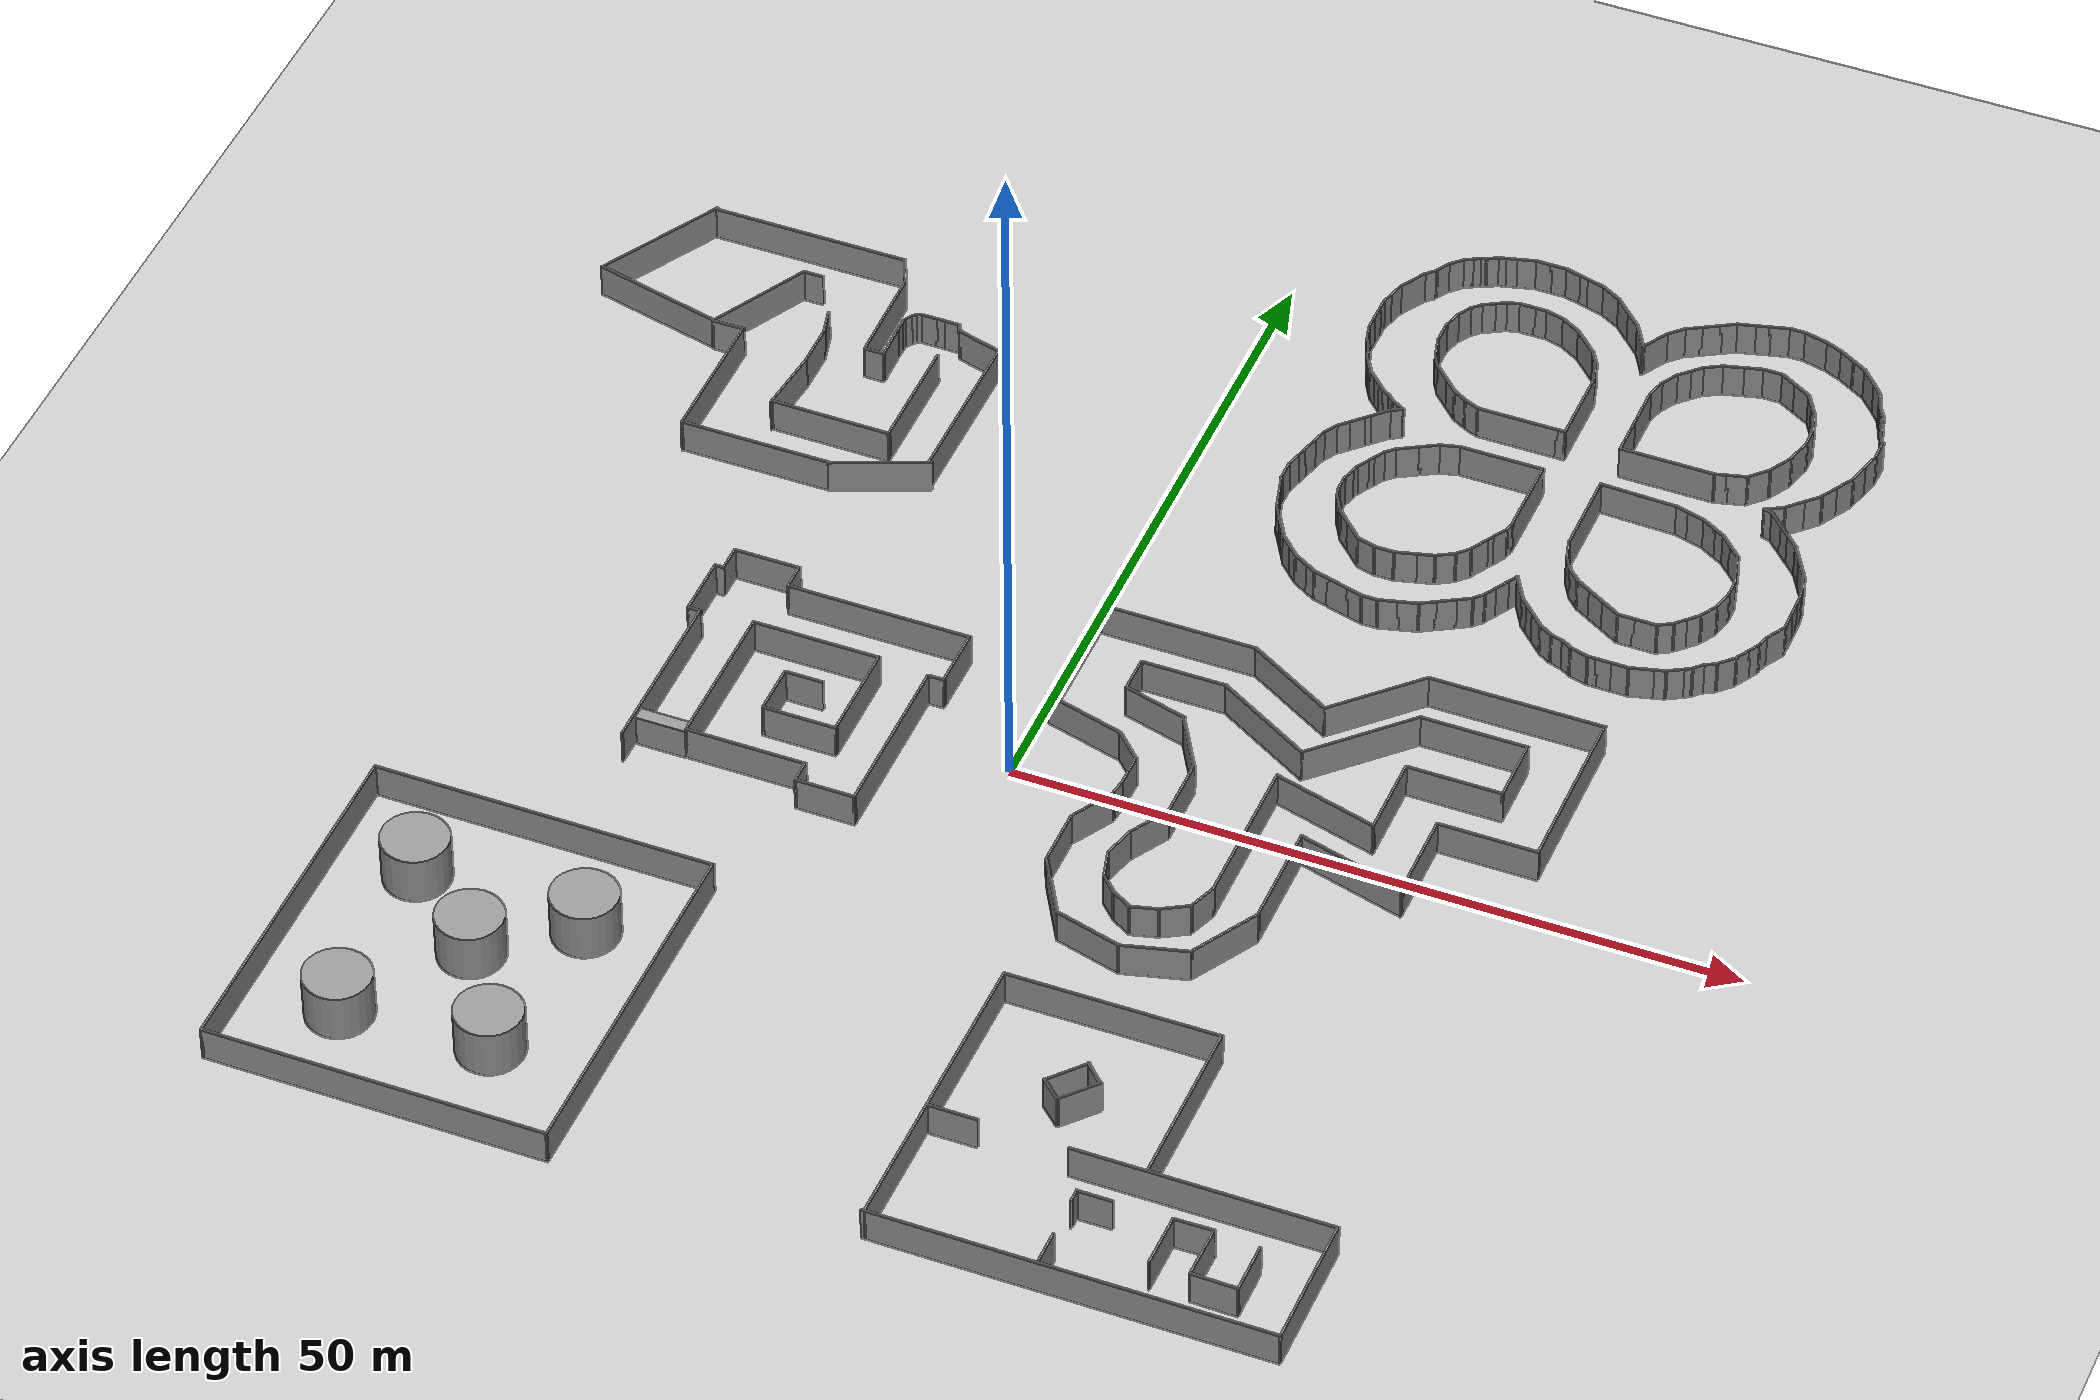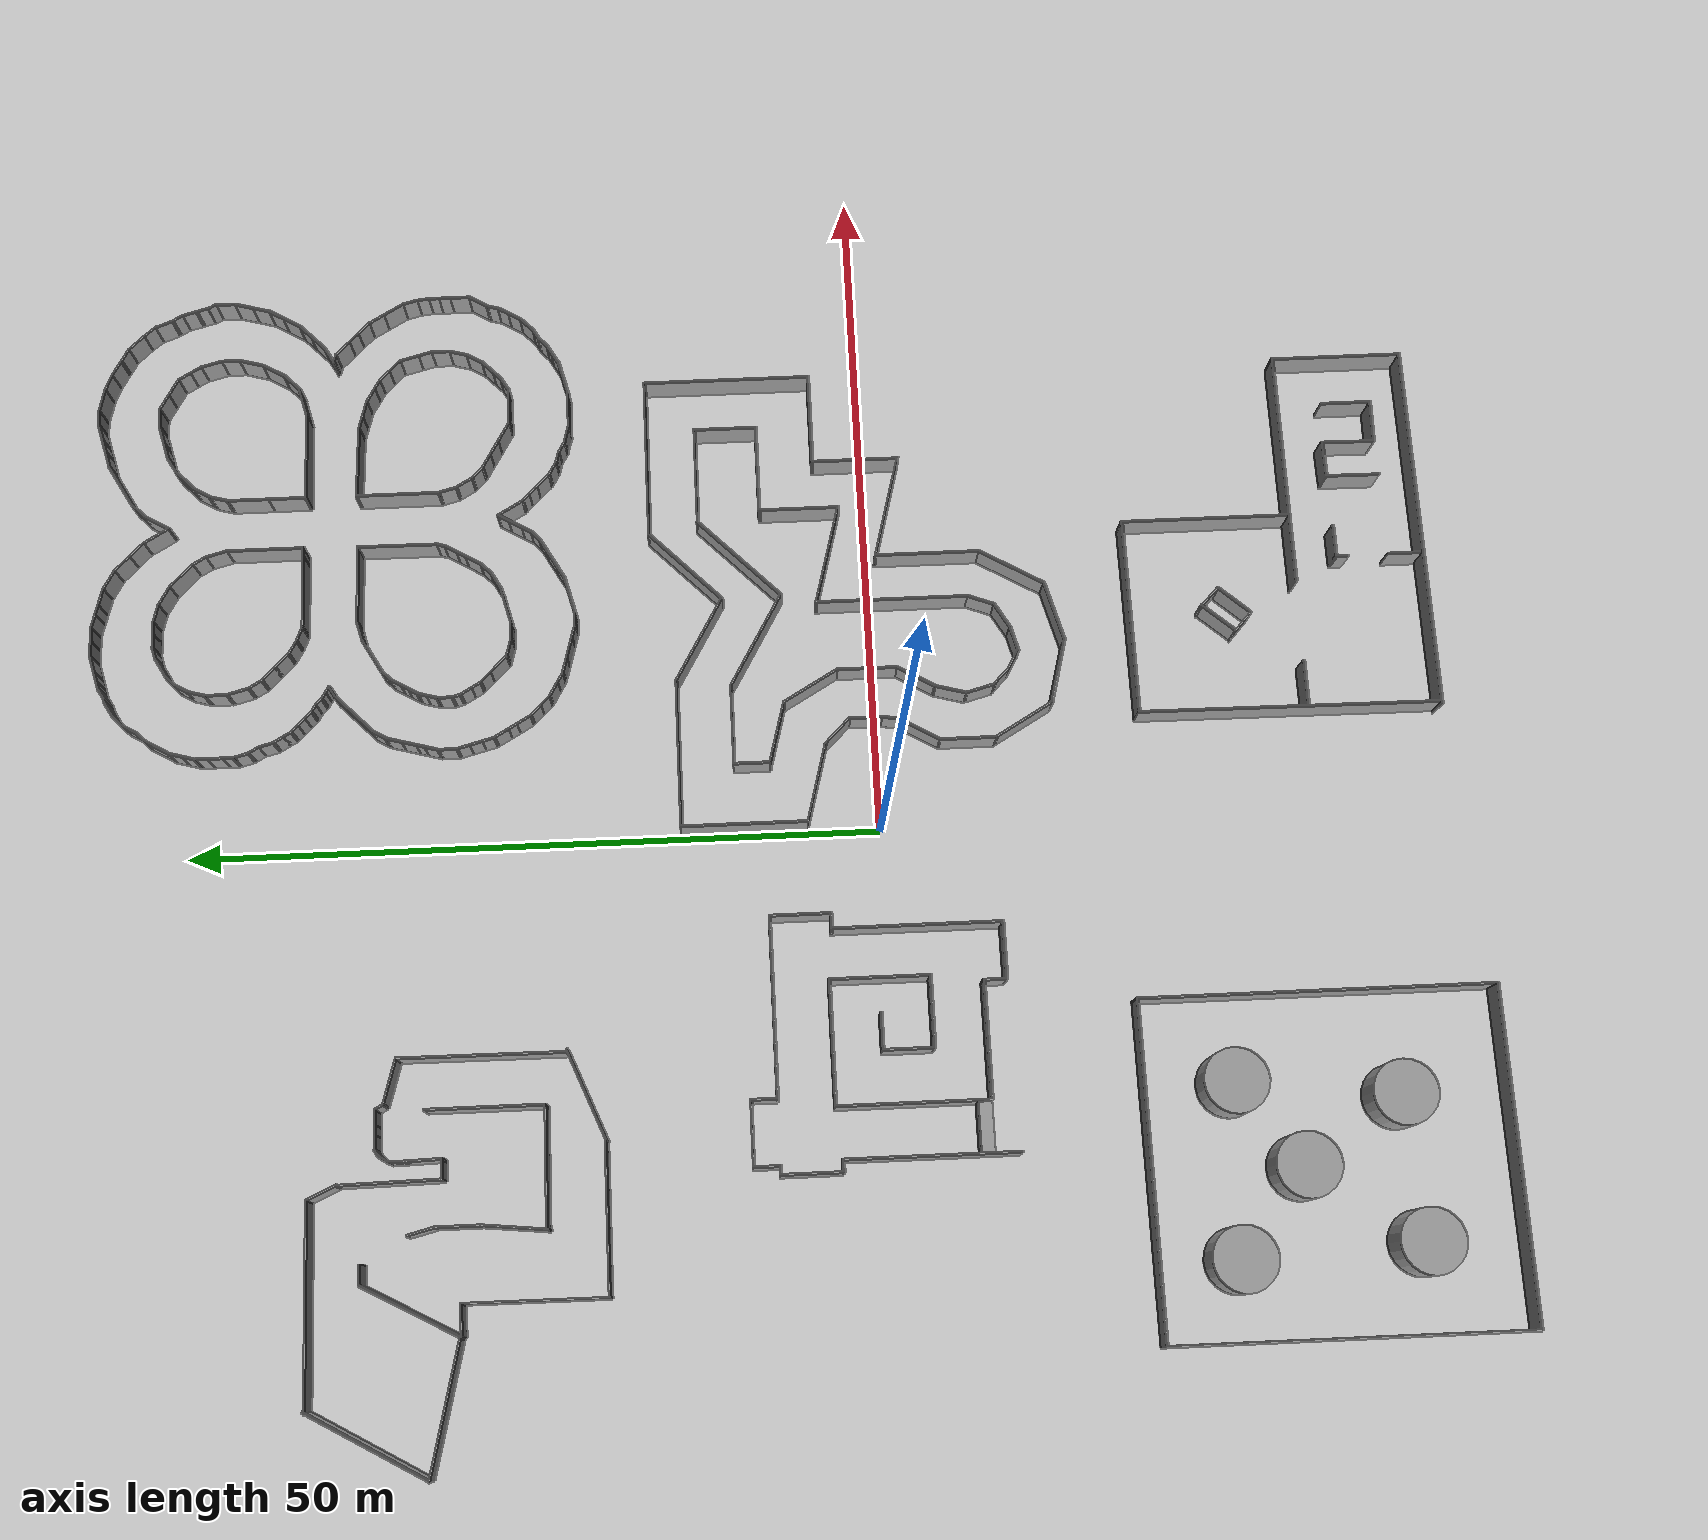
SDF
<sdf version="1.7">
 <world name="default">
  <light name="sun" type="directional">
   <pose>0 0 10 0 -0 0</pose>
   <diffuse>0.8 0.8 0.8 1</diffuse>
   <specular>0.2 0.2 0.2 1</specular>
   <attenuation>
    <range>1000</range>
    <constant>0.9</constant>
    <linear>0.01</linear>
    <quadratic>0.001</quadratic>
   </attenuation>
   <direction>-0.5 0.1 -0.9</direction>
   <spot><inner_angle>0</inner_angle><outer_angle>0</outer_angle><falloff>0</falloff></spot>
  </light>
  <model name="ground_plane">
   <static>1</static>
   <link name="link">
    <collision name="collision">
     <geometry><plane><normal>0 0 1</normal><size>100 100</size></plane></geometry>
     <surface><friction><ode><mu>100</mu><mu2>50</mu2></ode></friction></surface>
    </collision>
    <visual name="visual">
     <cast_shadows>0</cast_shadows>
     <geometry><plane><normal>0 0 1</normal><size>100 100</size></plane></geometry>
     <material>
      <script><uri>file://media/materials/scripts/gazebo.material</uri><name>Gazebo/Grey</name></script>
     </material>
    </visual>
   </link>
  </model>
  <gravity>0 0 -9.8</gravity>
  <magnetic_field>6e-06 2.3e-05 -4.2e-05</magnetic_field>
  <atmosphere type="adiabatic"/>
  <physics type="ode">
   <max_step_size>0.001</max_step_size>
   <real_time_factor>1</real_time_factor>
   <real_time_update_rate>1000</real_time_update_rate>
  </physics>
  <scene><ambient>0.4 0.4 0.4 1</ambient><background>0.7 0.7 0.7 1</background><shadows>1</shadows></scene>
  <audio><device>default</device></audio>
  <spherical_coordinates>
   <surface_model>EARTH_WGS84</surface_model>
   <latitude_deg>0</latitude_deg>
   <longitude_deg>0</longitude_deg>
   <elevation>0</elevation>
   <heading_deg>0</heading_deg>
  </spherical_coordinates>
  <model name="map1-Scale2.5">
   <pose>-15.2546 0.847586 0 0 -0 0</pose>
   <link name="Wall_100">
    <collision name="Wall_100_Collision">
     <geometry><box><size>7.25 0.15 2.5</size></box></geometry>
     <pose>0 0 1.25 0 -0 0</pose>
    </collision>
    <visual name="Wall_100_Visual">
     <pose>0 0 1.25 0 -0 0</pose>
     <geometry><box><size>7.25 0.15 2.5</size></box></geometry>
     <material>
      <script><uri>file://media/materials/scripts/gazebo.material</uri><name>Gazebo/Grey</name></script>
      <ambient>1 1 1 1</ambient>
     </material>
     <meta><layer>0</layer></meta>
    </visual>
    <pose>4.325 -0.125 0 0 -0 -1.5708</pose>
   </link>
   <link name="Wall_101">
    <collision name="Wall_101_Collision">
     <geometry><box><size>5.25 0.15 2.5</size></box></geometry>
     <pose>0 0 1.25 0 -0 0</pose>
    </collision>
    <visual name="Wall_101_Visual">
     <pose>0 0 1.25 0 -0 0</pose>
     <geometry><box><size>5.25 0.15 2.5</size></box></geometry>
     <material>
      <script><uri>file://media/materials/scripts/gazebo.material</uri><name>Gazebo/Grey</name></script>
      <ambient>1 1 1 1</ambient>
     </material>
     <meta><layer>0</layer></meta>
    </visual>
    <pose>1.775 -3.675 0 0 -0 3.14159</pose>
   </link>
   <link name="Wall_102">
    <collision name="Wall_102_Collision">
     <geometry><box><size>3.75 0.15 2.5</size></box></geometry>
     <pose>0 0 1.25 0 -0 0</pose>
    </collision>
    <visual name="Wall_102_Visual">
     <pose>0 0 1.25 0 -0 0</pose>
     <geometry><box><size>3.75 0.15 2.5</size></box></geometry>
     <material>
      <script><uri>file://media/materials/scripts/gazebo.material</uri><name>Gazebo/Grey</name></script>
      <ambient>1 1 1 1</ambient>
     </material>
     <meta><layer>0</layer></meta>
    </visual>
    <pose>-0.775 -1.875 0 0 -0 1.5708</pose>
   </link>
   <link name="Wall_103">
    <collision name="Wall_103_Collision">
     <geometry><box><size>2.75 0.15 2.5</size></box></geometry>
     <pose>0 0 1.25 0 -0 0</pose>
    </collision>
    <visual name="Wall_103_Visual">
     <pose>0 0 1.25 0 -0 0</pose>
     <geometry><box><size>2.75 0.15 2.5</size></box></geometry>
     <material>
      <script><uri>file://media/materials/scripts/gazebo.material</uri><name>Gazebo/Grey</name></script>
      <ambient>1 1 1 1</ambient>
     </material>
     <meta><layer>0</layer></meta>
    </visual>
    <pose>0.525 -0.075 0 0 -0 0</pose>
   </link>
   <link name="Wall_84">
    <collision name="Wall_84_Collision">
     <geometry><box><size>12.5 0.15 2.5</size></box></geometry>
     <pose>0 0 1.25 0 -0 0</pose>
    </collision>
    <visual name="Wall_84_Visual">
     <pose>0 0 1.25 0 -0 0</pose>
     <geometry><box><size>12.5 0.15 2.5</size></box></geometry>
     <material>
      <script><uri>file://media/materials/scripts/gazebo.material</uri><name>Gazebo/Grey</name></script>
      <ambient>1 1 1 1</ambient>
     </material>
     <meta><layer>0</layer></meta>
    </visual>
    <pose>-8.175 -3.1 0 0 -0 1.5708</pose>
   </link>
   <link name="Wall_85">
    <collision name="Wall_85_Collision">
     <geometry><box><size>1 0.15 2.5</size></box></geometry>
     <pose>0 0 1.25 0 -0 0</pose>
    </collision>
    <visual name="Wall_85_Visual">
     <pose>0 0 1.25 0 -0 0</pose>
     <geometry><box><size>1 0.15 2.5</size></box></geometry>
     <material>
      <script><uri>file://media/materials/scripts/gazebo.material</uri><name>Gazebo/Grey</name></script>
      <ambient>1 1 1 1</ambient>
     </material>
     <meta><layer>0</layer></meta>
    </visual>
    <pose>-8.6 3.075 0 0 -0 3.14159</pose>
   </link>
   <link name="Wall_86">
    <collision name="Wall_86_Collision">
     <geometry><box><size>4.5 0.15 2.5</size></box></geometry>
     <pose>0 0 1.25 0 -0 0</pose>
    </collision>
    <visual name="Wall_86_Visual">
     <pose>0 0 1.25 0 -0 0</pose>
     <geometry><box><size>4.5 0.15 2.5</size></box></geometry>
     <material>
      <script><uri>file://media/materials/scripts/gazebo.material</uri><name>Gazebo/Grey</name></script>
      <ambient>1 1 1 1</ambient>
     </material>
     <meta><layer>0</layer></meta>
    </visual>
    <pose>-9.025 5.25 0 0 -0 1.5708</pose>
   </link>
   <link name="Wall_87">
    <collision name="Wall_87_Collision">
     <geometry><box><size>0.75 0.15 2.5</size></box></geometry>
     <pose>0 0 1.25 0 -0 0</pose>
    </collision>
    <visual name="Wall_87_Visual">
     <pose>0 0 1.25 0 -0 0</pose>
     <geometry><box><size>0.75 0.15 2.5</size></box></geometry>
     <material>
      <script><uri>file://media/materials/scripts/gazebo.material</uri><name>Gazebo/Grey</name></script>
      <ambient>1 1 1 1</ambient>
     </material>
     <meta><layer>0</layer></meta>
    </visual>
    <pose>-8.725 7.425 0 0 -0 0</pose>
   </link>
   <link name="Wall_88">
    <collision name="Wall_88_Collision">
     <geometry><box><size>2 0.15 2.5</size></box></geometry>
     <pose>0 0 1.25 0 -0 0</pose>
    </collision>
    <visual name="Wall_88_Visual">
     <pose>0 0 1.25 0 -0 0</pose>
     <geometry><box><size>2 0.15 2.5</size></box></geometry>
     <material>
      <script><uri>file://media/materials/scripts/gazebo.material</uri><name>Gazebo/Grey</name></script>
      <ambient>1 1 1 1</ambient>
     </material>
     <meta><layer>0</layer></meta>
    </visual>
    <pose>-8.425 8.35 0 0 -0 1.5708</pose>
   </link>
   <link name="Wall_89">
    <collision name="Wall_89_Collision">
     <geometry><box><size>4.75 0.15 2.5</size></box></geometry>
     <pose>0 0 1.25 0 -0 0</pose>
    </collision>
    <visual name="Wall_89_Visual">
     <pose>0 0 1.25 0 -0 0</pose>
     <geometry><box><size>4.75 0.15 2.5</size></box></geometry>
     <material>
      <script><uri>file://media/materials/scripts/gazebo.material</uri><name>Gazebo/Grey</name></script>
      <ambient>1 1 1 1</ambient>
     </material>
     <meta><layer>0</layer></meta>
    </visual>
    <pose>-6.125 9.275 0 0 -0 0</pose>
   </link>
   <link name="Wall_90">
    <collision name="Wall_90_Collision">
     <geometry><box><size>2 0.15 2.5</size></box></geometry>
     <pose>0 0 1.25 0 -0 0</pose>
    </collision>
    <visual name="Wall_90_Visual">
     <pose>0 0 1.25 0 -0 0</pose>
     <geometry><box><size>2 0.15 2.5</size></box></geometry>
     <material>
      <script><uri>file://media/materials/scripts/gazebo.material</uri><name>Gazebo/Grey</name></script>
      <ambient>1 1 1 1</ambient>
     </material>
     <meta><layer>0</layer></meta>
    </visual>
    <pose>-3.825 8.35 0 0 -0 -1.5708</pose>
   </link>
   <link name="Wall_91">
    <collision name="Wall_91_Collision">
     <geometry><box><size>13 0.15 2.5</size></box></geometry>
     <pose>0 0 1.25 0 -0 0</pose>
    </collision>
    <visual name="Wall_91_Visual">
     <pose>0 0 1.25 0 -0 0</pose>
     <geometry><box><size>13 0.15 2.5</size></box></geometry>
     <material>
      <script><uri>file://media/materials/scripts/gazebo.material</uri><name>Gazebo/Grey</name></script>
      <ambient>1 1 1 1</ambient>
     </material>
     <meta><layer>0</layer></meta>
    </visual>
    <pose>2.6 7.425 0 0 -0 0</pose>
   </link>
   <link name="Wall_92">
    <collision name="Wall_92_Collision">
     <geometry><box><size>4.5 0.15 2.5</size></box></geometry>
     <pose>0 0 1.25 0 -0 0</pose>
    </collision>
    <visual name="Wall_92_Visual">
     <pose>0 0 1.25 0 -0 0</pose>
     <geometry><box><size>4.5 0.15 2.5</size></box></geometry>
     <material>
      <script><uri>file://media/materials/scripts/gazebo.material</uri><name>Gazebo/Grey</name></script>
      <ambient>1 1 1 1</ambient>
     </material>
     <meta><layer>0</layer></meta>
    </visual>
    <pose>9.025 5.25 0 0 -0 -1.5708</pose>
   </link>
   <link name="Wall_93">
    <collision name="Wall_93_Collision">
     <geometry><box><size>1.25 0.15 2.5</size></box></geometry>
     <pose>0 0 1.25 0 -0 0</pose>
    </collision>
    <visual name="Wall_93_Visual">
     <pose>0 0 1.25 0 -0 0</pose>
     <geometry><box><size>1.25 0.15 2.5</size></box></geometry>
     <material>
      <script><uri>file://media/materials/scripts/gazebo.material</uri><name>Gazebo/Grey</name></script>
      <ambient>1 1 1 1</ambient>
     </material>
     <meta><layer>0</layer></meta>
    </visual>
    <pose>8.475 3.075 0 0 -0 3.14159</pose>
   </link>
   <link name="Wall_94">
    <collision name="Wall_94_Collision">
     <geometry><box><size>12.25 0.15 2.5</size></box></geometry>
     <pose>0 0 1.25 0 -0 0</pose>
    </collision>
    <visual name="Wall_94_Visual">
     <pose>0 0 1.25 0 -0 0</pose>
     <geometry><box><size>12.25 0.15 2.5</size></box></geometry>
     <material>
      <script><uri>file://media/materials/scripts/gazebo.material</uri><name>Gazebo/Grey</name></script>
      <ambient>1 1 1 1</ambient>
     </material>
     <meta><layer>0</layer></meta>
    </visual>
    <pose>7.925 -2.975 0 0 -0 -1.5708</pose>
   </link>
   <link name="Wall_95">
    <collision name="Wall_95_Collision">
     <geometry><box><size>4.25 0.15 2.5</size></box></geometry>
     <pose>0 0 1.25 0 -0 0</pose>
    </collision>
    <visual name="Wall_95_Visual">
     <pose>0 0 1.25 0 -0 0</pose>
     <geometry><box><size>4.25 0.15 2.5</size></box></geometry>
     <material>
      <script><uri>file://media/materials/scripts/gazebo.material</uri><name>Gazebo/Grey</name></script>
      <ambient>1 1 1 1</ambient>
     </material>
     <meta><layer>0</layer></meta>
    </visual>
    <pose>5.875 -9.025 0 0 -0 3.14159</pose>
   </link>
   <link name="Wall_96">
    <collision name="Wall_96_Collision">
     <geometry><box><size>1.75 0.15 2.5</size></box></geometry>
     <pose>0 0 1.25 0 -0 0</pose>
    </collision>
    <visual name="Wall_96_Visual">
     <pose>0 0 1.25 0 -0 0</pose>
     <geometry><box><size>1.75 0.15 2.5</size></box></geometry>
     <material>
      <script><uri>file://media/materials/scripts/gazebo.material</uri><name>Gazebo/Grey</name></script>
      <ambient>1 1 1 1</ambient>
     </material>
     <meta><layer>0</layer></meta>
    </visual>
    <pose>3.825 -8.225 0 0 -0 1.5708</pose>
   </link>
   <link name="Wall_97">
    <collision name="Wall_97_Collision">
     <geometry><box><size>8.5 0.15 2.5</size></box></geometry>
     <pose>0 0 1.25 0 -0 0</pose>
    </collision>
    <visual name="Wall_97_Visual">
     <pose>0 0 1.25 0 -0 0</pose>
     <geometry><box><size>8.5 0.15 2.5</size></box></geometry>
     <material>
      <script><uri>file://media/materials/scripts/gazebo.material</uri><name>Gazebo/Grey</name></script>
      <ambient>1 1 1 1</ambient>
     </material>
     <meta><layer>0</layer></meta>
    </visual>
    <pose>-0.35 -7.425 0 0 -0 3.14159</pose>
   </link>
   <link name="Wall_98">
    <collision name="Wall_98_Collision">
     <geometry><box><size>11 0.15 2.5</size></box></geometry>
     <pose>0 0 1.25 0 -0 0</pose>
    </collision>
    <visual name="Wall_98_Visual">
     <pose>0 0 1.25 0 -0 0</pose>
     <geometry><box><size>11 0.15 2.5</size></box></geometry>
     <material>
      <script><uri>file://media/materials/scripts/gazebo.material</uri><name>Gazebo/Grey</name></script>
      <ambient>1 1 1 1</ambient>
     </material>
     <meta><layer>0</layer></meta>
    </visual>
    <pose>-4.525 -2 0 0 -0 1.5708</pose>
   </link>
   <link name="Wall_99">
    <collision name="Wall_99_Collision">
     <geometry><box><size>9 0.15 2.5</size></box></geometry>
     <pose>0 0 1.25 0 -0 0</pose>
    </collision>
    <visual name="Wall_99_Visual">
     <pose>0 0 1.25 0 -0 0</pose>
     <geometry><box><size>9 0.15 2.5</size></box></geometry>
     <material>
      <script><uri>file://media/materials/scripts/gazebo.material</uri><name>Gazebo/Grey</name></script>
      <ambient>1 1 1 1</ambient>
     </material>
     <meta><layer>0</layer></meta>
    </visual>
    <pose>-0.1 3.425 0 0 -0 0</pose>
   </link>
   <static>1</static>
  </model>
  <model name="map2-Scaled2.5">
   <pose>17.6419 0.92612 0 0 -0 0</pose>
   <link name="Wall_39">
    <collision name="Wall_39_Collision">
     <geometry><box><size>6 0.15 2.5</size></box></geometry>
     <pose>0 0 1.25 0 -0 0</pose>
    </collision>
    <visual name="Wall_39_Visual">
     <pose>0 0 1.25 0 -0 0</pose>
     <geometry><box><size>6 0.15 2.5</size></box></geometry>
     <material>
      <script><uri>file://media/materials/scripts/gazebo.material</uri><name>Gazebo/Grey</name></script>
      <ambient>1 1 1 1</ambient>
     </material>
     <meta><layer>0</layer></meta>
    </visual>
    <pose>-14.3142 3.53465 0 0 -0 2.87979</pose>
   </link>
   <link name="Wall_40">
    <collision name="Wall_40_Collision">
     <geometry><box><size>9.25 0.15 2.5</size></box></geometry>
     <pose>0 0 1.25 0 -0 0</pose>
    </collision>
    <visual name="Wall_40_Visual">
     <pose>0 0 1.25 0 -0 0</pose>
     <geometry><box><size>9.25 0.15 2.5</size></box></geometry>
     <material>
      <script><uri>file://media/materials/scripts/gazebo.material</uri><name>Gazebo/Grey</name></script>
      <ambient>1 1 1 1</ambient>
     </material>
     <meta><layer>0</layer></meta>
    </visual>
    <pose>-17.1396 8.8417 0 0 -0 1.5708</pose>
   </link>
   <link name="Wall_41">
    <collision name="Wall_41_Collision">
     <geometry><box><size>11 0.15 2.5</size></box></geometry>
     <pose>0 0 1.25 0 -0 0</pose>
    </collision>
    <visual name="Wall_41_Visual">
     <pose>0 0 1.25 0 -0 0</pose>
     <geometry><box><size>11 0.15 2.5</size></box></geometry>
     <material>
      <script><uri>file://media/materials/scripts/gazebo.material</uri><name>Gazebo/Grey</name></script>
      <ambient>1 1 1 1</ambient>
     </material>
     <meta><layer>0</layer></meta>
    </visual>
    <pose>-11.7146 13.3917 0 0 -0 0</pose>
   </link>
   <link name="Wall_42">
    <collision name="Wall_42_Collision">
     <geometry><box><size>7.25 0.15 2.5</size></box></geometry>
     <pose>0 0 1.25 0 -0 0</pose>
    </collision>
    <visual name="Wall_42_Visual">
     <pose>0 0 1.25 0 -0 0</pose>
     <geometry><box><size>7.25 0.15 2.5</size></box></geometry>
     <material>
      <script><uri>file://media/materials/scripts/gazebo.material</uri><name>Gazebo/Grey</name></script>
      <ambient>1 1 1 1</ambient>
     </material>
     <meta><layer>0</layer></meta>
    </visual>
    <pose>-3.21519 11.6167 0 0 -0 -0.523599</pose>
   </link>
   <link name="Wall_43">
    <collision name="Wall_43_Collision">
     <geometry><box><size>7.5 0.15 2.5</size></box></geometry>
     <pose>0 0 1.25 0 -0 0</pose>
    </collision>
    <visual name="Wall_43_Visual">
     <pose>0 0 1.25 0 -0 0</pose>
     <geometry><box><size>7.5 0.15 2.5</size></box></geometry>
     <material>
      <script><uri>file://media/materials/scripts/gazebo.material</uri><name>Gazebo/Grey</name></script>
      <ambient>1 1 1 1</ambient>
     </material>
     <meta><layer>0</layer></meta>
    </visual>
    <pose>2.45782 12.4403 0 0 -0 0.785398</pose>
   </link>
   <link name="Wall_44">
    <collision name="Wall_44_Collision">
     <geometry><box><size>12.25 0.15 2.5</size></box></geometry>
     <pose>0 0 1.25 0 -0 0</pose>
    </collision>
    <visual name="Wall_44_Visual">
     <pose>0 0 1.25 0 -0 0</pose>
     <geometry><box><size>12.25 0.15 2.5</size></box></geometry>
     <material>
      <script><uri>file://media/materials/scripts/gazebo.material</uri><name>Gazebo/Grey</name></script>
      <ambient>1 1 1 1</ambient>
     </material>
     <meta><layer>0</layer></meta>
    </visual>
    <pose>11.1064 15.0389 0 0 -0 0</pose>
   </link>
   <link name="Wall_45">
    <collision name="Wall_45_Collision">
     <geometry><box><size>12.5 0.15 2.5</size></box></geometry>
     <pose>0 0 1.25 0 -0 0</pose>
    </collision>
    <visual name="Wall_45_Visual">
     <pose>0 0 1.25 0 -0 0</pose>
     <geometry><box><size>12.5 0.15 2.5</size></box></geometry>
     <material>
      <script><uri>file://media/materials/scripts/gazebo.material</uri><name>Gazebo/Grey</name></script>
      <ambient>1 1 1 1</ambient>
     </material>
     <meta><layer>0</layer></meta>
    </visual>
    <pose>17.1564 8.86393 0 0 -0 -1.5708</pose>
   </link>
   <link name="Wall_46">
    <collision name="Wall_46_Collision">
     <geometry><box><size>7 0.15 2.5</size></box></geometry>
     <pose>0 0 1.25 0 -0 0</pose>
    </collision>
    <visual name="Wall_46_Visual">
     <pose>0 0 1.25 0 -0 0</pose>
     <geometry><box><size>7 0.15 2.5</size></box></geometry>
     <material>
      <script><uri>file://media/materials/scripts/gazebo.material</uri><name>Gazebo/Grey</name></script>
      <ambient>1 1 1 1</ambient>
     </material>
     <meta><layer>0</layer></meta>
    </visual>
    <pose>13.7314 2.68893 0 0 -0 3.14159</pose>
   </link>
   <link name="Wall_47">
    <collision name="Wall_47_Collision">
     <geometry><box><size>6.5 0.15 2.5</size></box></geometry>
     <pose>0 0 1.25 0 -0 0</pose>
    </collision>
    <visual name="Wall_47_Visual">
     <pose>0 0 1.25 0 -0 0</pose>
     <geometry><box><size>6.5 0.15 2.5</size></box></geometry>
     <material>
      <script><uri>file://media/materials/scripts/gazebo.material</uri><name>Gazebo/Grey</name></script>
      <ambient>1 1 1 1</ambient>
     </material>
     <meta><layer>0</layer></meta>
    </visual>
    <pose>10.3064 -0.486068 0 0 -0 -1.5708</pose>
   </link>
   <link name="Wall_48">
    <collision name="Wall_48_Collision">
     <geometry><box><size>8 0.15 2.5</size></box></geometry>
     <pose>0 0 1.25 0 -0 0</pose>
    </collision>
    <visual name="Wall_48_Visual">
     <pose>0 0 1.25 0 -0 0</pose>
     <geometry><box><size>8 0.15 2.5</size></box></geometry>
     <material>
      <script><uri>file://media/materials/scripts/gazebo.material</uri><name>Gazebo/Grey</name></script>
      <ambient>1 1 1 1</ambient>
     </material>
     <meta><layer>0</layer></meta>
    </visual>
    <pose>6.51518 -2.6452 0 0 -0 2.87979</pose>
   </link>
   <link name="Wall_49">
    <collision name="Wall_49_Collision">
     <geometry><box><size>7.75 0.15 2.5</size></box></geometry>
     <pose>0 0 1.25 0 -0 0</pose>
    </collision>
    <visual name="Wall_49_Visual">
     <pose>0 0 1.25 0 -0 0</pose>
     <geometry><box><size>7.75 0.15 2.5</size></box></geometry>
     <material>
      <script><uri>file://media/materials/scripts/gazebo.material</uri><name>Gazebo/Grey</name></script>
      <ambient>1 1 1 1</ambient>
     </material>
     <meta><layer>0</layer></meta>
    </visual>
    <pose>2.72392 -5.42934 0 0 -0 -1.5708</pose>
   </link>
   <link name="Wall_50">
    <collision name="Wall_50_Collision">
     <geometry><box><size>5.5 0.15 2.5</size></box></geometry>
     <pose>0 0 1.25 0 -0 0</pose>
    </collision>
    <visual name="Wall_50_Visual">
     <pose>0 0 1.25 0 -0 0</pose>
     <geometry><box><size>5.5 0.15 2.5</size></box></geometry>
     <material>
      <script><uri>file://media/materials/scripts/gazebo.material</uri><name>Gazebo/Grey</name></script>
      <ambient>1 1 1 1</ambient>
     </material>
     <meta><layer>0</layer></meta>
    </visual>
    <pose>1.38642 -11.546 0 0 -0 -2.0944</pose>
   </link>
   <link name="Wall_51">
    <collision name="Wall_51_Collision">
     <geometry><box><size>4.75 0.15 2.5</size></box></geometry>
     <pose>0 0 1.25 0 -0 0</pose>
    </collision>
    <visual name="Wall_51_Visual">
     <pose>0 0 1.25 0 -0 0</pose>
     <geometry><box><size>4.75 0.15 2.5</size></box></geometry>
     <material>
      <script><uri>file://media/materials/scripts/gazebo.material</uri><name>Gazebo/Grey</name></script>
      <ambient>1 1 1 1</ambient>
     </material>
     <meta><layer>0</layer></meta>
    </visual>
    <pose>-2.17271 -14.4579 0 0 -0 -2.87979</pose>
   </link>
   <link name="Wall_52">
    <collision name="Wall_52_Collision">
     <geometry><box><size>5 0.15 2.5</size></box></geometry>
     <pose>0 0 1.25 0 -0 0</pose>
    </collision>
    <visual name="Wall_52_Visual">
     <pose>0 0 1.25 0 -0 0</pose>
     <geometry><box><size>5 0.15 2.5</size></box></geometry>
     <material>
      <script><uri>file://media/materials/scripts/gazebo.material</uri><name>Gazebo/Grey</name></script>
      <ambient>1 1 1 1</ambient>
     </material>
     <meta><layer>0</layer></meta>
    </visual>
    <pose>-6.73671 -14.4255 0 0 -0 2.87979</pose>
   </link>
   <link name="Wall_53">
    <collision name="Wall_53_Collision">
     <geometry><box><size>5 0.15 2.5</size></box></geometry>
     <pose>0 0 1.25 0 -0 0</pose>
    </collision>
    <visual name="Wall_53_Visual">
     <pose>0 0 1.25 0 -0 0</pose>
     <geometry><box><size>5 0.15 2.5</size></box></geometry>
     <material>
      <script><uri>file://media/materials/scripts/gazebo.material</uri><name>Gazebo/Grey</name></script>
      <ambient>1 1 1 1</ambient>
     </material>
     <meta><layer>0</layer></meta>
    </visual>
    <pose>-10.2916 -11.6978 0 0 -0 2.0944</pose>
   </link>
   <link name="Wall_54">
    <collision name="Wall_54_Collision">
     <geometry><box><size>4.25 0.15 2.5</size></box></geometry>
     <pose>0 0 1.25 0 -0 0</pose>
    </collision>
    <visual name="Wall_54_Visual">
     <pose>0 0 1.25 0 -0 0</pose>
     <geometry><box><size>4.25 0.15 2.5</size></box></geometry>
     <material>
      <script><uri>file://media/materials/scripts/gazebo.material</uri><name>Gazebo/Grey</name></script>
      <ambient>1 1 1 1</ambient>
     </material>
     <meta><layer>0</layer></meta>
    </visual>
    <pose>-11.5041 -7.54765 0 0 -0 1.5708</pose>
   </link>
   <link name="Wall_55">
    <collision name="Wall_55_Collision">
     <geometry><box><size>3.5 0.15 2.5</size></box></geometry>
     <pose>0 0 1.25 0 -0 0</pose>
    </collision>
    <visual name="Wall_55_Visual">
     <pose>0 0 1.25 0 -0 0</pose>
     <geometry><box><size>3.5 0.15 2.5</size></box></geometry>
     <material>
      <script><uri>file://media/materials/scripts/gazebo.material</uri><name>Gazebo/Grey</name></script>
      <ambient>1 1 1 1</ambient>
     </material>
     <meta><layer>0</layer></meta>
    </visual>
    <pose>-10.6666 -4.04705 0 0 -0 1.0472</pose>
   </link>
   <link name="Wall_57">
    <collision name="Wall_57_Collision">
     <geometry><box><size>3.25 0.15 2.5</size></box></geometry>
     <pose>0 0 1.25 0 -0 0</pose>
    </collision>
    <visual name="Wall_57_Visual">
     <pose>0 0 1.25 0 -0 0</pose>
     <geometry><box><size>3.25 0.15 2.5</size></box></geometry>
     <material>
      <script><uri>file://media/materials/scripts/gazebo.material</uri><name>Gazebo/Grey</name></script>
      <ambient>1 1 1 1</ambient>
     </material>
     <meta><layer>0</layer></meta>
    </visual>
    <pose>-6.71391 -4.04005 0 0 -0 1.0472</pose>
   </link>
   <link name="Wall_58">
    <collision name="Wall_58_Collision">
     <geometry><box><size>4.5 0.15 2.5</size></box></geometry>
     <pose>0 0 1.25 0 -0 0</pose>
    </collision>
    <visual name="Wall_58_Visual">
     <pose>0 0 1.25 0 -0 0</pose>
     <geometry><box><size>4.5 0.15 2.5</size></box></geometry>
     <material>
      <script><uri>file://media/materials/scripts/gazebo.material</uri><name>Gazebo/Grey</name></script>
      <ambient>1 1 1 1</ambient>
     </material>
     <meta><layer>0</layer></meta>
    </visual>
    <pose>-5.93891 -0.522716 0 0 -0 1.5708</pose>
   </link>
   <link name="Wall_59">
    <collision name="Wall_59_Collision">
     <geometry><box><size>4.75 0.15 2.5</size></box></geometry>
     <pose>0 0 1.25 0 -0 0</pose>
    </collision>
    <visual name="Wall_59_Visual">
     <pose>0 0 1.25 0 -0 0</pose>
     <geometry><box><size>4.75 0.15 2.5</size></box></geometry>
     <material>
      <script><uri>file://media/materials/scripts/gazebo.material</uri><name>Gazebo/Grey</name></script>
      <ambient>1 1 1 1</ambient>
     </material>
     <meta><layer>0</layer></meta>
    </visual>
    <pose>-7.08891 3.64414 0 0 -0 2.0944</pose>
   </link>
   <link name="Wall_60">
    <collision name="Wall_60_Collision">
     <geometry><box><size>4.75 0.15 2.5</size></box></geometry>
     <pose>0 0 1.25 0 -0 0</pose>
    </collision>
    <visual name="Wall_60_Visual">
     <pose>0 0 1.25 0 -0 0</pose>
     <geometry><box><size>4.75 0.15 2.5</size></box></geometry>
     <material>
      <script><uri>file://media/materials/scripts/gazebo.material</uri><name>Gazebo/Grey</name></script>
      <ambient>1 1 1 1</ambient>
     </material>
     <meta><layer>0</layer></meta>
    </visual>
    <pose>-10.4605 6.23128 0 0 -0 2.87979</pose>
   </link>
   <link name="Wall_61">
    <collision name="Wall_61_Collision">
     <geometry><box><size>2.75 0.15 2.5</size></box></geometry>
     <pose>0 0 1.25 0 -0 0</pose>
    </collision>
    <visual name="Wall_61_Visual">
     <pose>0 0 1.25 0 -0 0</pose>
     <geometry><box><size>2.75 0.15 2.5</size></box></geometry>
     <material>
      <script><uri>file://media/materials/scripts/gazebo.material</uri><name>Gazebo/Grey</name></script>
      <ambient>1 1 1 1</ambient>
     </material>
     <meta><layer>0</layer></meta>
    </visual>
    <pose>-12.6822 8.12657 0 0 -0 1.5708</pose>
   </link>
   <link name="Wall_62">
    <collision name="Wall_62_Collision">
     <geometry><box><size>6 0.15 2.5</size></box></geometry>
     <pose>0 0 1.25 0 -0 0</pose>
    </collision>
    <visual name="Wall_62_Visual">
     <pose>0 0 1.25 0 -0 0</pose>
     <geometry><box><size>6 0.15 2.5</size></box></geometry>
     <material>
      <script><uri>file://media/materials/scripts/gazebo.material</uri><name>Gazebo/Grey</name></script>
      <ambient>1 1 1 1</ambient>
     </material>
     <meta><layer>0</layer></meta>
    </visual>
    <pose>-9.75717 9.42657 0 0 -0 0</pose>
   </link>
   <link name="Wall_63">
    <collision name="Wall_63_Collision">
     <geometry><box><size>8 0.15 2.5</size></box></geometry>
     <pose>0 0 1.25 0 -0 0</pose>
    </collision>
    <visual name="Wall_63_Visual">
     <pose>0 0 1.25 0 -0 0</pose>
     <geometry><box><size>8 0.15 2.5</size></box></geometry>
     <material>
      <script><uri>file://media/materials/scripts/gazebo.material</uri><name>Gazebo/Grey</name></script>
      <ambient>1 1 1 1</ambient>
     </material>
     <meta><layer>0</layer></meta>
    </visual>
    <pose>-3.43302 7.46407 0 0 -0 -0.523599</pose>
   </link>
   <link name="Wall_64">
    <collision name="Wall_64_Collision">
     <geometry><box><size>8.5 0.15 2.5</size></box></geometry>
     <pose>0 0 1.25 0 -0 0</pose>
    </collision>
    <visual name="Wall_64_Visual">
     <pose>0 0 1.25 0 -0 0</pose>
     <geometry><box><size>8.5 0.15 2.5</size></box></geometry>
     <material>
      <script><uri>file://media/materials/scripts/gazebo.material</uri><name>Gazebo/Grey</name></script>
      <ambient>1 1 1 1</ambient>
     </material>
     <meta><layer>0</layer></meta>
    </visual>
    <pose>2.9183 8.45374 0 0 -0 0.785398</pose>
   </link>
   <link name="Wall_65">
    <collision name="Wall_65_Collision">
     <geometry><box><size>7.5 0.15 2.5</size></box></geometry>
     <pose>0 0 1.25 0 -0 0</pose>
    </collision>
    <visual name="Wall_65_Visual">
     <pose>0 0 1.25 0 -0 0</pose>
     <geometry><box><size>7.5 0.15 2.5</size></box></geometry>
     <material>
      <script><uri>file://media/materials/scripts/gazebo.material</uri><name>Gazebo/Grey</name></script>
      <ambient>1 1 1 1</ambient>
     </material>
     <meta><layer>0</layer></meta>
    </visual>
    <pose>9.54547 11.4059 0 0 -0 0</pose>
   </link>
   <link name="Wall_66">
    <collision name="Wall_66_Collision">
     <geometry><box><size>4.75 0.15 2.5</size></box></geometry>
     <pose>0 0 1.25 0 -0 0</pose>
    </collision>
    <visual name="Wall_66_Visual">
     <pose>0 0 1.25 0 -0 0</pose>
     <geometry><box><size>4.75 0.15 2.5</size></box></geometry>
     <material>
      <script><uri>file://media/materials/scripts/gazebo.material</uri><name>Gazebo/Grey</name></script>
      <ambient>1 1 1 1</ambient>
     </material>
     <meta><layer>0</layer></meta>
    </visual>
    <pose>13.2205 9.10591 0 0 -0 -1.5708</pose>
   </link>
   <link name="Wall_67">
    <collision name="Wall_67_Collision">
     <geometry><box><size>6.75 0.15 2.5</size></box></geometry>
     <pose>0 0 1.25 0 -0 0</pose>
    </collision>
    <visual name="Wall_67_Visual">
     <pose>0 0 1.25 0 -0 0</pose>
     <geometry><box><size>6.75 0.15 2.5</size></box></geometry>
     <material>
      <script><uri>file://media/materials/scripts/gazebo.material</uri><name>Gazebo/Grey</name></script>
      <ambient>1 1 1 1</ambient>
     </material>
     <meta><layer>0</layer></meta>
    </visual>
    <pose>9.92047 6.80591 0 0 -0 3.14159</pose>
   </link>
   <link name="Wall_68">
    <collision name="Wall_68_Collision">
     <geometry><box><size>6 0.15 2.5</size></box></geometry>
     <pose>0 0 1.25 0 -0 0</pose>
    </collision>
    <visual name="Wall_68_Visual">
     <pose>0 0 1.25 0 -0 0</pose>
     <geometry><box><size>6 0.15 2.5</size></box></geometry>
     <material>
      <script><uri>file://media/materials/scripts/gazebo.material</uri><name>Gazebo/Grey</name></script>
      <ambient>1 1 1 1</ambient>
     </material>
     <meta><layer>0</layer></meta>
    </visual>
    <pose>6.62047 3.88091 0 0 -0 -1.5708</pose>
   </link>
   <link name="Wall_69">
    <collision name="Wall_69_Collision">
     <geometry><box><size>7.75 0.15 2.5</size></box></geometry>
     <pose>0 0 1.25 0 -0 0</pose>
    </collision>
    <visual name="Wall_69_Visual">
     <pose>0 0 1.25 0 -0 0</pose>
     <geometry><box><size>7.75 0.15 2.5</size></box></geometry>
     <material>
      <script><uri>file://media/materials/scripts/gazebo.material</uri><name>Gazebo/Grey</name></script>
      <ambient>1 1 1 1</ambient>
     </material>
     <meta><layer>0</layer></meta>
    </visual>
    <pose>2.94995 1.93942 0 0 -0 2.87979</pose>
   </link>
   <link name="Wall_70">
    <collision name="Wall_70_Collision">
     <geometry><box><size>11.25 0.15 2.5</size></box></geometry>
     <pose>0 0 1.25 0 -0 0</pose>
    </collision>
    <visual name="Wall_70_Visual">
     <pose>0 0 1.25 0 -0 0</pose>
     <geometry><box><size>11.25 0.15 2.5</size></box></geometry>
     <material>
      <script><uri>file://media/materials/scripts/gazebo.material</uri><name>Gazebo/Grey</name></script>
      <ambient>1 1 1 1</ambient>
     </material>
     <meta><layer>0</layer></meta>
    </visual>
    <pose>-0.720568 -2.62706 0 0 -0 -1.5708</pose>
   </link>
   <link name="Wall_72">
    <collision name="Wall_72_Collision">
     <geometry><box><size>2.75 0.15 2.5</size></box></geometry>
     <pose>0 0 1.25 0 -0 0</pose>
    </collision>
    <visual name="Wall_72_Visual">
     <pose>0 0 1.25 0 -0 0</pose>
     <geometry><box><size>2.75 0.15 2.5</size></box></geometry>
     <material>
      <script><uri>file://media/materials/scripts/gazebo.material</uri><name>Gazebo/Grey</name></script>
      <ambient>1 1 1 1</ambient>
     </material>
     <meta><layer>0</layer></meta>
    </visual>
    <pose>-10.5697 1.85837 0 0 -0 -0.785398</pose>
   </link>
   <link name="Wall_73">
    <collision name="Wall_73_Collision">
     <geometry><box><size>2.5 0.15 2.5</size></box></geometry>
     <pose>0 0 1.25 0 -0 0</pose>
    </collision>
    <visual name="Wall_73_Visual">
     <pose>0 0 1.25 0 -0 0</pose>
     <geometry><box><size>2.5 0.15 2.5</size></box></geometry>
     <material>
      <script><uri>file://media/materials/scripts/gazebo.material</uri><name>Gazebo/Grey</name></script>
      <ambient>1 1 1 1</ambient>
     </material>
     <meta><layer>0</layer></meta>
    </visual>
    <pose>-9.65044 -0.235872 0 0 -0 -1.5708</pose>
   </link>
   <link name="Wall_74">
    <collision name="Wall_74_Collision">
     <geometry><box><size>1.34897 0.15 2.5</size></box></geometry>
     <pose>0 0 1.25 0 -0 0</pose>
    </collision>
    <visual name="Wall_74_Visual">
     <pose>0 0 1.25 0 -0 0</pose>
     <geometry><box><size>1.34897 0.15 2.5</size></box></geometry>
     <material>
      <script><uri>file://media/materials/scripts/gazebo.material</uri><name>Gazebo/Grey</name></script>
      <ambient>1 1 1 1</ambient>
     </material>
     <meta><layer>0</layer></meta>
    </visual>
    <pose>-9.73976 -2.00367 0 0 -0 -1.72035</pose>
   </link>
   <link name="Wall_76">
    <collision name="Wall_76_Collision">
     <geometry><box><size>2.5 0.15 2.5</size></box></geometry>
     <pose>0 0 1.25 0 -0 0</pose>
    </collision>
    <visual name="Wall_76_Visual">
     <pose>0 0 1.25 0 -0 0</pose>
     <geometry><box><size>2.5 0.15 2.5</size></box></geometry>
     <material>
      <script><uri>file://media/materials/scripts/gazebo.material</uri><name>Gazebo/Grey</name></script>
      <ambient>1 1 1 1</ambient>
     </material>
     <meta><layer>0</layer></meta>
    </visual>
    <pose>-7.79303 -6.51736 0 0 -0 -1.8326</pose>
   </link>
   <link name="Wall_77">
    <collision name="Wall_77_Collision">
     <geometry><box><size>2.25 0.15 2.5</size></box></geometry>
     <pose>0 0 1.25 0 -0 0</pose>
    </collision>
    <visual name="Wall_77_Visual">
     <pose>0 0 1.25 0 -0 0</pose>
     <geometry><box><size>2.25 0.15 2.5</size></box></geometry>
     <material>
      <script><uri>file://media/materials/scripts/gazebo.material</uri><name>Gazebo/Grey</name></script>
      <ambient>1 1 1 1</ambient>
     </material>
     <meta><layer>0</layer></meta>
    </visual>
    <pose>-7.82538 -8.66654 0 0 -0 -1.309</pose>
   </link>
   <link name="Wall_78">
    <collision name="Wall_78_Collision">
     <geometry><box><size>1.75 0.15 2.5</size></box></geometry>
     <pose>0 0 1.25 0 -0 0</pose>
    </collision>
    <visual name="Wall_78_Visual">
     <pose>0 0 1.25 0 -0 0</pose>
     <geometry><box><size>1.75 0.15 2.5</size></box></geometry>
     <material>
      <script><uri>file://media/materials/scripts/gazebo.material</uri><name>Gazebo/Grey</name></script>
      <ambient>1 1 1 1</ambient>
     </material>
     <meta><layer>0</layer></meta>
    </visual>
    <pose>-6.98793 -10.2464 0 0 -0 -0.785398</pose>
   </link>
   <link name="Wall_79">
    <collision name="Wall_79_Collision">
     <geometry><box><size>1.75 0.15 2.5</size></box></geometry>
     <pose>0 0 1.25 0 -0 0</pose>
    </collision>
    <visual name="Wall_79_Visual">
     <pose>0 0 1.25 0 -0 0</pose>
     <geometry><box><size>1.75 0.15 2.5</size></box></geometry>
     <material>
      <script><uri>file://media/materials/scripts/gazebo.material</uri><name>Gazebo/Grey</name></script>
      <ambient>1 1 1 1</ambient>
     </material>
     <meta><layer>0</layer></meta>
    </visual>
    <pose>-5.72943 -11.2121 0 0 -0 -0.523599</pose>
   </link>
   <link name="Wall_80">
    <collision name="Wall_80_Collision">
     <geometry><box><size>2 0.15 2.5</size></box></geometry>
     <pose>0 0 1.25 0 -0 0</pose>
    </collision>
    <visual name="Wall_80_Visual">
     <pose>0 0 1.25 0 -0 0</pose>
     <geometry><box><size>2 0.15 2.5</size></box></geometry>
     <material>
      <script><uri>file://media/materials/scripts/gazebo.material</uri><name>Gazebo/Grey</name></script>
      <ambient>1 1 1 1</ambient>
     </material>
     <meta><layer>0</layer></meta>
    </visual>
    <pose>-4.14313 -11.3727 0 0 -0 0.261799</pose>
   </link>
   <link name="Wall_81">
    <collision name="Wall_81_Collision">
     <geometry><box><size>2.25 0.15 2.5</size></box></geometry>
     <pose>0 0 1.25 0 -0 0</pose>
    </collision>
    <visual name="Wall_81_Visual">
     <pose>0 0 1.25 0 -0 0</pose>
     <geometry><box><size>2.25 0.15 2.5</size></box></geometry>
     <material>
      <script><uri>file://media/materials/scripts/gazebo.material</uri><name>Gazebo/Grey</name></script>
      <ambient>1 1 1 1</ambient>
     </material>
     <meta><layer>0</layer></meta>
    </visual>
    <pose>-2.34032 -10.6083 0 0 -0 0.523599</pose>
   </link>
   <link name="Wall_82">
    <collision name="Wall_82_Collision">
     <geometry><box><size>2.18433 0.15 2.5</size></box></geometry>
     <pose>0 0 1.25 0 -0 0</pose>
    </collision>
    <visual name="Wall_82_Visual">
     <pose>0 0 1.25 0 -0 0</pose>
     <geometry><box><size>2.18433 0.15 2.5</size></box></geometry>
     <material>
      <script><uri>file://media/materials/scripts/gazebo.material</uri><name>Gazebo/Grey</name></script>
      <ambient>1 1 1 1</ambient>
     </material>
     <meta><layer>0</layer></meta>
    </visual>
    <pose>-1.07578 -9.13019 0 0 -0 1.21406</pose>
   </link>
   <static>1</static>
  </model>
  <plugin name="gazebo_ros_state" filename="libgazebo_ros_state.so">
   <ros><namespace>/gazebo</namespace></ros>
   <update_rate>1.0</update_rate>
  </plugin>
  <model name="test3">
   <pose>20.9796 -30.0878 0 0 -0 0</pose>
   <link name="Wall_0">
    <collision name="Wall_0_Collision">
     <geometry><box><size>22.133 0.15 2.5</size></box></geometry>
     <pose>0 0 1.25 0 -0 0</pose>
    </collision>
    <visual name="Wall_0_Visual">
     <pose>0 0 1.25 0 -0 0</pose>
     <geometry><box><size>22.133 0.15 2.5</size></box></geometry>
     <material>
      <script><uri>file://media/materials/scripts/gazebo.material</uri><name>Gazebo/Grey</name></script>
      <ambient>1 1 1 1</ambient>
     </material>
     <meta><layer>0</layer></meta>
    </visual>
    <pose>-13.4868 -0.030616 0 0 -0 -1.57638</pose>
   </link>
   <link name="Wall_1">
    <collision name="Wall_1_Collision">
     <geometry><box><size>27.5678 0.15 2.5</size></box></geometry>
     <pose>0 0 1.25 0 -0 0</pose>
    </collision>
    <visual name="Wall_1_Visual">
     <pose>0 0 1.25 0 -0 0</pose>
     <geometry><box><size>27.5678 0.15 2.5</size></box></geometry>
     <material>
      <script><uri>file://media/materials/scripts/gazebo.material</uri><name>Gazebo/Grey</name></script>
      <ambient>1 1 1 1</ambient>
     </material>
     <meta><layer>0</layer></meta>
    </visual>
    <pose>-0.023189 -11.0219 0 0 -0 0</pose>
   </link>
   <link name="Wall_10">
    <collision name="Wall_10_Collision">
     <geometry><box><size>2.5 0.15 2.5</size></box></geometry>
     <pose>0 0 1.25 0 -0 0</pose>
    </collision>
    <visual name="Wall_10_Visual">
     <pose>0 0 1.25 0 -0 0</pose>
     <geometry><box><size>2.5 0.15 2.5</size></box></geometry>
     <material>
      <script><uri>file://media/materials/scripts/gazebo.material</uri><name>Gazebo/Grey</name></script>
      <ambient>1 1 1 1</ambient>
     </material>
     <meta><layer>0</layer></meta>
    </visual>
    <pose>-0.992914 -4.5676 0 0 -0 0</pose>
   </link>
   <link name="Wall_13">
    <collision name="Wall_13_Collision">
     <geometry><box><size>2.5 0.15 2.5</size></box></geometry>
     <pose>0 0 1.25 0 -0 0</pose>
    </collision>
    <visual name="Wall_13_Visual">
     <pose>0 0 1.25 0 -0 0</pose>
     <geometry><box><size>2.5 0.15 2.5</size></box></geometry>
     <material>
      <script><uri>file://media/materials/scripts/gazebo.material</uri><name>Gazebo/Grey</name></script>
      <ambient>1 1 1 1</ambient>
     </material>
     <meta><layer>0</layer></meta>
    </visual>
    <pose>-2.12154 -9.65347 0 0 -0 -1.5708</pose>
   </link>
   <link name="Wall_15">
    <collision name="Wall_15_Collision">
     <geometry><box><size>3.9528 0.15 2.5</size></box></geometry>
     <pose>0 0 1.25 0 -0 0</pose>
    </collision>
    <visual name="Wall_15_Visual">
     <pose>0 0 1.25 0 -0 0</pose>
     <geometry><box><size>3.9528 0.15 2.5</size></box></geometry>
     <material>
      <script><uri>file://media/materials/scripts/gazebo.material</uri><name>Gazebo/Grey</name></script>
      <ambient>1 1 1 1</ambient>
     </material>
     <meta><layer>0</layer></meta>
    </visual>
    <pose>4.15504 -6.48438 0 0 -0 1.56253</pose>
   </link>
   <link name="Wall_16">
    <collision name="Wall_16_Collision">
     <geometry><box><size>2.82504 0.15 2.5</size></box></geometry>
     <pose>0 0 1.25 0 -0 0</pose>
    </collision>
    <visual name="Wall_16_Visual">
     <pose>0 0 1.25 0 -0 0</pose>
     <geometry><box><size>2.82504 0.15 2.5</size></box></geometry>
     <material>
      <script><uri>file://media/materials/scripts/gazebo.material</uri><name>Gazebo/Grey</name></script>
      <ambient>1 1 1 1</ambient>
     </material>
     <meta><layer>0</layer></meta>
    </visual>
    <pose>5.50807 -4.49853 0 0 -0 0.017338</pose>
   </link>
   <link name="Wall_17">
    <collision name="Wall_17_Collision">
     <geometry><box><size>3.95295 0.15 2.5</size></box></geometry>
     <pose>0 0 1.25 0 -0 0</pose>
    </collision>
    <visual name="Wall_17_Visual">
     <pose>0 0 1.25 0 -0 0</pose>
     <geometry><box><size>3.95295 0.15 2.5</size></box></geometry>
     <material>
      <script><uri>file://media/materials/scripts/gazebo.material</uri><name>Gazebo/Grey</name></script>
      <ambient>1 1 1 1</ambient>
     </material>
     <meta><layer>0</layer></meta>
    </visual>
    <pose>6.8222 -6.43801 0 0 -0 -1.58299</pose>
   </link>
   <link name="Wall_19">
    <collision name="Wall_19_Collision">
     <geometry><box><size>3.5 0.15 2.5</size></box></geometry>
     <pose>0 0 1.25 0 -0 0</pose>
    </collision>
    <visual name="Wall_19_Visual">
     <pose>0 0 1.25 0 -0 0</pose>
     <geometry><box><size>3.5 0.15 2.5</size></box></geometry>
     <material>
      <script><uri>file://media/materials/scripts/gazebo.material</uri><name>Gazebo/Grey</name></script>
      <ambient>1 1 1 1</ambient>
     </material>
     <meta><layer>0</layer></meta>
    </visual>
    <pose>-11.8035 -1.33644 0 0 -0 0</pose>
   </link>
   <link name="Wall_2">
    <collision name="Wall_2_Collision">
     <geometry><box><size>9.75 0.15 2.5</size></box></geometry>
     <pose>0 0 1.25 0 -0 0</pose>
    </collision>
    <visual name="Wall_2_Visual">
     <pose>0 0 1.25 0 -0 0</pose>
     <geometry><box><size>9.75 0.15 2.5</size></box></geometry>
     <material>
      <script><uri>file://media/materials/scripts/gazebo.material</uri><name>Gazebo/Grey</name></script>
      <ambient>1 1 1 1</ambient>
     </material>
     <meta><layer>0</layer></meta>
    </visual>
    <pose>13.7321 -6.22195 0 0 -0 1.5708</pose>
   </link>
   <link name="Wall_25">
    <collision name="Wall_25_Collision">
     <geometry><box><size>3.13281 0.15 2.5</size></box></geometry>
     <pose>0 0 1.25 0 -0 0</pose>
    </collision>
    <visual name="Wall_25_Visual">
     <pose>0 0 1.25 0 -0 0</pose>
     <geometry><box><size>3.13281 0.15 2.5</size></box></geometry>
     <material>
      <script><uri>file://media/materials/scripts/gazebo.material</uri><name>Gazebo/Grey</name></script>
      <ambient>1 1 1 1</ambient>
     </material>
     <meta><layer>0</layer></meta>
    </visual>
    <pose>-6.51168 4.59376 0 0 -0 0.854606</pose>
   </link>
   <link name="Wall_26">
    <collision name="Wall_26_Collision">
     <geometry><box><size>2 0.15 2.5</size></box></geometry>
     <pose>0 0 1.25 0 -0 0</pose>
    </collision>
    <visual name="Wall_26_Visual">
     <pose>0 0 1.25 0 -0 0</pose>
     <geometry><box><size>2 0.15 2.5</size></box></geometry>
     <material>
      <script><uri>file://media/materials/scripts/gazebo.material</uri><name>Gazebo/Grey</name></script>
      <ambient>1 1 1 1</ambient>
     </material>
     <meta><layer>0</layer></meta>
    </visual>
    <pose>-4.93981 5.06467 0 0 -0 -0.785398</pose>
   </link>
   <link name="Wall_27">
    <collision name="Wall_27_Collision">
     <geometry><box><size>3.04606 0.15 2.5</size></box></geometry>
     <pose>0 0 1.25 0 -0 0</pose>
    </collision>
    <visual name="Wall_27_Visual">
     <pose>0 0 1.25 0 -0 0</pose>
     <geometry><box><size>3.04606 0.15 2.5</size></box></geometry>
     <material>
      <script><uri>file://media/materials/scripts/gazebo.material</uri><name>Gazebo/Grey</name></script>
      <ambient>1 1 1 1</ambient>
     </material>
     <meta><layer>0</layer></meta>
    </visual>
    <pose>-5.18515 3.32719 0 0 -0 -2.29626</pose>
   </link>
   <link name="Wall_28">
    <collision name="Wall_28_Collision">
     <geometry><box><size>1.96918 0.15 2.5</size></box></geometry>
     <pose>0 0 1.25 0 -0 0</pose>
    </collision>
    <visual name="Wall_28_Visual">
     <pose>0 0 1.25 0 -0 0</pose>
     <geometry><box><size>1.96918 0.15 2.5</size></box></geometry>
     <material>
      <script><uri>file://media/materials/scripts/gazebo.material</uri><name>Gazebo/Grey</name></script>
      <ambient>1 1 1 1</ambient>
     </material>
     <meta><layer>0</layer></meta>
    </visual>
    <pose>-6.94102 2.79495 0 0 -0 2.40283</pose>
   </link>
   <link name="Wall_3">
    <collision name="Wall_3_Collision">
     <geometry><box><size>17.7891 0.15 2.5</size></box></geometry>
     <pose>0 0 1.25 0 -0 0</pose>
    </collision>
    <visual name="Wall_3_Visual">
     <pose>0 0 1.25 0 -0 0</pose>
     <geometry><box><size>17.7891 0.15 2.5</size></box></geometry>
     <material>
      <script><uri>file://media/materials/scripts/gazebo.material</uri><name>Gazebo/Grey</name></script>
      <ambient>1 1 1 1</ambient>
     </material>
     <meta><layer>0</layer></meta>
    </visual>
    <pose>4.86614 -1.42195 0 0 -0 3.14159</pose>
   </link>
   <link name="Wall_30">
    <collision name="Wall_30_Collision">
     <geometry><box><size>12.5 0.15 2.5</size></box></geometry>
     <pose>0 0 1.25 0 -0 0</pose>
    </collision>
    <visual name="Wall_30_Visual">
     <pose>0 0 1.25 0 -0 0</pose>
     <geometry><box><size>12.5 0.15 2.5</size></box></geometry>
     <material>
      <script><uri>file://media/materials/scripts/gazebo.material</uri><name>Gazebo/Grey</name></script>
      <ambient>1 1 1 1</ambient>
     </material>
     <meta><layer>0</layer></meta>
    </visual>
    <pose>1.20858 4.84705 0 0 -0 -1.5708</pose>
   </link>
   <link name="Wall_33">
    <collision name="Wall_33_Collision">
     <geometry><box><size>3.75 0.15 2.5</size></box></geometry>
     <pose>0 0 1.25 0 -0 0</pose>
    </collision>
    <visual name="Wall_33_Visual">
     <pose>0 0 1.25 0 -0 0</pose>
     <geometry><box><size>3.75 0.15 2.5</size></box></geometry>
     <material>
      <script><uri>file://media/materials/scripts/gazebo.material</uri><name>Gazebo/Grey</name></script>
      <ambient>1 1 1 1</ambient>
     </material>
     <meta><layer>0</layer></meta>
    </visual>
    <pose>9.96035 -6.59601 0 0 -0 1.5708</pose>
   </link>
   <link name="Wall_39">
    <collision name="Wall_39_Collision">
     <geometry><box><size>3.31184 0.15 2.5</size></box></geometry>
     <pose>0 0 1.25 0 -0 0</pose>
    </collision>
    <visual name="Wall_39_Visual">
     <pose>0 0 1.25 0 -0 0</pose>
     <geometry><box><size>3.31184 0.15 2.5</size></box></geometry>
     <material>
      <script><uri>file://media/materials/scripts/gazebo.material</uri><name>Gazebo/Grey</name></script>
      <ambient>1 1 1 1</ambient>
     </material>
     <meta><layer>0</layer></meta>
    </visual>
    <pose>8.37968 -8.36767 0 0 -0 -0.017923</pose>
   </link>
   <link name="Wall_5">
    <collision name="Wall_5_Collision">
     <geometry><box><size>14.7228 0.15 2.5</size></box></geometry>
     <pose>0 0 1.25 0 -0 0</pose>
    </collision>
    <visual name="Wall_5_Visual">
     <pose>0 0 1.25 0 -0 0</pose>
     <geometry><box><size>14.7228 0.15 2.5</size></box></geometry>
     <material>
      <script><uri>file://media/materials/scripts/gazebo.material</uri><name>Gazebo/Grey</name></script>
      <ambient>1 1 1 1</ambient>
     </material>
     <meta><layer>0</layer></meta>
    </visual>
    <pose>-6.07775 10.9914 0 0 -0 0.004209</pose>
   </link>
   <link name="Wall_9">
    <collision name="Wall_9_Collision">
     <geometry><box><size>1 0.15 2.5</size></box></geometry>
     <pose>0 0 1.25 0 -0 0</pose>
    </collision>
    <visual name="Wall_9_Visual">
     <pose>0 0 1.25 0 -0 0</pose>
     <geometry><box><size>1 0.15 2.5</size></box></geometry>
     <material>
      <script><uri>file://media/materials/scripts/gazebo.material</uri><name>Gazebo/Grey</name></script>
      <ambient>1 1 1 1</ambient>
     </material>
     <meta><layer>0</layer></meta>
    </visual>
    <pose>-2.16791 -4.9926 0 0 -0 1.5708</pose>
   </link>
   <static>1</static>
  </model>
  <model name="map8-quadrato">
   <pose>-25.0121 -29.8832 0 0 -0 0</pose>
   <link name="Wall_10">
    <collision name="Wall_10_Collision">
     <geometry><box><size>23.75 0.15 2.5</size></box></geometry>
     <pose>0 0 1.25 0 -0 0</pose>
    </collision>
    <visual name="Wall_10_Visual">
     <pose>0 0 1.25 0 -0 0</pose>
     <geometry><box><size>23.75 0.15 2.5</size></box></geometry>
     <material>
      <script><uri>file://media/materials/scripts/gazebo.material</uri><name>Gazebo/Grey</name></script>
      <ambient>1 1 1 1</ambient>
     </material>
     <meta><layer>0</layer></meta>
    </visual>
    <pose>0 12.675 0 0 -0 3.14159</pose>
   </link>
   <link name="Wall_7">
    <collision name="Wall_7_Collision">
     <geometry><box><size>25.5 0.15 2.5</size></box></geometry>
     <pose>0 0 1.25 0 -0 0</pose>
    </collision>
    <visual name="Wall_7_Visual">
     <pose>0 0 1.25 0 -0 0</pose>
     <geometry><box><size>25.5 0.15 2.5</size></box></geometry>
     <material>
      <script><uri>file://media/materials/scripts/gazebo.material</uri><name>Gazebo/Grey</name></script>
      <ambient>1 1 1 1</ambient>
     </material>
     <meta><layer>0</layer></meta>
    </visual>
    <pose>-11.8 -0 0 0 -0 -1.5708</pose>
   </link>
   <link name="Wall_8">
    <collision name="Wall_8_Collision">
     <geometry><box><size>23.75 0.15 2.5</size></box></geometry>
     <pose>0 0 1.25 0 -0 0</pose>
    </collision>
    <visual name="Wall_8_Visual">
     <pose>0 0 1.25 0 -0 0</pose>
     <geometry><box><size>23.75 0.15 2.5</size></box></geometry>
     <material>
      <script><uri>file://media/materials/scripts/gazebo.material</uri><name>Gazebo/Grey</name></script>
      <ambient>1 1 1 1</ambient>
     </material>
     <meta><layer>0</layer></meta>
    </visual>
    <pose>0 -12.675 0 0 -0 0</pose>
   </link>
   <link name="Wall_9">
    <collision name="Wall_9_Collision">
     <geometry><box><size>25.5 0.15 2.5</size></box></geometry>
     <pose>0 0 1.25 0 -0 0</pose>
    </collision>
    <visual name="Wall_9_Visual">
     <pose>0 0 1.25 0 -0 0</pose>
     <geometry><box><size>25.5 0.15 2.5</size></box></geometry>
     <material>
      <script><uri>file://media/materials/scripts/gazebo.material</uri><name>Gazebo/Grey</name></script>
      <ambient>1 1 1 1</ambient>
     </material>
     <meta><layer>0</layer></meta>
    </visual>
    <pose>11.8 -0 0 0 -0 1.5708</pose>
   </link>
   <static>1</static>
  </model>
  <model name="test2_adv">
   <pose>-29.1747 30.5612 0 0 -0 0</pose>
   <link name="Wall_0">
    <collision name="Wall_0_Collision">
     <geometry><box><size>9.6004 0.15 2.5</size></box></geometry>
     <pose>0 0 1.25 0 -0 0</pose>
    </collision>
    <visual name="Wall_0_Visual">
     <pose>0 0 1.25 0 -0 0</pose>
     <geometry><box><size>9.6004 0.15 2.5</size></box></geometry>
     <material>
      <script><uri>file://media/materials/scripts/gazebo.material</uri><name>Gazebo/Grey</name></script>
      <ambient>1 1 1 1</ambient>
     </material>
     <meta><layer>0</layer></meta>
    </visual>
    <pose>-9.52731 0.84755 0 0 -0 -0.228759</pose>
   </link>
   <link name="Wall_1">
    <collision name="Wall_1_Collision">
     <geometry><box><size>2.36819 0.15 2.5</size></box></geometry>
     <pose>0 0 1.25 0 -0 0</pose>
    </collision>
    <visual name="Wall_1_Visual">
     <pose>0 0 1.25 0 -0 0</pose>
     <geometry><box><size>2.36819 0.15 2.5</size></box></geometry>
     <material>
      <script><uri>file://media/materials/scripts/gazebo.material</uri><name>Gazebo/Grey</name></script>
      <ambient>1 1 1 1</ambient>
     </material>
     <meta><layer>0</layer></meta>
    </visual>
    <pose>-3.85634 -0.28515 0 0 -0 0.017384</pose>
   </link>
   <link name="Wall_10">
    <collision name="Wall_10_Collision">
     <geometry><box><size>1.25 0.15 2.5</size></box></geometry>
     <pose>0 0 1.25 0 -0 0</pose>
    </collision>
    <visual name="Wall_10_Visual">
     <pose>0 0 1.25 0 -0 0</pose>
     <geometry><box><size>1.25 0.15 2.5</size></box></geometry>
     <material>
      <script><uri>file://media/materials/scripts/gazebo.material</uri><name>Gazebo/Grey</name></script>
      <ambient>1 1 1 1</ambient>
     </material>
     <meta><layer>0</layer></meta>
    </visual>
    <pose>8.32385 5.58372 0 0 -0 3.14159</pose>
   </link>
   <link name="Wall_11">
    <collision name="Wall_11_Collision">
     <geometry><box><size>0.5 0.15 2.5</size></box></geometry>
     <pose>0 0 1.25 0 -0 0</pose>
    </collision>
    <visual name="Wall_11_Visual">
     <pose>0 0 1.25 0 -0 0</pose>
     <geometry><box><size>0.5 0.15 2.5</size></box></geometry>
     <material>
      <script><uri>file://media/materials/scripts/gazebo.material</uri><name>Gazebo/Grey</name></script>
      <ambient>1 1 1 1</ambient>
     </material>
     <meta><layer>0</layer></meta>
    </visual>
    <pose>7.62229 5.49622 0 0 -0 -2.61799</pose>
   </link>
   <link name="Wall_12">
    <collision name="Wall_12_Collision">
     <geometry><box><size>0.5 0.15 2.5</size></box></geometry>
     <pose>0 0 1.25 0 -0 0</pose>
    </collision>
    <visual name="Wall_12_Visual">
     <pose>0 0 1.25 0 -0 0</pose>
     <geometry><box><size>0.5 0.15 2.5</size></box></geometry>
     <material>
      <script><uri>file://media/materials/scripts/gazebo.material</uri><name>Gazebo/Grey</name></script>
      <ambient>1 1 1 1</ambient>
     </material>
     <meta><layer>0</layer></meta>
    </visual>
    <pose>7.34699 5.28497 0 0 -0 -2.35619</pose>
   </link>
   <link name="Wall_13">
    <collision name="Wall_13_Collision">
     <geometry><box><size>0.75 0.15 2.5</size></box></geometry>
     <pose>0 0 1.25 0 -0 0</pose>
    </collision>
    <visual name="Wall_13_Visual">
     <pose>0 0 1.25 0 -0 0</pose>
     <geometry><box><size>0.75 0.15 2.5</size></box></geometry>
     <material>
      <script><uri>file://media/materials/scripts/gazebo.material</uri><name>Gazebo/Grey</name></script>
      <ambient>1 1 1 1</ambient>
     </material>
     <meta><layer>0</layer></meta>
    </visual>
    <pose>7.07325 4.90142 0 0 -0 -2.0944</pose>
   </link>
   <link name="Wall_14">
    <collision name="Wall_14_Collision">
     <geometry><box><size>0.75 0.15 2.5</size></box></geometry>
     <pose>0 0 1.25 0 -0 0</pose>
    </collision>
    <visual name="Wall_14_Visual">
     <pose>0 0 1.25 0 -0 0</pose>
     <geometry><box><size>0.75 0.15 2.5</size></box></geometry>
     <material>
      <script><uri>file://media/materials/scripts/gazebo.material</uri><name>Gazebo/Grey</name></script>
      <ambient>1 1 1 1</ambient>
     </material>
     <meta><layer>0</layer></meta>
    </visual>
    <pose>6.92325 4.34161 0 0 -0 -1.5708</pose>
   </link>
   <link name="Wall_15">
    <collision name="Wall_15_Collision">
     <geometry><box><size>0.75 0.15 2.5</size></box></geometry>
     <pose>0 0 1.25 0 -0 0</pose>
    </collision>
    <visual name="Wall_15_Visual">
     <pose>0 0 1.25 0 -0 0</pose>
     <geometry><box><size>0.75 0.15 2.5</size></box></geometry>
     <material>
      <script><uri>file://media/materials/scripts/gazebo.material</uri><name>Gazebo/Grey</name></script>
      <ambient>1 1 1 1</ambient>
     </material>
     <meta><layer>0</layer></meta>
    </visual>
    <pose>6.92325 3.74161 0 0 -0 -1.5708</pose>
   </link>
   <link name="Wall_2">
    <collision name="Wall_2_Collision">
     <geometry><box><size>10.2153 0.15 2.5</size></box></geometry>
     <pose>0 0 1.25 0 -0 0</pose>
    </collision>
    <visual name="Wall_2_Visual">
     <pose>0 0 1.25 0 -0 0</pose>
     <geometry><box><size>10.2153 0.15 2.5</size></box></geometry>
     <material>
      <script><uri>file://media/materials/scripts/gazebo.material</uri><name>Gazebo/Grey</name></script>
      <ambient>1 1 1 1</ambient>
     </material>
     <meta><layer>0</layer></meta>
    </visual>
    <pose>-2.76474 -5.34473 0 0 -0 -1.57427</pose>
   </link>
   <link name="Wall_28">
    <collision name="Wall_28_Collision">
     <geometry><box><size>7.33138 0.15 2.5</size></box></geometry>
     <pose>0 0 1.25 0 -0 0</pose>
    </collision>
    <visual name="Wall_28_Visual">
     <pose>0 0 1.25 0 -0 0</pose>
     <geometry><box><size>7.33138 0.15 2.5</size></box></geometry>
     <material>
      <script><uri>file://media/materials/scripts/gazebo.material</uri><name>Gazebo/Grey</name></script>
      <ambient>1 1 1 1</ambient>
     </material>
     <meta><layer>0</layer></meta>
    </visual>
    <pose>5.5422 4.56826 0 0 -0 1.58681</pose>
   </link>
   <link name="Wall_29">
    <collision name="Wall_29_Collision">
     <geometry><box><size>2.38555 0.15 2.5</size></box></geometry>
     <pose>0 0 1.25 0 -0 0</pose>
    </collision>
    <visual name="Wall_29_Visual">
     <pose>0 0 1.25 0 -0 0</pose>
     <geometry><box><size>2.38555 0.15 2.5</size></box></geometry>
     <material>
      <script><uri>file://media/materials/scripts/gazebo.material</uri><name>Gazebo/Grey</name></script>
      <ambient>1 1 1 1</ambient>
     </material>
     <meta><layer>0</layer></meta>
    </visual>
    <pose>5.02072 9.25587 0 0 -0 1.99883</pose>
   </link>
   <link name="Wall_3">
    <collision name="Wall_3_Collision">
     <geometry><box><size>10.7514 0.15 2.5</size></box></geometry>
     <pose>0 0 1.25 0 -0 0</pose>
    </collision>
    <visual name="Wall_3_Visual">
     <pose>0 0 1.25 0 -0 0</pose>
     <geometry><box><size>10.7514 0.15 2.5</size></box></geometry>
     <material>
      <script><uri>file://media/materials/scripts/gazebo.material</uri><name>Gazebo/Grey</name></script>
      <ambient>1 1 1 1</ambient>
     </material>
     <meta><layer>0</layer></meta>
    </visual>
    <pose>2.51836 -10.3207 0 0 -0 0.001964</pose>
   </link>
   <link name="Wall_30">
    <collision name="Wall_30_Collision">
     <geometry><box><size>14.1529 0.15 2.5</size></box></geometry>
     <pose>0 0 1.25 0 -0 0</pose>
    </collision>
    <visual name="Wall_30_Visual">
     <pose>0 0 1.25 0 -0 0</pose>
     <geometry><box><size>14.1529 0.15 2.5</size></box></geometry>
     <material>
      <script><uri>file://media/materials/scripts/gazebo.material</uri><name>Gazebo/Grey</name></script>
      <ambient>1 1 1 1</ambient>
     </material>
     <meta><layer>0</layer></meta>
    </visual>
    <pose>-2.44468 10.2698 0 0 -0 -3.14116</pose>
   </link>
   <link name="Wall_31">
    <collision name="Wall_31_Collision">
     <geometry><box><size>9.72169 0.15 2.5</size></box></geometry>
     <pose>0 0 1.25 0 -0 0</pose>
    </collision>
    <visual name="Wall_31_Visual">
     <pose>0 0 1.25 0 -0 0</pose>
     <geometry><box><size>9.72169 0.15 2.5</size></box></geometry>
     <material>
      <script><uri>file://media/materials/scripts/gazebo.material</uri><name>Gazebo/Grey</name></script>
      <ambient>1 1 1 1</ambient>
     </material>
     <meta><layer>0</layer></meta>
    </visual>
    <pose>-11.6952 6.18544 0 0 -0 -2.08207</pose>
   </link>
   <link name="Wall_33">
    <collision name="Wall_33_Collision">
     <geometry><box><size>7.98429 0.15 2.5</size></box></geometry>
     <pose>0 0 1.25 0 -0 0</pose>
    </collision>
    <visual name="Wall_33_Visual">
     <pose>0 0 1.25 0 -0 0</pose>
     <geometry><box><size>7.98429 0.15 2.5</size></box></geometry>
     <material>
      <script><uri>file://media/materials/scripts/gazebo.material</uri><name>Gazebo/Grey</name></script>
      <ambient>1 1 1 1</ambient>
     </material>
     <meta><layer>0</layer></meta>
    </visual>
    <pose>-3.11952 3.15051 0 0 -0 -2.06149</pose>
   </link>
   <link name="Wall_35">
    <collision name="Wall_35_Collision">
     <geometry><box><size>1.5 0.15 2.5</size></box></geometry>
     <pose>0 0 1.25 0 -0 0</pose>
    </collision>
    <visual name="Wall_35_Visual">
     <pose>0 0 1.25 0 -0 0</pose>
     <geometry><box><size>1.5 0.15 2.5</size></box></geometry>
     <material>
      <script><uri>file://media/materials/scripts/gazebo.material</uri><name>Gazebo/Grey</name></script>
      <ambient>1 1 1 1</ambient>
     </material>
     <meta><layer>0</layer></meta>
    </visual>
    <pose>-0.598603 6.60545 0 0 -0 0</pose>
   </link>
   <link name="Wall_38">
    <collision name="Wall_38_Collision">
     <geometry><box><size>2.15459 0.15 2.5</size></box></geometry>
     <pose>0 0 1.25 0 -0 0</pose>
    </collision>
    <visual name="Wall_38_Visual">
     <pose>0 0 1.25 0 -0 0</pose>
     <geometry><box><size>2.15459 0.15 2.5</size></box></geometry>
     <material>
      <script><uri>file://media/materials/scripts/gazebo.material</uri><name>Gazebo/Grey</name></script>
      <ambient>1 1 1 1</ambient>
     </material>
     <meta><layer>0</layer></meta>
    </visual>
    <pose>2.15913 2.40387 0 0 -0 -1.3296</pose>
   </link>
   <link name="Wall_39">
    <collision name="Wall_39_Collision">
     <geometry><box><size>3.25 0.15 2.5</size></box></geometry>
     <pose>0 0 1.25 0 -0 0</pose>
    </collision>
    <visual name="Wall_39_Visual">
     <pose>0 0 1.25 0 -0 0</pose>
     <geometry><box><size>3.25 0.15 2.5</size></box></geometry>
     <material>
      <script><uri>file://media/materials/scripts/gazebo.material</uri><name>Gazebo/Grey</name></script>
      <ambient>1 1 1 1</ambient>
     </material>
     <meta><layer>0</layer></meta>
    </visual>
    <pose>2.39853 -0.066214 0 0 -0 -1.5708</pose>
   </link>
   <link name="Wall_4">
    <collision name="Wall_4_Collision">
     <geometry><box><size>6.96845 0.15 2.5</size></box></geometry>
     <pose>0 0 1.25 0 -0 0</pose>
    </collision>
    <visual name="Wall_4_Visual">
     <pose>0 0 1.25 0 -0 0</pose>
     <geometry><box><size>6.96845 0.15 2.5</size></box></geometry>
     <material>
      <script><uri>file://media/materials/scripts/gazebo.material</uri><name>Gazebo/Grey</name></script>
      <ambient>1 1 1 1</ambient>
     </material>
     <meta><layer>0</layer></meta>
    </visual>
    <pose>10.9702 -9.06261 0 0 -0 0.391489</pose>
   </link>
   <link name="Wall_40">
    <collision name="Wall_40_Collision">
     <geometry><box><size>4.7814 0.15 2.5</size></box></geometry>
     <pose>0 0 1.25 0 -0 0</pose>
    </collision>
    <visual name="Wall_40_Visual">
     <pose>0 0 1.25 0 -0 0</pose>
     <geometry><box><size>4.7814 0.15 2.5</size></box></geometry>
     <material>
      <script><uri>file://media/materials/scripts/gazebo.material</uri><name>Gazebo/Grey</name></script>
      <ambient>1 1 1 1</ambient>
     </material>
     <meta><layer>0</layer></meta>
    </visual>
    <pose>2.15913 -3.97271 0 0 -0 -1.67437</pose>
   </link>
   <link name="Wall_41">
    <collision name="Wall_41_Collision">
     <geometry><box><size>8.6189 0.15 2.5</size></box></geometry>
     <pose>0 0 1.25 0 -0 0</pose>
    </collision>
    <visual name="Wall_41_Visual">
     <pose>0 0 1.25 0 -0 0</pose>
     <geometry><box><size>8.6189 0.15 2.5</size></box></geometry>
     <material>
      <script><uri>file://media/materials/scripts/gazebo.material</uri><name>Gazebo/Grey</name></script>
      <ambient>1 1 1 1</ambient>
     </material>
     <meta><layer>0</layer></meta>
    </visual>
    <pose>6.15414 -6.18619 0 0 -0 -0.003918</pose>
   </link>
   <link name="Wall_42">
    <collision name="Wall_42_Collision">
     <geometry><box><size>8.5 0.15 2.5</size></box></geometry>
     <pose>0 0 1.25 0 -0 0</pose>
    </collision>
    <visual name="Wall_42_Visual">
     <pose>0 0 1.25 0 -0 0</pose>
     <geometry><box><size>8.5 0.15 2.5</size></box></geometry>
     <material>
      <script><uri>file://media/materials/scripts/gazebo.material</uri><name>Gazebo/Grey</name></script>
      <ambient>1 1 1 1</ambient>
     </material>
     <meta><layer>0</layer></meta>
    </visual>
    <pose>10.3886 -2.02778 0 0 -0 1.5708</pose>
   </link>
   <link name="Wall_47">
    <collision name="Wall_47_Collision">
     <geometry><box><size>1.5 0.15 2.5</size></box></geometry>
     <pose>0 0 1.25 0 -0 0</pose>
    </collision>
    <visual name="Wall_47_Visual">
     <pose>0 0 1.25 0 -0 0</pose>
     <geometry><box><size>1.5 0.15 2.5</size></box></geometry>
     <material>
      <script><uri>file://media/materials/scripts/gazebo.material</uri><name>Gazebo/Grey</name></script>
      <ambient>1 1 1 1</ambient>
     </material>
     <meta><layer>0</layer></meta>
    </visual>
    <pose>6.2747 0.978033 0 0 -0 0</pose>
   </link>
   <link name="Wall_48">
    <collision name="Wall_48_Collision">
     <geometry><box><size>2.61448 0.15 2.5</size></box></geometry>
     <pose>0 0 1.25 0 -0 0</pose>
    </collision>
    <visual name="Wall_48_Visual">
     <pose>0 0 1.25 0 -0 0</pose>
     <geometry><box><size>2.61448 0.15 2.5</size></box></geometry>
     <material>
      <script><uri>file://media/materials/scripts/gazebo.material</uri><name>Gazebo/Grey</name></script>
      <ambient>1 1 1 1</ambient>
     </material>
     <meta><layer>0</layer></meta>
    </visual>
    <pose>6.95659 2.20982 0 0 -0 1.59786</pose>
   </link>
   <link name="Wall_5">
    <collision name="Wall_5_Collision">
     <geometry><box><size>12.0357 0.15 2.5</size></box></geometry>
     <pose>0 0 1.25 0 -0 0</pose>
    </collision>
    <visual name="Wall_5_Visual">
     <pose>0 0 1.25 0 -0 0</pose>
     <geometry><box><size>12.0357 0.15 2.5</size></box></geometry>
     <material>
      <script><uri>file://media/materials/scripts/gazebo.material</uri><name>Gazebo/Grey</name></script>
      <ambient>1 1 1 1</ambient>
     </material>
     <meta><layer>0</layer></meta>
    </visual>
    <pose>13.9867 -1.81898 0 0 -0 1.56641</pose>
   </link>
   <link name="Wall_50">
    <collision name="Wall_50_Collision">
     <geometry><box><size>3.42696 0.15 2.5</size></box></geometry>
     <pose>0 0 1.25 0 -0 0</pose>
    </collision>
    <visual name="Wall_50_Visual">
     <pose>0 0 1.25 0 -0 0</pose>
     <geometry><box><size>3.42696 0.15 2.5</size></box></geometry>
     <material>
      <script><uri>file://media/materials/scripts/gazebo.material</uri><name>Gazebo/Grey</name></script>
      <ambient>1 1 1 1</ambient>
     </material>
     <meta><layer>0</layer></meta>
    </visual>
    <pose>12.4347 4.56463 0 0 -0 -0.272405</pose>
   </link>
   <link name="Wall_7">
    <collision name="Wall_7_Collision">
     <geometry><box><size>0.75 0.15 2.5</size></box></geometry>
     <pose>0 0 1.25 0 -0 0</pose>
    </collision>
    <visual name="Wall_7_Visual">
     <pose>0 0 1.25 0 -0 0</pose>
     <geometry><box><size>0.75 0.15 2.5</size></box></geometry>
     <material>
      <script><uri>file://media/materials/scripts/gazebo.material</uri><name>Gazebo/Grey</name></script>
      <ambient>1 1 1 1</ambient>
     </material>
     <meta><layer>0</layer></meta>
    </visual>
    <pose>10.7066 5.26527 0 0 -0 2.0944</pose>
   </link>
   <link name="Wall_8">
    <collision name="Wall_8_Collision">
     <geometry><box><size>1.23295 0.15 2.5</size></box></geometry>
     <pose>0 0 1.25 0 -0 0</pose>
    </collision>
    <visual name="Wall_8_Visual">
     <pose>0 0 1.25 0 -0 0</pose>
     <geometry><box><size>1.23295 0.15 2.5</size></box></geometry>
     <material>
      <script><uri>file://media/materials/scripts/gazebo.material</uri><name>Gazebo/Grey</name></script>
      <ambient>1 1 1 1</ambient>
     </material>
     <meta><layer>0</layer></meta>
    </visual>
    <pose>10.0152 5.57451 0 0 -0 3.12459</pose>
   </link>
   <link name="Wall_9">
    <collision name="Wall_9_Collision">
     <geometry><box><size>0.75 0.15 2.5</size></box></geometry>
     <pose>0 0 1.25 0 -0 0</pose>
    </collision>
    <visual name="Wall_9_Visual">
     <pose>0 0 1.25 0 -0 0</pose>
     <geometry><box><size>0.75 0.15 2.5</size></box></geometry>
     <material>
      <script><uri>file://media/materials/scripts/gazebo.material</uri><name>Gazebo/Grey</name></script>
      <ambient>1 1 1 1</ambient>
     </material>
     <meta><layer>0</layer></meta>
    </visual>
    <pose>9.17385 5.58372 0 0 -0 3.14159</pose>
   </link>
   <static>1</static>
  </model>
  <model name="map4-otto">
   <pose>24.785 39.2572 0 0 -0 0</pose>
   <link name="Wall_0">
    <collision name="Wall_0_Collision">
     <geometry><box><size>5.75 0.15 2.5</size></box></geometry>
     <pose>0 0 1.25 0 -0 0</pose>
    </collision>
    <visual name="Wall_0_Visual">
     <pose>0 0 1.25 0 -0 0</pose>
     <geometry><box><size>5.75 0.15 2.5</size></box></geometry>
     <material>
      <script><uri>file://media/materials/scripts/gazebo.material</uri><name>Gazebo/Grey</name></script>
      <ambient>1 1 1 1</ambient>
     </material>
     <meta><layer>0</layer></meta>
    </visual>
    <pose>-5.42936 2.24258 0 0 -0 0</pose>
   </link>
   <link name="Wall_1">
    <collision name="Wall_1_Collision">
     <geometry><box><size>0.75 0.15 2.5</size></box></geometry>
     <pose>0 0 1.25 0 -0 0</pose>
    </collision>
    <visual name="Wall_1_Visual">
     <pose>0 0 1.25 0 -0 0</pose>
     <geometry><box><size>0.75 0.15 2.5</size></box></geometry>
     <material>
      <script><uri>file://media/materials/scripts/gazebo.material</uri><name>Gazebo/Grey</name></script>
      <ambient>1 1 1 1</ambient>
     </material>
     <meta><layer>0</layer></meta>
    </visual>
    <pose>-2.32936 2.24258 0 0 -0 0</pose>
   </link>
   <link name="Wall_10">
    <collision name="Wall_10_Collision">
     <geometry><box><size>1.5 0.15 2.5</size></box></geometry>
     <pose>0 0 1.25 0 -0 0</pose>
    </collision>
    <visual name="Wall_10_Visual">
     <pose>0 0 1.25 0 -0 0</pose>
     <geometry><box><size>1.5 0.15 2.5</size></box></geometry>
     <material>
      <script><uri>file://media/materials/scripts/gazebo.material</uri><name>Gazebo/Grey</name></script>
      <ambient>1 1 1 1</ambient>
     </material>
     <meta><layer>0</layer></meta>
    </visual>
    <pose>-6.69281 12.9771 0 0 -0 2.87979</pose>
   </link>
   <link name="Wall_100">
    <collision name="Wall_100_Collision">
     <geometry><box><size>1.5 0.15 2.5</size></box></geometry>
     <pose>0 0 1.25 0 -0 0</pose>
    </collision>
    <visual name="Wall_100_Visual">
     <pose>0 0 1.25 0 -0 0</pose>
     <geometry><box><size>1.5 0.15 2.5</size></box></geometry>
     <material>
      <script><uri>file://media/materials/scripts/gazebo.material</uri><name>Gazebo/Grey</name></script>
      <ambient>1 1 1 1</ambient>
     </material>
     <meta><layer>0</layer></meta>
    </visual>
    <pose>8.73086 -2.23652 0 0 -0 2.87979</pose>
   </link>
   <link name="Wall_101">
    <collision name="Wall_101_Collision">
     <geometry><box><size>1 0.15 2.5</size></box></geometry>
     <pose>0 0 1.25 0 -0 0</pose>
    </collision>
    <visual name="Wall_101_Visual">
     <pose>0 0 1.25 0 -0 0</pose>
     <geometry><box><size>1 0.15 2.5</size></box></geometry>
     <material>
      <script><uri>file://media/materials/scripts/gazebo.material</uri><name>Gazebo/Grey</name></script>
      <ambient>1 1 1 1</ambient>
     </material>
     <meta><layer>0</layer></meta>
    </visual>
    <pose>7.66835 -1.95182 0 0 -0 2.87979</pose>
   </link>
   <link name="Wall_102">
    <collision name="Wall_102_Collision">
     <geometry><box><size>5.5143 0.15 2.5</size></box></geometry>
     <pose>0 0 1.25 0 -0 0</pose>
    </collision>
    <visual name="Wall_102_Visual">
     <pose>0 0 1.25 0 -0 0</pose>
     <geometry><box><size>5.5143 0.15 2.5</size></box></geometry>
     <material>
      <script><uri>file://media/materials/scripts/gazebo.material</uri><name>Gazebo/Grey</name></script>
      <ambient>1 1 1 1</ambient>
     </material>
     <meta><layer>0</layer></meta>
    </visual>
    <pose>4.57683 -1.76312 0 0 -0 3.11225</pose>
   </link>
   <link name="Wall_104">
    <collision name="Wall_104_Collision">
     <geometry><box><size>2.25 0.15 2.5</size></box></geometry>
     <pose>0 0 1.25 0 -0 0</pose>
    </collision>
    <visual name="Wall_104_Visual">
     <pose>0 0 1.25 0 -0 0</pose>
     <geometry><box><size>2.25 0.15 2.5</size></box></geometry>
     <material>
      <script><uri>file://media/materials/scripts/gazebo.material</uri><name>Gazebo/Grey</name></script>
      <ambient>1 1 1 1</ambient>
     </material>
     <meta><layer>0</layer></meta>
    </visual>
    <pose>-0.63122 13.0957 0 0 -0 2.0944</pose>
   </link>
   <link name="Wall_105">
    <collision name="Wall_105_Collision">
     <geometry><box><size>1.5 0.15 2.5</size></box></geometry>
     <pose>0 0 1.25 0 -0 0</pose>
    </collision>
    <visual name="Wall_105_Visual">
     <pose>0 0 1.25 0 -0 0</pose>
     <geometry><box><size>1.5 0.15 2.5</size></box></geometry>
     <material>
      <script><uri>file://media/materials/scripts/gazebo.material</uri><name>Gazebo/Grey</name></script>
      <ambient>1 1 1 1</ambient>
     </material>
     <meta><layer>0</layer></meta>
    </visual>
    <pose>-1.63352 14.4823 0 0 -0 2.35619</pose>
   </link>
   <link name="Wall_106">
    <collision name="Wall_106_Collision">
     <geometry><box><size>1.75 0.15 2.5</size></box></geometry>
     <pose>0 0 1.25 0 -0 0</pose>
    </collision>
    <visual name="Wall_106_Visual">
     <pose>0 0 1.25 0 -0 0</pose>
     <geometry><box><size>1.75 0.15 2.5</size></box></geometry>
     <material>
      <script><uri>file://media/materials/scripts/gazebo.material</uri><name>Gazebo/Grey</name></script>
      <ambient>1 1 1 1</ambient>
     </material>
     <meta><layer>0</layer></meta>
    </visual>
    <pose>-2.6765 15.5253 0 0 -0 2.35619</pose>
   </link>
   <link name="Wall_107">
    <collision name="Wall_107_Collision">
     <geometry><box><size>1.75 0.15 2.5</size></box></geometry>
     <pose>0 0 1.25 0 -0 0</pose>
    </collision>
    <visual name="Wall_107_Visual">
     <pose>0 0 1.25 0 -0 0</pose>
     <geometry><box><size>1.75 0.15 2.5</size></box></geometry>
     <material>
      <script><uri>file://media/materials/scripts/gazebo.material</uri><name>Gazebo/Grey</name></script>
      <ambient>1 1 1 1</ambient>
     </material>
     <meta><layer>0</layer></meta>
    </visual>
    <pose>-3.93501 16.491 0 0 -0 2.61799</pose>
   </link>
   <link name="Wall_108">
    <collision name="Wall_108_Collision">
     <geometry><box><size>1.5 0.15 2.5</size></box></geometry>
     <pose>0 0 1.25 0 -0 0</pose>
    </collision>
    <visual name="Wall_108_Visual">
     <pose>0 0 1.25 0 -0 0</pose>
     <geometry><box><size>1.5 0.15 2.5</size></box></geometry>
     <material>
      <script><uri>file://media/materials/scripts/gazebo.material</uri><name>Gazebo/Grey</name></script>
      <ambient>1 1 1 1</ambient>
     </material>
     <meta><layer>0</layer></meta>
    </visual>
    <pose>-5.27983 17.0657 0 0 -0 2.87979</pose>
   </link>
   <link name="Wall_109">
    <collision name="Wall_109_Collision">
     <geometry><box><size>0.75 0.15 2.5</size></box></geometry>
     <pose>0 0 1.25 0 -0 0</pose>
    </collision>
    <visual name="Wall_109_Visual">
     <pose>0 0 1.25 0 -0 0</pose>
     <geometry><box><size>0.75 0.15 2.5</size></box></geometry>
     <material>
      <script><uri>file://media/materials/scripts/gazebo.material</uri><name>Gazebo/Grey</name></script>
      <ambient>1 1 1 1</ambient>
     </material>
     <meta><layer>0</layer></meta>
    </visual>
    <pose>-6.2216 17.318 0 0 -0 2.87979</pose>
   </link>
   <link name="Wall_11">
    <collision name="Wall_11_Collision">
     <geometry><box><size>1 0.15 2.5</size></box></geometry>
     <pose>0 0 1.25 0 -0 0</pose>
    </collision>
    <visual name="Wall_11_Visual">
     <pose>0 0 1.25 0 -0 0</pose>
     <geometry><box><size>1 0.15 2.5</size></box></geometry>
     <material>
      <script><uri>file://media/materials/scripts/gazebo.material</uri><name>Gazebo/Grey</name></script>
      <ambient>1 1 1 1</ambient>
     </material>
     <meta><layer>0</layer></meta>
    </visual>
    <pose>-7.76981 13.1518 0 0 -0 3.14159</pose>
   </link>
   <link name="Wall_110">
    <collision name="Wall_110_Collision">
     <geometry><box><size>1.25 0.15 2.5</size></box></geometry>
     <pose>0 0 1.25 0 -0 0</pose>
    </collision>
    <visual name="Wall_110_Visual">
     <pose>0 0 1.25 0 -0 0</pose>
     <geometry><box><size>1.25 0.15 2.5</size></box></geometry>
     <material>
      <script><uri>file://media/materials/scripts/gazebo.material</uri><name>Gazebo/Grey</name></script>
      <ambient>1 1 1 1</ambient>
     </material>
     <meta><layer>0</layer></meta>
    </visual>
    <pose>-7.04264 17.538 0 0 -0 2.87979</pose>
   </link>
   <link name="Wall_111">
    <collision name="Wall_111_Collision">
     <geometry><box><size>1.25 0.15 2.5</size></box></geometry>
     <pose>0 0 1.25 0 -0 0</pose>
    </collision>
    <visual name="Wall_111_Visual">
     <pose>0 0 1.25 0 -0 0</pose>
     <geometry><box><size>1.25 0.15 2.5</size></box></geometry>
     <material>
      <script><uri>file://media/materials/scripts/gazebo.material</uri><name>Gazebo/Grey</name></script>
      <ambient>1 1 1 1</ambient>
     </material>
     <meta><layer>0</layer></meta>
    </visual>
    <pose>-8.1239 17.6804 0 0 -0 3.14159</pose>
   </link>
   <link name="Wall_112">
    <collision name="Wall_112_Collision">
     <geometry><box><size>1.25 0.15 2.5</size></box></geometry>
     <pose>0 0 1.25 0 -0 0</pose>
    </collision>
    <visual name="Wall_112_Visual">
     <pose>0 0 1.25 0 -0 0</pose>
     <geometry><box><size>1.25 0.15 2.5</size></box></geometry>
     <material>
      <script><uri>file://media/materials/scripts/gazebo.material</uri><name>Gazebo/Grey</name></script>
      <ambient>1 1 1 1</ambient>
     </material>
     <meta><layer>0</layer></meta>
    </visual>
    <pose>-9.2239 17.6804 0 0 -0 3.14159</pose>
   </link>
   <link name="Wall_113">
    <collision name="Wall_113_Collision">
     <geometry><box><size>1.5 0.15 2.5</size></box></geometry>
     <pose>0 0 1.25 0 -0 0</pose>
    </collision>
    <visual name="Wall_113_Visual">
     <pose>0 0 1.25 0 -0 0</pose>
     <geometry><box><size>1.5 0.15 2.5</size></box></geometry>
     <material>
      <script><uri>file://media/materials/scripts/gazebo.material</uri><name>Gazebo/Grey</name></script>
      <ambient>1 1 1 1</ambient>
     </material>
     <meta><layer>0</layer></meta>
    </visual>
    <pose>-10.4259 17.5057 0 0 -0 -2.87979</pose>
   </link>
   <link name="Wall_114">
    <collision name="Wall_114_Collision">
     <geometry><box><size>0.75 0.15 2.5</size></box></geometry>
     <pose>0 0 1.25 0 -0 0</pose>
    </collision>
    <visual name="Wall_114_Visual">
     <pose>0 0 1.25 0 -0 0</pose>
     <geometry><box><size>0.75 0.15 2.5</size></box></geometry>
     <material>
      <script><uri>file://media/materials/scripts/gazebo.material</uri><name>Gazebo/Grey</name></script>
      <ambient>1 1 1 1</ambient>
     </material>
     <meta><layer>0</layer></meta>
    </visual>
    <pose>-11.3677 17.2533 0 0 -0 -2.87979</pose>
   </link>
   <link name="Wall_115">
    <collision name="Wall_115_Collision">
     <geometry><box><size>0.75 0.15 2.5</size></box></geometry>
     <pose>0 0 1.25 0 -0 0</pose>
    </collision>
    <visual name="Wall_115_Visual">
     <pose>0 0 1.25 0 -0 0</pose>
     <geometry><box><size>0.75 0.15 2.5</size></box></geometry>
     <material>
      <script><uri>file://media/materials/scripts/gazebo.material</uri><name>Gazebo/Grey</name></script>
      <ambient>1 1 1 1</ambient>
     </material>
     <meta><layer>0</layer></meta>
    </visual>
    <pose>-11.9472 17.0981 0 0 -0 -2.87979</pose>
   </link>
   <link name="Wall_116">
    <collision name="Wall_116_Collision">
     <geometry><box><size>1 0.15 2.5</size></box></geometry>
     <pose>0 0 1.25 0 -0 0</pose>
    </collision>
    <visual name="Wall_116_Visual">
     <pose>0 0 1.25 0 -0 0</pose>
     <geometry><box><size>1 0.15 2.5</size></box></geometry>
     <material>
      <script><uri>file://media/materials/scripts/gazebo.material</uri><name>Gazebo/Grey</name></script>
      <ambient>1 1 1 1</ambient>
     </material>
     <meta><layer>0</layer></meta>
    </visual>
    <pose>-12.6051 16.8079 0 0 -0 -2.61799</pose>
   </link>
   <link name="Wall_117">
    <collision name="Wall_117_Collision">
     <geometry><box><size>0.5 0.15 2.5</size></box></geometry>
     <pose>0 0 1.25 0 -0 0</pose>
    </collision>
    <visual name="Wall_117_Visual">
     <pose>0 0 1.25 0 -0 0</pose>
     <geometry><box><size>0.5 0.15 2.5</size></box></geometry>
     <material>
      <script><uri>file://media/materials/scripts/gazebo.material</uri><name>Gazebo/Grey</name></script>
      <ambient>1 1 1 1</ambient>
     </material>
     <meta><layer>0</layer></meta>
    </visual>
    <pose>-13.1422 16.5501 0 0 -0 -2.87979</pose>
   </link>
   <link name="Wall_118">
    <collision name="Wall_118_Collision">
     <geometry><box><size>0.75 0.15 2.5</size></box></geometry>
     <pose>0 0 1.25 0 -0 0</pose>
    </collision>
    <visual name="Wall_118_Visual">
     <pose>0 0 1.25 0 -0 0</pose>
     <geometry><box><size>0.75 0.15 2.5</size></box></geometry>
     <material>
      <script><uri>file://media/materials/scripts/gazebo.material</uri><name>Gazebo/Grey</name></script>
      <ambient>1 1 1 1</ambient>
     </material>
     <meta><layer>0</layer></meta>
    </visual>
    <pose>-13.571 16.3548 0 0 -0 -2.61799</pose>
   </link>
   <link name="Wall_119">
    <collision name="Wall_119_Collision">
     <geometry><box><size>0.75 0.15 2.5</size></box></geometry>
     <pose>0 0 1.25 0 -0 0</pose>
    </collision>
    <visual name="Wall_119_Visual">
     <pose>0 0 1.25 0 -0 0</pose>
     <geometry><box><size>0.75 0.15 2.5</size></box></geometry>
     <material>
      <script><uri>file://media/materials/scripts/gazebo.material</uri><name>Gazebo/Grey</name></script>
      <ambient>1 1 1 1</ambient>
     </material>
     <meta><layer>0</layer></meta>
    </visual>
    <pose>-14.0906 16.0548 0 0 -0 -2.61799</pose>
   </link>
   <link name="Wall_12">
    <collision name="Wall_12_Collision">
     <geometry><box><size>1.25 0.15 2.5</size></box></geometry>
     <pose>0 0 1.25 0 -0 0</pose>
    </collision>
    <visual name="Wall_12_Visual">
     <pose>0 0 1.25 0 -0 0</pose>
     <geometry><box><size>1.25 0.15 2.5</size></box></geometry>
     <material>
      <script><uri>file://media/materials/scripts/gazebo.material</uri><name>Gazebo/Grey</name></script>
      <ambient>1 1 1 1</ambient>
     </material>
     <meta><layer>0</layer></meta>
    </visual>
    <pose>-8.74481 13.1518 0 0 -0 3.14159</pose>
   </link>
   <link name="Wall_120">
    <collision name="Wall_120_Collision">
     <geometry><box><size>1.25 0.15 2.5</size></box></geometry>
     <pose>0 0 1.25 0 -0 0</pose>
    </collision>
    <visual name="Wall_120_Visual">
     <pose>0 0 1.25 0 -0 0</pose>
     <geometry><box><size>1.25 0.15 2.5</size></box></geometry>
     <material>
      <script><uri>file://media/materials/scripts/gazebo.material</uri><name>Gazebo/Grey</name></script>
      <ambient>1 1 1 1</ambient>
     </material>
     <meta><layer>0</layer></meta>
    </visual>
    <pose>-14.7393 15.5159 0 0 -0 -2.35619</pose>
   </link>
   <link name="Wall_121">
    <collision name="Wall_121_Collision">
     <geometry><box><size>1.25 0.15 2.5</size></box></geometry>
     <pose>0 0 1.25 0 -0 0</pose>
    </collision>
    <visual name="Wall_121_Visual">
     <pose>0 0 1.25 0 -0 0</pose>
     <geometry><box><size>1.25 0.15 2.5</size></box></geometry>
     <material>
      <script><uri>file://media/materials/scripts/gazebo.material</uri><name>Gazebo/Grey</name></script>
      <ambient>1 1 1 1</ambient>
     </material>
     <meta><layer>0</layer></meta>
    </visual>
    <pose>-15.4033 14.6507 0 0 -0 -2.0944</pose>
   </link>
   <link name="Wall_122">
    <collision name="Wall_122_Collision">
     <geometry><box><size>1 0.15 2.5</size></box></geometry>
     <pose>0 0 1.25 0 -0 0</pose>
    </collision>
    <visual name="Wall_122_Visual">
     <pose>0 0 1.25 0 -0 0</pose>
     <geometry><box><size>1 0.15 2.5</size></box></geometry>
     <material>
      <script><uri>file://media/materials/scripts/gazebo.material</uri><name>Gazebo/Grey</name></script>
      <ambient>1 1 1 1</ambient>
     </material>
     <meta><layer>0</layer></meta>
    </visual>
    <pose>-15.9788 13.8739 0 0 -0 -2.35619</pose>
   </link>
   <link name="Wall_123">
    <collision name="Wall_123_Collision">
     <geometry><box><size>2.25 0.15 2.5</size></box></geometry>
     <pose>0 0 1.25 0 -0 0</pose>
    </collision>
    <visual name="Wall_123_Visual">
     <pose>0 0 1.25 0 -0 0</pose>
     <geometry><box><size>2.25 0.15 2.5</size></box></geometry>
     <material>
      <script><uri>file://media/materials/scripts/gazebo.material</uri><name>Gazebo/Grey</name></script>
      <ambient>1 1 1 1</ambient>
     </material>
     <meta><layer>0</layer></meta>
    </visual>
    <pose>-16.8043 12.664 0 0 -0 -2.0944</pose>
   </link>
   <link name="Wall_124">
    <collision name="Wall_124_Collision">
     <geometry><box><size>1.25 0.15 2.5</size></box></geometry>
     <pose>0 0 1.25 0 -0 0</pose>
    </collision>
    <visual name="Wall_124_Visual">
     <pose>0 0 1.25 0 -0 0</pose>
     <geometry><box><size>1.25 0.15 2.5</size></box></geometry>
     <material>
      <script><uri>file://media/materials/scripts/gazebo.material</uri><name>Gazebo/Grey</name></script>
      <ambient>1 1 1 1</ambient>
     </material>
     <meta><layer>0</layer></meta>
    </visual>
    <pose>-17.4716 11.2234 0 0 -0 -1.8326</pose>
   </link>
   <link name="Wall_125">
    <collision name="Wall_125_Collision">
     <geometry><box><size>1 0.15 2.5</size></box></geometry>
     <pose>0 0 1.25 0 -0 0</pose>
    </collision>
    <visual name="Wall_125_Visual">
     <pose>0 0 1.25 0 -0 0</pose>
     <geometry><box><size>1 0.15 2.5</size></box></geometry>
     <material>
      <script><uri>file://media/materials/scripts/gazebo.material</uri><name>Gazebo/Grey</name></script>
      <ambient>1 1 1 1</ambient>
     </material>
     <meta><layer>0</layer></meta>
    </visual>
    <pose>-17.724 10.2816 0 0 -0 -1.8326</pose>
   </link>
   <link name="Wall_126">
    <collision name="Wall_126_Collision">
     <geometry><box><size>1 0.15 2.5</size></box></geometry>
     <pose>0 0 1.25 0 -0 0</pose>
    </collision>
    <visual name="Wall_126_Visual">
     <pose>0 0 1.25 0 -0 0</pose>
     <geometry><box><size>1 0.15 2.5</size></box></geometry>
     <material>
      <script><uri>file://media/materials/scripts/gazebo.material</uri><name>Gazebo/Grey</name></script>
      <ambient>1 1 1 1</ambient>
     </material>
     <meta><layer>0</layer></meta>
    </visual>
    <pose>-17.834 9.44613 0 0 -0 -1.5708</pose>
   </link>
   <link name="Wall_127">
    <collision name="Wall_127_Collision">
     <geometry><box><size>1.25 0.15 2.5</size></box></geometry>
     <pose>0 0 1.25 0 -0 0</pose>
    </collision>
    <visual name="Wall_127_Visual">
     <pose>0 0 1.25 0 -0 0</pose>
     <geometry><box><size>1.25 0.15 2.5</size></box></geometry>
     <material>
      <script><uri>file://media/materials/scripts/gazebo.material</uri><name>Gazebo/Grey</name></script>
      <ambient>1 1 1 1</ambient>
     </material>
     <meta><layer>0</layer></meta>
    </visual>
    <pose>-17.834 8.47113 0 0 -0 -1.5708</pose>
   </link>
   <link name="Wall_128">
    <collision name="Wall_128_Collision">
     <geometry><box><size>1 0.15 2.5</size></box></geometry>
     <pose>0 0 1.25 0 -0 0</pose>
    </collision>
    <visual name="Wall_128_Visual">
     <pose>0 0 1.25 0 -0 0</pose>
     <geometry><box><size>1 0.15 2.5</size></box></geometry>
     <material>
      <script><uri>file://media/materials/scripts/gazebo.material</uri><name>Gazebo/Grey</name></script>
      <ambient>1 1 1 1</ambient>
     </material>
     <meta><layer>0</layer></meta>
    </visual>
    <pose>-17.834 7.49613 0 0 -0 -1.5708</pose>
   </link>
   <link name="Wall_129">
    <collision name="Wall_129_Collision">
     <geometry><box><size>1.25 0.15 2.5</size></box></geometry>
     <pose>0 0 1.25 0 -0 0</pose>
    </collision>
    <visual name="Wall_129_Visual">
     <pose>0 0 1.25 0 -0 0</pose>
     <geometry><box><size>1.25 0.15 2.5</size></box></geometry>
     <material>
      <script><uri>file://media/materials/scripts/gazebo.material</uri><name>Gazebo/Grey</name></script>
      <ambient>1 1 1 1</ambient>
     </material>
     <meta><layer>0</layer></meta>
    </visual>
    <pose>-17.6916 6.53987 0 0 -0 -1.309</pose>
   </link>
   <link name="Wall_13">
    <collision name="Wall_13_Collision">
     <geometry><box><size>1 0.15 2.5</size></box></geometry>
     <pose>0 0 1.25 0 -0 0</pose>
    </collision>
    <visual name="Wall_13_Visual">
     <pose>0 0 1.25 0 -0 0</pose>
     <geometry><box><size>1 0.15 2.5</size></box></geometry>
     <material>
      <script><uri>file://media/materials/scripts/gazebo.material</uri><name>Gazebo/Grey</name></script>
      <ambient>1 1 1 1</ambient>
     </material>
     <meta><layer>0</layer></meta>
    </visual>
    <pose>-9.70533 13.0418 0 0 -0 -2.87979</pose>
   </link>
   <link name="Wall_131">
    <collision name="Wall_131_Collision">
     <geometry><box><size>1 0.15 2.5</size></box></geometry>
     <pose>0 0 1.25 0 -0 0</pose>
    </collision>
    <visual name="Wall_131_Visual">
     <pose>0 0 1.25 0 -0 0</pose>
     <geometry><box><size>1 0.15 2.5</size></box></geometry>
     <material>
      <script><uri>file://media/materials/scripts/gazebo.material</uri><name>Gazebo/Grey</name></script>
      <ambient>1 1 1 1</ambient>
     </material>
     <meta><layer>0</layer></meta>
    </visual>
    <pose>-17.3368 5.64055 0 0 -0 -1.0472</pose>
   </link>
   <link name="Wall_132">
    <collision name="Wall_132_Collision">
     <geometry><box><size>1.25 0.15 2.5</size></box></geometry>
     <pose>0 0 1.25 0 -0 0</pose>
    </collision>
    <visual name="Wall_132_Visual">
     <pose>0 0 1.25 0 -0 0</pose>
     <geometry><box><size>1.25 0.15 2.5</size></box></geometry>
     <material>
      <script><uri>file://media/materials/scripts/gazebo.material</uri><name>Gazebo/Grey</name></script>
      <ambient>1 1 1 1</ambient>
     </material>
     <meta><layer>0</layer></meta>
    </visual>
    <pose>-16.9819 4.74123 0 0 -0 -1.309</pose>
   </link>
   <link name="Wall_133">
    <collision name="Wall_133_Collision">
     <geometry><box><size>1 0.15 2.5</size></box></geometry>
     <pose>0 0 1.25 0 -0 0</pose>
    </collision>
    <visual name="Wall_133_Visual">
     <pose>0 0 1.25 0 -0 0</pose>
     <geometry><box><size>1 0.15 2.5</size></box></geometry>
     <material>
      <script><uri>file://media/materials/scripts/gazebo.material</uri><name>Gazebo/Grey</name></script>
      <ambient>1 1 1 1</ambient>
     </material>
     <meta><layer>0</layer></meta>
    </visual>
    <pose>-16.6271 3.84191 0 0 -0 -1.0472</pose>
   </link>
   <link name="Wall_134">
    <collision name="Wall_134_Collision">
     <geometry><box><size>0.75 0.15 2.5</size></box></geometry>
     <pose>0 0 1.25 0 -0 0</pose>
    </collision>
    <visual name="Wall_134_Visual">
     <pose>0 0 1.25 0 -0 0</pose>
     <geometry><box><size>0.75 0.15 2.5</size></box></geometry>
     <material>
      <script><uri>file://media/materials/scripts/gazebo.material</uri><name>Gazebo/Grey</name></script>
      <ambient>1 1 1 1</ambient>
     </material>
     <meta><layer>0</layer></meta>
    </visual>
    <pose>-16.2646 3.21404 0 0 -0 -1.0472</pose>
   </link>
   <link name="Wall_135">
    <collision name="Wall_135_Collision">
     <geometry><box><size>0.75 0.15 2.5</size></box></geometry>
     <pose>0 0 1.25 0 -0 0</pose>
    </collision>
    <visual name="Wall_135_Visual">
     <pose>0 0 1.25 0 -0 0</pose>
     <geometry><box><size>0.75 0.15 2.5</size></box></geometry>
     <material>
      <script><uri>file://media/materials/scripts/gazebo.material</uri><name>Gazebo/Grey</name></script>
      <ambient>1 1 1 1</ambient>
     </material>
     <meta><layer>0</layer></meta>
    </visual>
    <pose>-15.9025 2.7421 0 0 -0 -0.785398</pose>
   </link>
   <link name="Wall_136">
    <collision name="Wall_136_Collision">
     <geometry><box><size>1 0.15 2.5</size></box></geometry>
     <pose>0 0 1.25 0 -0 0</pose>
    </collision>
    <visual name="Wall_136_Visual">
     <pose>0 0 1.25 0 -0 0</pose>
     <geometry><box><size>1 0.15 2.5</size></box></geometry>
     <material>
      <script><uri>file://media/materials/scripts/gazebo.material</uri><name>Gazebo/Grey</name></script>
      <ambient>1 1 1 1</ambient>
     </material>
     <meta><layer>0</layer></meta>
    </visual>
    <pose>-15.3898 2.22945 0 0 -0 -0.785398</pose>
   </link>
   <link name="Wall_137">
    <collision name="Wall_137_Collision">
     <geometry><box><size>0.75 0.15 2.5</size></box></geometry>
     <pose>0 0 1.25 0 -0 0</pose>
    </collision>
    <visual name="Wall_137_Visual">
     <pose>0 0 1.25 0 -0 0</pose>
     <geometry><box><size>0.75 0.15 2.5</size></box></geometry>
     <material>
      <script><uri>file://media/materials/scripts/gazebo.material</uri><name>Gazebo/Grey</name></script>
      <ambient>1 1 1 1</ambient>
     </material>
     <meta><layer>0</layer></meta>
    </visual>
    <pose>-14.8772 1.7168 0 0 -0 -0.785398</pose>
   </link>
   <link name="Wall_138">
    <collision name="Wall_138_Collision">
     <geometry><box><size>0.75 0.15 2.5</size></box></geometry>
     <pose>0 0 1.25 0 -0 0</pose>
    </collision>
    <visual name="Wall_138_Visual">
     <pose>0 0 1.25 0 -0 0</pose>
     <geometry><box><size>0.75 0.15 2.5</size></box></geometry>
     <material>
      <script><uri>file://media/materials/scripts/gazebo.material</uri><name>Gazebo/Grey</name></script>
      <ambient>1 1 1 1</ambient>
     </material>
     <meta><layer>0</layer></meta>
    </visual>
    <pose>-14.4052 1.35466 0 0 -0 -0.523599</pose>
   </link>
   <link name="Wall_139">
    <collision name="Wall_139_Collision">
     <geometry><box><size>0.75 0.15 2.5</size></box></geometry>
     <pose>0 0 1.25 0 -0 0</pose>
    </collision>
    <visual name="Wall_139_Visual">
     <pose>0 0 1.25 0 -0 0</pose>
     <geometry><box><size>0.75 0.15 2.5</size></box></geometry>
     <material>
      <script><uri>file://media/materials/scripts/gazebo.material</uri><name>Gazebo/Grey</name></script>
      <ambient>1 1 1 1</ambient>
     </material>
     <meta><layer>0</layer></meta>
    </visual>
    <pose>-13.9333 0.992531 0 0 -0 -0.785398</pose>
   </link>
   <link name="Wall_14">
    <collision name="Wall_14_Collision">
     <geometry><box><size>1 0.15 2.5</size></box></geometry>
     <pose>0 0 1.25 0 -0 0</pose>
    </collision>
    <visual name="Wall_14_Visual">
     <pose>0 0 1.25 0 -0 0</pose>
     <geometry><box><size>1 0.15 2.5</size></box></geometry>
     <material>
      <script><uri>file://media/materials/scripts/gazebo.material</uri><name>Gazebo/Grey</name></script>
      <ambient>1 1 1 1</ambient>
     </material>
     <meta><layer>0</layer></meta>
    </visual>
    <pose>-10.4839 12.7193 0 0 -0 -2.61799</pose>
   </link>
   <link name="Wall_140">
    <collision name="Wall_140_Collision">
     <geometry><box><size>0.75 0.15 2.5</size></box></geometry>
     <pose>0 0 1.25 0 -0 0</pose>
    </collision>
    <visual name="Wall_140_Visual">
     <pose>0 0 1.25 0 -0 0</pose>
     <geometry><box><size>0.75 0.15 2.5</size></box></geometry>
     <material>
      <script><uri>file://media/materials/scripts/gazebo.material</uri><name>Gazebo/Grey</name></script>
      <ambient>1 1 1 1</ambient>
     </material>
     <meta><layer>0</layer></meta>
    </visual>
    <pose>-13.4613 0.630399 0 0 -0 -0.523599</pose>
   </link>
   <link name="Wall_141">
    <collision name="Wall_141_Collision">
     <geometry><box><size>0.5 0.15 2.5</size></box></geometry>
     <pose>0 0 1.25 0 -0 0</pose>
    </collision>
    <visual name="Wall_141_Visual">
     <pose>0 0 1.25 0 -0 0</pose>
     <geometry><box><size>0.5 0.15 2.5</size></box></geometry>
     <material>
      <script><uri>file://media/materials/scripts/gazebo.material</uri><name>Gazebo/Grey</name></script>
      <ambient>1 1 1 1</ambient>
     </material>
     <meta><layer>0</layer></meta>
    </visual>
    <pose>-13.05 0.392899 0 0 -0 -0.523599</pose>
   </link>
   <link name="Wall_142">
    <collision name="Wall_142_Collision">
     <geometry><box><size>0.25 0.15 2.5</size></box></geometry>
     <pose>0 0 1.25 0 -0 0</pose>
    </collision>
    <visual name="Wall_142_Visual">
     <pose>0 0 1.25 0 -0 0</pose>
     <geometry><box><size>0.25 0.15 2.5</size></box></geometry>
     <material>
      <script><uri>file://media/materials/scripts/gazebo.material</uri><name>Gazebo/Grey</name></script>
      <ambient>1 1 1 1</ambient>
     </material>
     <meta><layer>0</layer></meta>
    </visual>
    <pose>-12.8551 0.280399 0 0 -0 -0.523599</pose>
   </link>
   <link name="Wall_143">
    <collision name="Wall_143_Collision">
     <geometry><box><size>1 0.15 2.5</size></box></geometry>
     <pose>0 0 1.25 0 -0 0</pose>
    </collision>
    <visual name="Wall_143_Visual">
     <pose>0 0 1.25 0 -0 0</pose>
     <geometry><box><size>1 0.15 2.5</size></box></geometry>
     <material>
      <script><uri>file://media/materials/scripts/gazebo.material</uri><name>Gazebo/Grey</name></script>
      <ambient>1 1 1 1</ambient>
     </material>
     <meta><layer>0</layer></meta>
    </visual>
    <pose>-13.1799 0.042899 0 0 -0 -2.61799</pose>
   </link>
   <link name="Wall_145">
    <collision name="Wall_145_Collision">
     <geometry><box><size>1.5 0.15 2.5</size></box></geometry>
     <pose>0 0 1.25 0 -0 0</pose>
    </collision>
    <visual name="Wall_145_Visual">
     <pose>0 0 1.25 0 -0 0</pose>
     <geometry><box><size>1.5 0.15 2.5</size></box></geometry>
     <material>
      <script><uri>file://media/materials/scripts/gazebo.material</uri><name>Gazebo/Grey</name></script>
      <ambient>1 1 1 1</ambient>
     </material>
     <meta><layer>0</layer></meta>
    </visual>
    <pose>-14.0252 -0.646898 0 0 -0 -2.35619</pose>
   </link>
   <link name="Wall_146">
    <collision name="Wall_146_Collision">
     <geometry><box><size>0.75 0.15 2.5</size></box></geometry>
     <pose>0 0 1.25 0 -0 0</pose>
    </collision>
    <visual name="Wall_146_Visual">
     <pose>0 0 1.25 0 -0 0</pose>
     <geometry><box><size>0.75 0.15 2.5</size></box></geometry>
     <material>
      <script><uri>file://media/materials/scripts/gazebo.material</uri><name>Gazebo/Grey</name></script>
      <ambient>1 1 1 1</ambient>
     </material>
     <meta><layer>0</layer></meta>
    </visual>
    <pose>-14.7147 -1.33633 0 0 -0 -2.35619</pose>
   </link>
   <link name="Wall_147">
    <collision name="Wall_147_Collision">
     <geometry><box><size>1.25 0.15 2.5</size></box></geometry>
     <pose>0 0 1.25 0 -0 0</pose>
    </collision>
    <visual name="Wall_147_Visual">
     <pose>0 0 1.25 0 -0 0</pose>
     <geometry><box><size>1.25 0.15 2.5</size></box></geometry>
     <material>
      <script><uri>file://media/materials/scripts/gazebo.material</uri><name>Gazebo/Grey</name></script>
      <ambient>1 1 1 1</ambient>
     </material>
     <meta><layer>0</layer></meta>
    </visual>
    <pose>-15.3157 -1.93737 0 0 -0 -2.35619</pose>
   </link>
   <link name="Wall_148">
    <collision name="Wall_148_Collision">
     <geometry><box><size>1 0.15 2.5</size></box></geometry>
     <pose>0 0 1.25 0 -0 0</pose>
    </collision>
    <visual name="Wall_148_Visual">
     <pose>0 0 1.25 0 -0 0</pose>
     <geometry><box><size>1 0.15 2.5</size></box></geometry>
     <material>
      <script><uri>file://media/materials/scripts/gazebo.material</uri><name>Gazebo/Grey</name></script>
      <ambient>1 1 1 1</ambient>
     </material>
     <meta><layer>0</layer></meta>
    </visual>
    <pose>-16.0051 -2.6268 0 0 -0 -2.35619</pose>
   </link>
   <link name="Wall_149">
    <collision name="Wall_149_Collision">
     <geometry><box><size>1.25 0.15 2.5</size></box></geometry>
     <pose>0 0 1.25 0 -0 0</pose>
    </collision>
    <visual name="Wall_149_Visual">
     <pose>0 0 1.25 0 -0 0</pose>
     <geometry><box><size>1.25 0.15 2.5</size></box></geometry>
     <material>
      <script><uri>file://media/materials/scripts/gazebo.material</uri><name>Gazebo/Grey</name></script>
      <ambient>1 1 1 1</ambient>
     </material>
     <meta><layer>0</layer></meta>
    </visual>
    <pose>-16.5807 -3.40363 0 0 -0 -2.0944</pose>
   </link>
   <link name="Wall_15">
    <collision name="Wall_15_Collision">
     <geometry><box><size>1 0.15 2.5</size></box></geometry>
     <pose>0 0 1.25 0 -0 0</pose>
    </collision>
    <visual name="Wall_15_Visual">
     <pose>0 0 1.25 0 -0 0</pose>
     <geometry><box><size>1 0.15 2.5</size></box></geometry>
     <material>
      <script><uri>file://media/materials/scripts/gazebo.material</uri><name>Gazebo/Grey</name></script>
      <ambient>1 1 1 1</ambient>
     </material>
     <meta><layer>0</layer></meta>
    </visual>
    <pose>-11.22 12.2943 0 0 -0 -2.61799</pose>
   </link>
   <link name="Wall_150">
    <collision name="Wall_150_Collision">
     <geometry><box><size>1.25 0.15 2.5</size></box></geometry>
     <pose>0 0 1.25 0 -0 0</pose>
    </collision>
    <visual name="Wall_150_Visual">
     <pose>0 0 1.25 0 -0 0</pose>
     <geometry><box><size>1.25 0.15 2.5</size></box></geometry>
     <material>
      <script><uri>file://media/materials/scripts/gazebo.material</uri><name>Gazebo/Grey</name></script>
      <ambient>1 1 1 1</ambient>
     </material>
     <meta><layer>0</layer></meta>
    </visual>
    <pose>-16.998 -4.4112 0 0 -0 -1.8326</pose>
   </link>
   <link name="Wall_151">
    <collision name="Wall_151_Collision">
     <geometry><box><size>1.25 0.15 2.5</size></box></geometry>
     <pose>0 0 1.25 0 -0 0</pose>
    </collision>
    <visual name="Wall_151_Visual">
     <pose>0 0 1.25 0 -0 0</pose>
     <geometry><box><size>1.25 0.15 2.5</size></box></geometry>
     <material>
      <script><uri>file://media/materials/scripts/gazebo.material</uri><name>Gazebo/Grey</name></script>
      <ambient>1 1 1 1</ambient>
     </material>
     <meta><layer>0</layer></meta>
    </visual>
    <pose>-17.2827 -5.47372 0 0 -0 -1.8326</pose>
   </link>
   <link name="Wall_152">
    <collision name="Wall_152_Collision">
     <geometry><box><size>0.75 0.15 2.5</size></box></geometry>
     <pose>0 0 1.25 0 -0 0</pose>
    </collision>
    <visual name="Wall_152_Visual">
     <pose>0 0 1.25 0 -0 0</pose>
     <geometry><box><size>0.75 0.15 2.5</size></box></geometry>
     <material>
      <script><uri>file://media/materials/scripts/gazebo.material</uri><name>Gazebo/Grey</name></script>
      <ambient>1 1 1 1</ambient>
     </material>
     <meta><layer>0</layer></meta>
    </visual>
    <pose>-17.5027 -6.29476 0 0 -0 -1.8326</pose>
   </link>
   <link name="Wall_153">
    <collision name="Wall_153_Collision">
     <geometry><box><size>1.25 0.15 2.5</size></box></geometry>
     <pose>0 0 1.25 0 -0 0</pose>
    </collision>
    <visual name="Wall_153_Visual">
     <pose>0 0 1.25 0 -0 0</pose>
     <geometry><box><size>1.25 0.15 2.5</size></box></geometry>
     <material>
      <script><uri>file://media/materials/scripts/gazebo.material</uri><name>Gazebo/Grey</name></script>
      <ambient>1 1 1 1</ambient>
     </material>
     <meta><layer>0</layer></meta>
    </visual>
    <pose>-17.7227 -7.1158 0 0 -0 -1.8326</pose>
   </link>
   <link name="Wall_154">
    <collision name="Wall_154_Collision">
     <geometry><box><size>1.5 0.15 2.5</size></box></geometry>
     <pose>0 0 1.25 0 -0 0</pose>
    </collision>
    <visual name="Wall_154_Visual">
     <pose>0 0 1.25 0 -0 0</pose>
     <geometry><box><size>1.5 0.15 2.5</size></box></geometry>
     <material>
      <script><uri>file://media/materials/scripts/gazebo.material</uri><name>Gazebo/Grey</name></script>
      <ambient>1 1 1 1</ambient>
     </material>
     <meta><layer>0</layer></meta>
    </visual>
    <pose>-17.865 -8.32206 0 0 -0 -1.5708</pose>
   </link>
   <link name="Wall_155">
    <collision name="Wall_155_Collision">
     <geometry><box><size>1 0.15 2.5</size></box></geometry>
     <pose>0 0 1.25 0 -0 0</pose>
    </collision>
    <visual name="Wall_155_Visual">
     <pose>0 0 1.25 0 -0 0</pose>
     <geometry><box><size>1 0.15 2.5</size></box></geometry>
     <material>
      <script><uri>file://media/materials/scripts/gazebo.material</uri><name>Gazebo/Grey</name></script>
      <ambient>1 1 1 1</ambient>
     </material>
     <meta><layer>0</layer></meta>
    </visual>
    <pose>-17.7551 -9.40757 0 0 -0 -1.309</pose>
   </link>
   <link name="Wall_157">
    <collision name="Wall_157_Collision">
     <geometry><box><size>1.25 0.15 2.5</size></box></geometry>
     <pose>0 0 1.25 0 -0 0</pose>
    </collision>
    <visual name="Wall_157_Visual">
     <pose>0 0 1.25 0 -0 0</pose>
     <geometry><box><size>1.25 0.15 2.5</size></box></geometry>
     <material>
      <script><uri>file://media/materials/scripts/gazebo.material</uri><name>Gazebo/Grey</name></script>
      <ambient>1 1 1 1</ambient>
     </material>
     <meta><layer>0</layer></meta>
    </visual>
    <pose>-17.5027 -10.3494 0 0 -0 -1.309</pose>
   </link>
   <link name="Wall_158">
    <collision name="Wall_158_Collision">
     <geometry><box><size>1 0.15 2.5</size></box></geometry>
     <pose>0 0 1.25 0 -0 0</pose>
    </collision>
    <visual name="Wall_158_Visual">
     <pose>0 0 1.25 0 -0 0</pose>
     <geometry><box><size>1 0.15 2.5</size></box></geometry>
     <material>
      <script><uri>file://media/materials/scripts/gazebo.material</uri><name>Gazebo/Grey</name></script>
      <ambient>1 1 1 1</ambient>
     </material>
     <meta><layer>0</layer></meta>
    </visual>
    <pose>-17.2504 -11.2911 0 0 -0 -1.309</pose>
   </link>
   <link name="Wall_159">
    <collision name="Wall_159_Collision">
     <geometry><box><size>1.25 0.15 2.5</size></box></geometry>
     <pose>0 0 1.25 0 -0 0</pose>
    </collision>
    <visual name="Wall_159_Visual">
     <pose>0 0 1.25 0 -0 0</pose>
     <geometry><box><size>1.25 0.15 2.5</size></box></geometry>
     <material>
      <script><uri>file://media/materials/scripts/gazebo.material</uri><name>Gazebo/Grey</name></script>
      <ambient>1 1 1 1</ambient>
     </material>
     <meta><layer>0</layer></meta>
    </visual>
    <pose>-16.8654 -12.178 0 0 -0 -1.0472</pose>
   </link>
   <link name="Wall_16">
    <collision name="Wall_16_Collision">
     <geometry><box><size>1 0.15 2.5</size></box></geometry>
     <pose>0 0 1.25 0 -0 0</pose>
    </collision>
    <visual name="Wall_16_Visual">
     <pose>0 0 1.25 0 -0 0</pose>
     <geometry><box><size>1 0.15 2.5</size></box></geometry>
     <material>
      <script><uri>file://media/materials/scripts/gazebo.material</uri><name>Gazebo/Grey</name></script>
      <ambient>1 1 1 1</ambient>
     </material>
     <meta><layer>0</layer></meta>
    </visual>
    <pose>-11.8886 11.7813 0 0 -0 -2.35619</pose>
   </link>
   <link name="Wall_160">
    <collision name="Wall_160_Collision">
     <geometry><box><size>1 0.15 2.5</size></box></geometry>
     <pose>0 0 1.25 0 -0 0</pose>
    </collision>
    <visual name="Wall_160_Visual">
     <pose>0 0 1.25 0 -0 0</pose>
     <geometry><box><size>1 0.15 2.5</size></box></geometry>
     <material>
      <script><uri>file://media/materials/scripts/gazebo.material</uri><name>Gazebo/Grey</name></script>
      <ambient>1 1 1 1</ambient>
     </material>
     <meta><layer>0</layer></meta>
    </visual>
    <pose>-16.3779 -13.0223 0 0 -0 -1.0472</pose>
   </link>
   <link name="Wall_161">
    <collision name="Wall_161_Collision">
     <geometry><box><size>1.25 0.15 2.5</size></box></geometry>
     <pose>0 0 1.25 0 -0 0</pose>
    </collision>
    <visual name="Wall_161_Visual">
     <pose>0 0 1.25 0 -0 0</pose>
     <geometry><box><size>1.25 0.15 2.5</size></box></geometry>
     <material>
      <script><uri>file://media/materials/scripts/gazebo.material</uri><name>Gazebo/Grey</name></script>
      <ambient>1 1 1 1</ambient>
     </material>
     <meta><layer>0</layer></meta>
    </visual>
    <pose>-15.8904 -13.8667 0 0 -0 -1.0472</pose>
   </link>
   <link name="Wall_162">
    <collision name="Wall_162_Collision">
     <geometry><box><size>1.25 0.15 2.5</size></box></geometry>
     <pose>0 0 1.25 0 -0 0</pose>
    </collision>
    <visual name="Wall_162_Visual">
     <pose>0 0 1.25 0 -0 0</pose>
     <geometry><box><size>1.25 0.15 2.5</size></box></geometry>
     <material>
      <script><uri>file://media/materials/scripts/gazebo.material</uri><name>Gazebo/Grey</name></script>
      <ambient>1 1 1 1</ambient>
     </material>
     <meta><layer>0</layer></meta>
    </visual>
    <pose>-15.2264 -14.7319 0 0 -0 -0.785398</pose>
   </link>
   <link name="Wall_163">
    <collision name="Wall_163_Collision">
     <geometry><box><size>1 0.15 2.5</size></box></geometry>
     <pose>0 0 1.25 0 -0 0</pose>
    </collision>
    <visual name="Wall_163_Visual">
     <pose>0 0 1.25 0 -0 0</pose>
     <geometry><box><size>1 0.15 2.5</size></box></geometry>
     <material>
      <script><uri>file://media/materials/scripts/gazebo.material</uri><name>Gazebo/Grey</name></script>
      <ambient>1 1 1 1</ambient>
     </material>
     <meta><layer>0</layer></meta>
    </visual>
    <pose>-14.537 -15.4214 0 0 -0 -0.785398</pose>
   </link>
   <link name="Wall_164">
    <collision name="Wall_164_Collision">
     <geometry><box><size>1.25 0.15 2.5</size></box></geometry>
     <pose>0 0 1.25 0 -0 0</pose>
    </collision>
    <visual name="Wall_164_Visual">
     <pose>0 0 1.25 0 -0 0</pose>
     <geometry><box><size>1.25 0.15 2.5</size></box></geometry>
     <material>
      <script><uri>file://media/materials/scripts/gazebo.material</uri><name>Gazebo/Grey</name></script>
      <ambient>1 1 1 1</ambient>
     </material>
     <meta><layer>0</layer></meta>
    </visual>
    <pose>-13.7602 -15.9969 0 0 -0 -0.523599</pose>
   </link>
   <link name="Wall_165">
    <collision name="Wall_165_Collision">
     <geometry><box><size>1 0.15 2.5</size></box></geometry>
     <pose>0 0 1.25 0 -0 0</pose>
    </collision>
    <visual name="Wall_165_Visual">
     <pose>0 0 1.25 0 -0 0</pose>
     <geometry><box><size>1 0.15 2.5</size></box></geometry>
     <material>
      <script><uri>file://media/materials/scripts/gazebo.material</uri><name>Gazebo/Grey</name></script>
      <ambient>1 1 1 1</ambient>
     </material>
     <meta><layer>0</layer></meta>
    </visual>
    <pose>-12.9158 -16.4844 0 0 -0 -0.523599</pose>
   </link>
   <link name="Wall_166">
    <collision name="Wall_166_Collision">
     <geometry><box><size>1.25 0.15 2.5</size></box></geometry>
     <pose>0 0 1.25 0 -0 0</pose>
    </collision>
    <visual name="Wall_166_Visual">
     <pose>0 0 1.25 0 -0 0</pose>
     <geometry><box><size>1.25 0.15 2.5</size></box></geometry>
     <material>
      <script><uri>file://media/materials/scripts/gazebo.material</uri><name>Gazebo/Grey</name></script>
      <ambient>1 1 1 1</ambient>
     </material>
     <meta><layer>0</layer></meta>
    </visual>
    <pose>-12.0165 -16.8392 0 0 -0 -0.261799</pose>
   </link>
   <link name="Wall_167">
    <collision name="Wall_167_Collision">
     <geometry><box><size>1.75 0.15 2.5</size></box></geometry>
     <pose>0 0 1.25 0 -0 0</pose>
    </collision>
    <visual name="Wall_167_Visual">
     <pose>0 0 1.25 0 -0 0</pose>
     <geometry><box><size>1.75 0.15 2.5</size></box></geometry>
     <material>
      <script><uri>file://media/materials/scripts/gazebo.material</uri><name>Gazebo/Grey</name></script>
      <ambient>1 1 1 1</ambient>
     </material>
     <meta><layer>0</layer></meta>
    </visual>
    <pose>-10.7125 -17.1886 0 0 -0 -0.261799</pose>
   </link>
   <link name="Wall_168">
    <collision name="Wall_168_Collision">
     <geometry><box><size>1.25 0.15 2.5</size></box></geometry>
     <pose>0 0 1.25 0 -0 0</pose>
    </collision>
    <visual name="Wall_168_Visual">
     <pose>0 0 1.25 0 -0 0</pose>
     <geometry><box><size>1.25 0.15 2.5</size></box></geometry>
     <material>
      <script><uri>file://media/materials/scripts/gazebo.material</uri><name>Gazebo/Grey</name></script>
      <ambient>1 1 1 1</ambient>
     </material>
     <meta><layer>0</layer></meta>
    </visual>
    <pose>-9.40849 -17.538 0 0 -0 -0.261799</pose>
   </link>
   <link name="Wall_169">
    <collision name="Wall_169_Collision">
     <geometry><box><size>1.25 0.15 2.5</size></box></geometry>
     <pose>0 0 1.25 0 -0 0</pose>
    </collision>
    <visual name="Wall_169_Visual">
     <pose>0 0 1.25 0 -0 0</pose>
     <geometry><box><size>1.25 0.15 2.5</size></box></geometry>
     <material>
      <script><uri>file://media/materials/scripts/gazebo.material</uri><name>Gazebo/Grey</name></script>
      <ambient>1 1 1 1</ambient>
     </material>
     <meta><layer>0</layer></meta>
    </visual>
    <pose>-8.32723 -17.6804 0 0 -0 0</pose>
   </link>
   <link name="Wall_17">
    <collision name="Wall_17_Collision">
     <geometry><box><size>1.25 0.15 2.5</size></box></geometry>
     <pose>0 0 1.25 0 -0 0</pose>
    </collision>
    <visual name="Wall_17_Visual">
     <pose>0 0 1.25 0 -0 0</pose>
     <geometry><box><size>1.25 0.15 2.5</size></box></geometry>
     <material>
      <script><uri>file://media/materials/scripts/gazebo.material</uri><name>Gazebo/Grey</name></script>
      <ambient>1 1 1 1</ambient>
     </material>
     <meta><layer>0</layer></meta>
    </visual>
    <pose>-12.4641 11.0044 0 0 -0 -2.0944</pose>
   </link>
   <link name="Wall_170">
    <collision name="Wall_170_Collision">
     <geometry><box><size>1.5 0.15 2.5</size></box></geometry>
     <pose>0 0 1.25 0 -0 0</pose>
    </collision>
    <visual name="Wall_170_Visual">
     <pose>0 0 1.25 0 -0 0</pose>
     <geometry><box><size>1.5 0.15 2.5</size></box></geometry>
     <material>
      <script><uri>file://media/materials/scripts/gazebo.material</uri><name>Gazebo/Grey</name></script>
      <ambient>1 1 1 1</ambient>
     </material>
     <meta><layer>0</layer></meta>
    </visual>
    <pose>-7.12523 -17.5057 0 0 -0 0.261799</pose>
   </link>
   <link name="Wall_171">
    <collision name="Wall_171_Collision">
     <geometry><box><size>1.5 0.15 2.5</size></box></geometry>
     <pose>0 0 1.25 0 -0 0</pose>
    </collision>
    <visual name="Wall_171_Visual">
     <pose>0 0 1.25 0 -0 0</pose>
     <geometry><box><size>1.5 0.15 2.5</size></box></geometry>
     <material>
      <script><uri>file://media/materials/scripts/gazebo.material</uri><name>Gazebo/Grey</name></script>
      <ambient>1 1 1 1</ambient>
     </material>
     <meta><layer>0</layer></meta>
    </visual>
    <pose>-5.82123 -17.1563 0 0 -0 0.261799</pose>
   </link>
   <link name="Wall_172">
    <collision name="Wall_172_Collision">
     <geometry><box><size>1.25 0.15 2.5</size></box></geometry>
     <pose>0 0 1.25 0 -0 0</pose>
    </collision>
    <visual name="Wall_172_Visual">
     <pose>0 0 1.25 0 -0 0</pose>
     <geometry><box><size>1.25 0.15 2.5</size></box></geometry>
     <material>
      <script><uri>file://media/materials/scripts/gazebo.material</uri><name>Gazebo/Grey</name></script>
      <ambient>1 1 1 1</ambient>
     </material>
     <meta><layer>0</layer></meta>
    </visual>
    <pose>-4.69291 -16.7066 0 0 -0 0.523599</pose>
   </link>
   <link name="Wall_173">
    <collision name="Wall_173_Collision">
     <geometry><box><size>1.5 0.15 2.5</size></box></geometry>
     <pose>0 0 1.25 0 -0 0</pose>
    </collision>
    <visual name="Wall_173_Visual">
     <pose>0 0 1.25 0 -0 0</pose>
     <geometry><box><size>1.5 0.15 2.5</size></box></geometry>
     <material>
      <script><uri>file://media/materials/scripts/gazebo.material</uri><name>Gazebo/Grey</name></script>
      <ambient>1 1 1 1</ambient>
     </material>
     <meta><layer>0</layer></meta>
    </visual>
    <pose>-3.63203 -16.0941 0 0 -0 0.523599</pose>
   </link>
   <link name="Wall_174">
    <collision name="Wall_174_Collision">
     <geometry><box><size>1.25 0.15 2.5</size></box></geometry>
     <pose>0 0 1.25 0 -0 0</pose>
    </collision>
    <visual name="Wall_174_Visual">
     <pose>0 0 1.25 0 -0 0</pose>
     <geometry><box><size>1.25 0.15 2.5</size></box></geometry>
     <material>
      <script><uri>file://media/materials/scripts/gazebo.material</uri><name>Gazebo/Grey</name></script>
      <ambient>1 1 1 1</ambient>
     </material>
     <meta><layer>0</layer></meta>
    </visual>
    <pose>-2.57115 -15.4816 0 0 -0 0.523599</pose>
   </link>
   <link name="Wall_175">
    <collision name="Wall_175_Collision">
     <geometry><box><size>1 0.15 2.5</size></box></geometry>
     <pose>0 0 1.25 0 -0 0</pose>
    </collision>
    <visual name="Wall_175_Visual">
     <pose>0 0 1.25 0 -0 0</pose>
     <geometry><box><size>1 0.15 2.5</size></box></geometry>
     <material>
      <script><uri>file://media/materials/scripts/gazebo.material</uri><name>Gazebo/Grey</name></script>
      <ambient>1 1 1 1</ambient>
     </material>
     <meta><layer>0</layer></meta>
    </visual>
    <pose>-1.79432 -14.9061 0 0 -0 0.785398</pose>
   </link>
   <link name="Wall_176">
    <collision name="Wall_176_Collision">
     <geometry><box><size>1 0.15 2.5</size></box></geometry>
     <pose>0 0 1.25 0 -0 0</pose>
    </collision>
    <visual name="Wall_176_Visual">
     <pose>0 0 1.25 0 -0 0</pose>
     <geometry><box><size>1 0.15 2.5</size></box></geometry>
     <material>
      <script><uri>file://media/materials/scripts/gazebo.material</uri><name>Gazebo/Grey</name></script>
      <ambient>1 1 1 1</ambient>
     </material>
     <meta><layer>0</layer></meta>
    </visual>
    <pose>-1.2813 -14.2375 0 0 -0 1.0472</pose>
   </link>
   <link name="Wall_177">
    <collision name="Wall_177_Collision">
     <geometry><box><size>1.25 0.15 2.5</size></box></geometry>
     <pose>0 0 1.25 0 -0 0</pose>
    </collision>
    <visual name="Wall_177_Visual">
     <pose>0 0 1.25 0 -0 0</pose>
     <geometry><box><size>1.25 0.15 2.5</size></box></geometry>
     <material>
      <script><uri>file://media/materials/scripts/gazebo.material</uri><name>Gazebo/Grey</name></script>
      <ambient>1 1 1 1</ambient>
     </material>
     <meta><layer>0</layer></meta>
    </visual>
    <pose>-0.793797 -13.3931 0 0 -0 1.0472</pose>
   </link>
   <link name="Wall_178">
    <collision name="Wall_178_Collision">
     <geometry><box><size>1 0.15 2.5</size></box></geometry>
     <pose>0 0 1.25 0 -0 0</pose>
    </collision>
    <visual name="Wall_178_Visual">
     <pose>0 0 1.25 0 -0 0</pose>
     <geometry><box><size>1 0.15 2.5</size></box></geometry>
     <material>
      <script><uri>file://media/materials/scripts/gazebo.material</uri><name>Gazebo/Grey</name></script>
      <ambient>1 1 1 1</ambient>
     </material>
     <meta><layer>0</layer></meta>
    </visual>
    <pose>-0.306298 -12.5487 0 0 -0 1.0472</pose>
   </link>
   <link name="Wall_179">
    <collision name="Wall_179_Collision">
     <geometry><box><size>2.25 0.15 2.5</size></box></geometry>
     <pose>0 0 1.25 0 -0 0</pose>
    </collision>
    <visual name="Wall_179_Visual">
     <pose>0 0 1.25 0 -0 0</pose>
     <geometry><box><size>2.25 0.15 2.5</size></box></geometry>
     <material>
      <script><uri>file://media/materials/scripts/gazebo.material</uri><name>Gazebo/Grey</name></script>
      <ambient>1 1 1 1</ambient>
     </material>
     <meta><layer>0</layer></meta>
    </visual>
    <pose>0.431202 -13.09 0 0 -0 -1.0472</pose>
   </link>
   <link name="Wall_18">
    <collision name="Wall_18_Collision">
     <geometry><box><size>1.5 0.15 2.5</size></box></geometry>
     <pose>0 0 1.25 0 -0 0</pose>
    </collision>
    <visual name="Wall_18_Visual">
     <pose>0 0 1.25 0 -0 0</pose>
     <geometry><box><size>1.5 0.15 2.5</size></box></geometry>
     <material>
      <script><uri>file://media/materials/scripts/gazebo.material</uri><name>Gazebo/Grey</name></script>
      <ambient>1 1 1 1</ambient>
     </material>
     <meta><layer>0</layer></meta>
    </visual>
    <pose>-12.9138 9.87613 0 0 -0 -1.8326</pose>
   </link>
   <link name="Wall_180">
    <collision name="Wall_180_Collision">
     <geometry><box><size>0.75 0.15 2.5</size></box></geometry>
     <pose>0 0 1.25 0 -0 0</pose>
    </collision>
    <visual name="Wall_180_Visual">
     <pose>0 0 1.25 0 -0 0</pose>
     <geometry><box><size>0.75 0.15 2.5</size></box></geometry>
     <material>
      <script><uri>file://media/materials/scripts/gazebo.material</uri><name>Gazebo/Grey</name></script>
      <ambient>1 1 1 1</ambient>
     </material>
     <meta><layer>0</layer></meta>
    </visual>
    <pose>1.16833 -14.2115 0 0 -0 -0.785398</pose>
   </link>
   <link name="Wall_181">
    <collision name="Wall_181_Collision">
     <geometry><box><size>1 0.15 2.5</size></box></geometry>
     <pose>0 0 1.25 0 -0 0</pose>
    </collision>
    <visual name="Wall_181_Visual">
     <pose>0 0 1.25 0 -0 0</pose>
     <geometry><box><size>1 0.15 2.5</size></box></geometry>
     <material>
      <script><uri>file://media/materials/scripts/gazebo.material</uri><name>Gazebo/Grey</name></script>
      <ambient>1 1 1 1</ambient>
     </material>
     <meta><layer>0</layer></meta>
    </visual>
    <pose>1.68099 -14.7241 0 0 -0 -0.785398</pose>
   </link>
   <link name="Wall_182">
    <collision name="Wall_182_Collision">
     <geometry><box><size>1.5 0.15 2.5</size></box></geometry>
     <pose>0 0 1.25 0 -0 0</pose>
    </collision>
    <visual name="Wall_182_Visual">
     <pose>0 0 1.25 0 -0 0</pose>
     <geometry><box><size>1.5 0.15 2.5</size></box></geometry>
     <material>
      <script><uri>file://media/materials/scripts/gazebo.material</uri><name>Gazebo/Grey</name></script>
      <ambient>1 1 1 1</ambient>
     </material>
     <meta><layer>0</layer></meta>
    </visual>
    <pose>2.4588 -15.5019 0 0 -0 -0.785398</pose>
   </link>
   <link name="Wall_183">
    <collision name="Wall_183_Collision">
     <geometry><box><size>1.25 0.15 2.5</size></box></geometry>
     <pose>0 0 1.25 0 -0 0</pose>
    </collision>
    <visual name="Wall_183_Visual">
     <pose>0 0 1.25 0 -0 0</pose>
     <geometry><box><size>1.25 0.15 2.5</size></box></geometry>
     <material>
      <script><uri>file://media/materials/scripts/gazebo.material</uri><name>Gazebo/Grey</name></script>
      <ambient>1 1 1 1</ambient>
     </material>
     <meta><layer>0</layer></meta>
    </visual>
    <pose>3.41242 -16.2542 0 0 -0 -0.523599</pose>
   </link>
   <link name="Wall_184">
    <collision name="Wall_184_Collision">
     <geometry><box><size>1 0.15 2.5</size></box></geometry>
     <pose>0 0 1.25 0 -0 0</pose>
    </collision>
    <visual name="Wall_184_Visual">
     <pose>0 0 1.25 0 -0 0</pose>
     <geometry><box><size>1 0.15 2.5</size></box></geometry>
     <material>
      <script><uri>file://media/materials/scripts/gazebo.material</uri><name>Gazebo/Grey</name></script>
      <ambient>1 1 1 1</ambient>
     </material>
     <meta><layer>0</layer></meta>
    </visual>
    <pose>4.29925 -16.6392 0 0 -0 -0.261799</pose>
   </link>
   <link name="Wall_185">
    <collision name="Wall_185_Collision">
     <geometry><box><size>1 0.15 2.5</size></box></geometry>
     <pose>0 0 1.25 0 -0 0</pose>
    </collision>
    <visual name="Wall_185_Visual">
     <pose>0 0 1.25 0 -0 0</pose>
     <geometry><box><size>1 0.15 2.5</size></box></geometry>
     <material>
      <script><uri>file://media/materials/scripts/gazebo.material</uri><name>Gazebo/Grey</name></script>
      <ambient>1 1 1 1</ambient>
     </material>
     <meta><layer>0</layer></meta>
    </visual>
    <pose>5.07783 -16.9617 0 0 -0 -0.523599</pose>
   </link>
   <link name="Wall_186">
    <collision name="Wall_186_Collision">
     <geometry><box><size>1.5 0.15 2.5</size></box></geometry>
     <pose>0 0 1.25 0 -0 0</pose>
    </collision>
    <visual name="Wall_186_Visual">
     <pose>0 0 1.25 0 -0 0</pose>
     <geometry><box><size>1.5 0.15 2.5</size></box></geometry>
     <material>
      <script><uri>file://media/materials/scripts/gazebo.material</uri><name>Gazebo/Grey</name></script>
      <ambient>1 1 1 1</ambient>
     </material>
     <meta><layer>0</layer></meta>
    </visual>
    <pose>6.09789 -17.3489 0 0 -0 -0.261799</pose>
   </link>
   <link name="Wall_187">
    <collision name="Wall_187_Collision">
     <geometry><box><size>0.75 0.15 2.5</size></box></geometry>
     <pose>0 0 1.25 0 -0 0</pose>
    </collision>
    <visual name="Wall_187_Visual">
     <pose>0 0 1.25 0 -0 0</pose>
     <geometry><box><size>0.75 0.15 2.5</size></box></geometry>
     <material>
      <script><uri>file://media/materials/scripts/gazebo.material</uri><name>Gazebo/Grey</name></script>
      <ambient>1 1 1 1</ambient>
     </material>
     <meta><layer>0</layer></meta>
    </visual>
    <pose>7.04989 -17.5236 0 0 -0 0</pose>
   </link>
   <link name="Wall_188">
    <collision name="Wall_188_Collision">
     <geometry><box><size>1.25 0.15 2.5</size></box></geometry>
     <pose>0 0 1.25 0 -0 0</pose>
    </collision>
    <visual name="Wall_188_Visual">
     <pose>0 0 1.25 0 -0 0</pose>
     <geometry><box><size>1.25 0.15 2.5</size></box></geometry>
     <material>
      <script><uri>file://media/materials/scripts/gazebo.material</uri><name>Gazebo/Grey</name></script>
      <ambient>1 1 1 1</ambient>
     </material>
     <meta><layer>0</layer></meta>
    </visual>
    <pose>7.89989 -17.5236 0 0 -0 0</pose>
   </link>
   <link name="Wall_189">
    <collision name="Wall_189_Collision">
     <geometry><box><size>1.25 0.15 2.5</size></box></geometry>
     <pose>0 0 1.25 0 -0 0</pose>
    </collision>
    <visual name="Wall_189_Visual">
     <pose>0 0 1.25 0 -0 0</pose>
     <geometry><box><size>1.25 0.15 2.5</size></box></geometry>
     <material>
      <script><uri>file://media/materials/scripts/gazebo.material</uri><name>Gazebo/Grey</name></script>
      <ambient>1 1 1 1</ambient>
     </material>
     <meta><layer>0</layer></meta>
    </visual>
    <pose>8.99989 -17.5236 0 0 -0 0</pose>
   </link>
   <link name="Wall_19">
    <collision name="Wall_19_Collision">
     <geometry><box><size>1.75 0.15 2.5</size></box></geometry>
     <pose>0 0 1.25 0 -0 0</pose>
    </collision>
    <visual name="Wall_19_Visual">
     <pose>0 0 1.25 0 -0 0</pose>
     <geometry><box><size>1.75 0.15 2.5</size></box></geometry>
     <material>
      <script><uri>file://media/materials/scripts/gazebo.material</uri><name>Gazebo/Grey</name></script>
      <ambient>1 1 1 1</ambient>
     </material>
     <meta><layer>0</layer></meta>
    </visual>
    <pose>-13.0885 8.42413 0 0 -0 -1.5708</pose>
   </link>
   <link name="Wall_190">
    <collision name="Wall_190_Collision">
     <geometry><box><size>1.75 0.15 2.5</size></box></geometry>
     <pose>0 0 1.25 0 -0 0</pose>
    </collision>
    <visual name="Wall_190_Visual">
     <pose>0 0 1.25 0 -0 0</pose>
     <geometry><box><size>1.75 0.15 2.5</size></box></geometry>
     <material>
      <script><uri>file://media/materials/scripts/gazebo.material</uri><name>Gazebo/Grey</name></script>
      <ambient>1 1 1 1</ambient>
     </material>
     <meta><layer>0</layer></meta>
    </visual>
    <pose>10.3226 -17.3166 0 0 -0 0.261799</pose>
   </link>
   <link name="Wall_191">
    <collision name="Wall_191_Collision">
     <geometry><box><size>1 0.15 2.5</size></box></geometry>
     <pose>0 0 1.25 0 -0 0</pose>
    </collision>
    <visual name="Wall_191_Visual">
     <pose>0 0 1.25 0 -0 0</pose>
     <geometry><box><size>1 0.15 2.5</size></box></geometry>
     <material>
      <script><uri>file://media/materials/scripts/gazebo.material</uri><name>Gazebo/Grey</name></script>
      <ambient>1 1 1 1</ambient>
     </material>
     <meta><layer>0</layer></meta>
    </visual>
    <pose>11.5059 -16.9995 0 0 -0 0.261799</pose>
   </link>
   <link name="Wall_192">
    <collision name="Wall_192_Collision">
     <geometry><box><size>1.25 0.15 2.5</size></box></geometry>
     <pose>0 0 1.25 0 -0 0</pose>
    </collision>
    <visual name="Wall_192_Visual">
     <pose>0 0 1.25 0 -0 0</pose>
     <geometry><box><size>1.25 0.15 2.5</size></box></geometry>
     <material>
      <script><uri>file://media/materials/scripts/gazebo.material</uri><name>Gazebo/Grey</name></script>
      <ambient>1 1 1 1</ambient>
     </material>
     <meta><layer>0</layer></meta>
    </visual>
    <pose>12.3927 -16.6145 0 0 -0 0.523599</pose>
   </link>
   <link name="Wall_193">
    <collision name="Wall_193_Collision">
     <geometry><box><size>0.75 0.15 2.5</size></box></geometry>
     <pose>0 0 1.25 0 -0 0</pose>
    </collision>
    <visual name="Wall_193_Visual">
     <pose>0 0 1.25 0 -0 0</pose>
     <geometry><box><size>0.75 0.15 2.5</size></box></geometry>
     <material>
      <script><uri>file://media/materials/scripts/gazebo.material</uri><name>Gazebo/Grey</name></script>
      <ambient>1 1 1 1</ambient>
     </material>
     <meta><layer>0</layer></meta>
    </visual>
    <pose>13.1288 -16.1895 0 0 -0 0.523599</pose>
   </link>
   <link name="Wall_194">
    <collision name="Wall_194_Collision">
     <geometry><box><size>1 0.15 2.5</size></box></geometry>
     <pose>0 0 1.25 0 -0 0</pose>
    </collision>
    <visual name="Wall_194_Visual">
     <pose>0 0 1.25 0 -0 0</pose>
     <geometry><box><size>1 0.15 2.5</size></box></geometry>
     <material>
      <script><uri>file://media/materials/scripts/gazebo.material</uri><name>Gazebo/Grey</name></script>
      <ambient>1 1 1 1</ambient>
     </material>
     <meta><layer>0</layer></meta>
    </visual>
    <pose>13.6892 -15.739 0 0 -0 0.785398</pose>
   </link>
   <link name="Wall_195">
    <collision name="Wall_195_Collision">
     <geometry><box><size>1 0.15 2.5</size></box></geometry>
     <pose>0 0 1.25 0 -0 0</pose>
    </collision>
    <visual name="Wall_195_Visual">
     <pose>0 0 1.25 0 -0 0</pose>
     <geometry><box><size>1 0.15 2.5</size></box></geometry>
     <material>
      <script><uri>file://media/materials/scripts/gazebo.material</uri><name>Gazebo/Grey</name></script>
      <ambient>1 1 1 1</ambient>
     </material>
     <meta><layer>0</layer></meta>
    </visual>
    <pose>14.3578 -15.226 0 0 -0 0.523599</pose>
   </link>
   <link name="Wall_196">
    <collision name="Wall_196_Collision">
     <geometry><box><size>1.5 0.15 2.5</size></box></geometry>
     <pose>0 0 1.25 0 -0 0</pose>
    </collision>
    <visual name="Wall_196_Visual">
     <pose>0 0 1.25 0 -0 0</pose>
     <geometry><box><size>1.5 0.15 2.5</size></box></geometry>
     <material>
      <script><uri>file://media/materials/scripts/gazebo.material</uri><name>Gazebo/Grey</name></script>
      <ambient>1 1 1 1</ambient>
     </material>
     <meta><layer>0</layer></meta>
    </visual>
    <pose>15.2031 -14.5362 0 0 -0 0.785398</pose>
   </link>
   <link name="Wall_197">
    <collision name="Wall_197_Collision">
     <geometry><box><size>1.25 0.15 2.5</size></box></geometry>
     <pose>0 0 1.25 0 -0 0</pose>
    </collision>
    <visual name="Wall_197_Visual">
     <pose>0 0 1.25 0 -0 0</pose>
     <geometry><box><size>1.25 0.15 2.5</size></box></geometry>
     <material>
      <script><uri>file://media/materials/scripts/gazebo.material</uri><name>Gazebo/Grey</name></script>
      <ambient>1 1 1 1</ambient>
     </material>
     <meta><layer>0</layer></meta>
    </visual>
    <pose>15.9554 -13.5826 0 0 -0 1.0472</pose>
   </link>
   <link name="Wall_198">
    <collision name="Wall_198_Collision">
     <geometry><box><size>1 0.15 2.5</size></box></geometry>
     <pose>0 0 1.25 0 -0 0</pose>
    </collision>
    <visual name="Wall_198_Visual">
     <pose>0 0 1.25 0 -0 0</pose>
     <geometry><box><size>1 0.15 2.5</size></box></geometry>
     <material>
      <script><uri>file://media/materials/scripts/gazebo.material</uri><name>Gazebo/Grey</name></script>
      <ambient>1 1 1 1</ambient>
     </material>
     <meta><layer>0</layer></meta>
    </visual>
    <pose>16.4429 -12.7382 0 0 -0 1.0472</pose>
   </link>
   <link name="Wall_199">
    <collision name="Wall_199_Collision">
     <geometry><box><size>1 0.15 2.5</size></box></geometry>
     <pose>0 0 1.25 0 -0 0</pose>
    </collision>
    <visual name="Wall_199_Visual">
     <pose>0 0 1.25 0 -0 0</pose>
     <geometry><box><size>1 0.15 2.5</size></box></geometry>
     <material>
      <script><uri>file://media/materials/scripts/gazebo.material</uri><name>Gazebo/Grey</name></script>
      <ambient>1 1 1 1</ambient>
     </material>
     <meta><layer>0</layer></meta>
    </visual>
    <pose>16.7654 -11.9596 0 0 -0 1.309</pose>
   </link>
   <link name="Wall_20">
    <collision name="Wall_20_Collision">
     <geometry><box><size>1.75 0.15 2.5</size></box></geometry>
     <pose>0 0 1.25 0 -0 0</pose>
    </collision>
    <visual name="Wall_20_Visual">
     <pose>0 0 1.25 0 -0 0</pose>
     <geometry><box><size>1.75 0.15 2.5</size></box></geometry>
     <material>
      <script><uri>file://media/materials/scripts/gazebo.material</uri><name>Gazebo/Grey</name></script>
      <ambient>1 1 1 1</ambient>
     </material>
     <meta><layer>0</layer></meta>
    </visual>
    <pose>-12.8815 6.85139 0 0 -0 -1.309</pose>
   </link>
   <link name="Wall_200">
    <collision name="Wall_200_Collision">
     <geometry><box><size>1.75 0.15 2.5</size></box></geometry>
     <pose>0 0 1.25 0 -0 0</pose>
    </collision>
    <visual name="Wall_200_Visual">
     <pose>0 0 1.25 0 -0 0</pose>
     <geometry><box><size>1.75 0.15 2.5</size></box></geometry>
     <material>
      <script><uri>file://media/materials/scripts/gazebo.material</uri><name>Gazebo/Grey</name></script>
      <ambient>1 1 1 1</ambient>
     </material>
     <meta><layer>0</layer></meta>
    </visual>
    <pose>17.2754 -10.8563 0 0 -0 1.0472</pose>
   </link>
   <link name="Wall_201">
    <collision name="Wall_201_Collision">
     <geometry><box><size>1.5 0.15 2.5</size></box></geometry>
     <pose>0 0 1.25 0 -0 0</pose>
    </collision>
    <visual name="Wall_201_Visual">
     <pose>0 0 1.25 0 -0 0</pose>
     <geometry><box><size>1.5 0.15 2.5</size></box></geometry>
     <material>
      <script><uri>file://media/materials/scripts/gazebo.material</uri><name>Gazebo/Grey</name></script>
      <ambient>1 1 1 1</ambient>
     </material>
     <meta><layer>0</layer></meta>
    </visual>
    <pose>17.6754 -9.48846 0 0 -0 1.5708</pose>
   </link>
   <link name="Wall_202">
    <collision name="Wall_202_Collision">
     <geometry><box><size>1 0.15 2.5</size></box></geometry>
     <pose>0 0 1.25 0 -0 0</pose>
    </collision>
    <visual name="Wall_202_Visual">
     <pose>0 0 1.25 0 -0 0</pose>
     <geometry><box><size>1 0.15 2.5</size></box></geometry>
     <material>
      <script><uri>file://media/materials/scripts/gazebo.material</uri><name>Gazebo/Grey</name></script>
      <ambient>1 1 1 1</ambient>
     </material>
     <meta><layer>0</layer></meta>
    </visual>
    <pose>17.6754 -8.38846 0 0 -0 1.5708</pose>
   </link>
   <link name="Wall_203">
    <collision name="Wall_203_Collision">
     <geometry><box><size>1 0.15 2.5</size></box></geometry>
     <pose>0 0 1.25 0 -0 0</pose>
    </collision>
    <visual name="Wall_203_Visual">
     <pose>0 0 1.25 0 -0 0</pose>
     <geometry><box><size>1 0.15 2.5</size></box></geometry>
     <material>
      <script><uri>file://media/materials/scripts/gazebo.material</uri><name>Gazebo/Grey</name></script>
      <ambient>1 1 1 1</ambient>
     </material>
     <meta><layer>0</layer></meta>
    </visual>
    <pose>17.6754 -7.53846 0 0 -0 1.5708</pose>
   </link>
   <link name="Wall_204">
    <collision name="Wall_204_Collision">
     <geometry><box><size>1.09133 0.15 2.5</size></box></geometry>
     <pose>0 0 1.25 0 -0 0</pose>
    </collision>
    <visual name="Wall_204_Visual">
     <pose>0 0 1.25 0 -0 0</pose>
     <geometry><box><size>1.09133 0.15 2.5</size></box></geometry>
     <material>
      <script><uri>file://media/materials/scripts/gazebo.material</uri><name>Gazebo/Grey</name></script>
      <ambient>1 1 1 1</ambient>
     </material>
     <meta><layer>0</layer></meta>
    </visual>
    <pose>17.6226 -6.64576 0 0 -0 1.68326</pose>
   </link>
   <link name="Wall_205">
    <collision name="Wall_205_Collision">
     <geometry><box><size>1.25 0.15 2.5</size></box></geometry>
     <pose>0 0 1.25 0 -0 0</pose>
    </collision>
    <visual name="Wall_205_Visual">
     <pose>0 0 1.25 0 -0 0</pose>
     <geometry><box><size>1.25 0.15 2.5</size></box></geometry>
     <material>
      <script><uri>file://media/materials/scripts/gazebo.material</uri><name>Gazebo/Grey</name></script>
      <ambient>1 1 1 1</ambient>
     </material>
     <meta><layer>0</layer></meta>
    </visual>
    <pose>17.4274 -5.6754 0 0 -0 1.8326</pose>
   </link>
   <link name="Wall_208">
    <collision name="Wall_208_Collision">
     <geometry><box><size>1.75 0.15 2.5</size></box></geometry>
     <pose>0 0 1.25 0 -0 0</pose>
    </collision>
    <visual name="Wall_208_Visual">
     <pose>0 0 1.25 0 -0 0</pose>
     <geometry><box><size>1.75 0.15 2.5</size></box></geometry>
     <material>
      <script><uri>file://media/materials/scripts/gazebo.material</uri><name>Gazebo/Grey</name></script>
      <ambient>1 1 1 1</ambient>
     </material>
     <meta><layer>0</layer></meta>
    </visual>
    <pose>16.8851 -4.45132 0 0 -0 2.0944</pose>
   </link>
   <link name="Wall_209">
    <collision name="Wall_209_Collision">
     <geometry><box><size>1.5 0.15 2.5</size></box></geometry>
     <pose>0 0 1.25 0 -0 0</pose>
    </collision>
    <visual name="Wall_209_Visual">
     <pose>0 0 1.25 0 -0 0</pose>
     <geometry><box><size>1.5 0.15 2.5</size></box></geometry>
     <material>
      <script><uri>file://media/materials/scripts/gazebo.material</uri><name>Gazebo/Grey</name></script>
      <ambient>1 1 1 1</ambient>
     </material>
     <meta><layer>0</layer></meta>
    </visual>
    <pose>16.1476 -3.17393 0 0 -0 2.0944</pose>
   </link>
   <link name="Wall_21">
    <collision name="Wall_21_Collision">
     <geometry><box><size>1.25 0.15 2.5</size></box></geometry>
     <pose>0 0 1.25 0 -0 0</pose>
    </collision>
    <visual name="Wall_21_Visual">
     <pose>0 0 1.25 0 -0 0</pose>
     <geometry><box><size>1.25 0.15 2.5</size></box></geometry>
     <material>
      <script><uri>file://media/materials/scripts/gazebo.material</uri><name>Gazebo/Grey</name></script>
      <ambient>1 1 1 1</ambient>
     </material>
     <meta><layer>0</layer></meta>
    </visual>
    <pose>-12.3994 5.60234 0 0 -0 -1.0472</pose>
   </link>
   <link name="Wall_210">
    <collision name="Wall_210_Collision">
     <geometry><box><size>1.25 0.15 2.5</size></box></geometry>
     <pose>0 0 1.25 0 -0 0</pose>
    </collision>
    <visual name="Wall_210_Visual">
     <pose>0 0 1.25 0 -0 0</pose>
     <geometry><box><size>1.25 0.15 2.5</size></box></geometry>
     <material>
      <script><uri>file://media/materials/scripts/gazebo.material</uri><name>Gazebo/Grey</name></script>
      <ambient>1 1 1 1</ambient>
     </material>
     <meta><layer>0</layer></meta>
    </visual>
    <pose>15.4211 -2.20046 0 0 -0 2.35619</pose>
   </link>
   <link name="Wall_211">
    <collision name="Wall_211_Collision">
     <geometry><box><size>1.25 0.15 2.5</size></box></geometry>
     <pose>0 0 1.25 0 -0 0</pose>
    </collision>
    <visual name="Wall_211_Visual">
     <pose>0 0 1.25 0 -0 0</pose>
     <geometry><box><size>1.25 0.15 2.5</size></box></geometry>
     <material>
      <script><uri>file://media/materials/scripts/gazebo.material</uri><name>Gazebo/Grey</name></script>
      <ambient>1 1 1 1</ambient>
     </material>
     <meta><layer>0</layer></meta>
    </visual>
    <pose>14.6433 -1.42264 0 0 -0 2.35619</pose>
   </link>
   <link name="Wall_212">
    <collision name="Wall_212_Collision">
     <geometry><box><size>1.5 0.15 2.5</size></box></geometry>
     <pose>0 0 1.25 0 -0 0</pose>
    </collision>
    <visual name="Wall_212_Visual">
     <pose>0 0 1.25 0 -0 0</pose>
     <geometry><box><size>1.5 0.15 2.5</size></box></geometry>
     <material>
      <script><uri>file://media/materials/scripts/gazebo.material</uri><name>Gazebo/Grey</name></script>
      <ambient>1 1 1 1</ambient>
     </material>
     <meta><layer>0</layer></meta>
    </visual>
    <pose>13.7771 -0.556434 0 0 -0 2.35619</pose>
   </link>
   <link name="Wall_213">
    <collision name="Wall_213_Collision">
     <geometry><box><size>0.75 0.15 2.5</size></box></geometry>
     <pose>0 0 1.25 0 -0 0</pose>
    </collision>
    <visual name="Wall_213_Visual">
     <pose>0 0 1.25 0 -0 0</pose>
     <geometry><box><size>0.75 0.15 2.5</size></box></geometry>
     <material>
      <script><uri>file://media/materials/scripts/gazebo.material</uri><name>Gazebo/Grey</name></script>
      <ambient>1 1 1 1</ambient>
     </material>
     <meta><layer>0</layer></meta>
    </visual>
    <pose>13.01 -0.001491 0 0 -0 2.87979</pose>
   </link>
   <link name="Wall_214">
    <collision name="Wall_214_Collision">
     <geometry><box><size>1.5 0.15 2.5</size></box></geometry>
     <pose>0 0 1.25 0 -0 0</pose>
    </collision>
    <visual name="Wall_214_Visual">
     <pose>0 0 1.25 0 -0 0</pose>
     <geometry><box><size>1.5 0.15 2.5</size></box></geometry>
     <material>
      <script><uri>file://media/materials/scripts/gazebo.material</uri><name>Gazebo/Grey</name></script>
      <ambient>1 1 1 1</ambient>
     </material>
     <meta><layer>0</layer></meta>
    </visual>
    <pose>13.3048 0.413655 0 0 -0 0.523599</pose>
   </link>
   <link name="Wall_215">
    <collision name="Wall_215_Collision">
     <geometry><box><size>1.5 0.15 2.5</size></box></geometry>
     <pose>0 0 1.25 0 -0 0</pose>
    </collision>
    <visual name="Wall_215_Visual">
     <pose>0 0 1.25 0 -0 0</pose>
     <geometry><box><size>1.5 0.15 2.5</size></box></geometry>
     <material>
      <script><uri>file://media/materials/scripts/gazebo.material</uri><name>Gazebo/Grey</name></script>
      <ambient>1 1 1 1</ambient>
     </material>
     <meta><layer>0</layer></meta>
    </visual>
    <pose>14.3667 1.22845 0 0 -0 0.785398</pose>
   </link>
   <link name="Wall_216">
    <collision name="Wall_216_Collision">
     <geometry><box><size>1.5 0.15 2.5</size></box></geometry>
     <pose>0 0 1.25 0 -0 0</pose>
    </collision>
    <visual name="Wall_216_Visual">
     <pose>0 0 1.25 0 -0 0</pose>
     <geometry><box><size>1.5 0.15 2.5</size></box></geometry>
     <material>
      <script><uri>file://media/materials/scripts/gazebo.material</uri><name>Gazebo/Grey</name></script>
      <ambient>1 1 1 1</ambient>
     </material>
     <meta><layer>0</layer></meta>
    </visual>
    <pose>15.3213 2.18305 0 0 -0 0.785398</pose>
   </link>
   <link name="Wall_217">
    <collision name="Wall_217_Collision">
     <geometry><box><size>1.5 0.15 2.5</size></box></geometry>
     <pose>0 0 1.25 0 -0 0</pose>
    </collision>
    <visual name="Wall_217_Visual">
     <pose>0 0 1.25 0 -0 0</pose>
     <geometry><box><size>1.5 0.15 2.5</size></box></geometry>
     <material>
      <script><uri>file://media/materials/scripts/gazebo.material</uri><name>Gazebo/Grey</name></script>
      <ambient>1 1 1 1</ambient>
     </material>
     <meta><layer>0</layer></meta>
    </visual>
    <pose>16.1361 3.24491 0 0 -0 1.0472</pose>
   </link>
   <link name="Wall_218">
    <collision name="Wall_218_Collision">
     <geometry><box><size>1.5 0.15 2.5</size></box></geometry>
     <pose>0 0 1.25 0 -0 0</pose>
    </collision>
    <visual name="Wall_218_Visual">
     <pose>0 0 1.25 0 -0 0</pose>
     <geometry><box><size>1.5 0.15 2.5</size></box></geometry>
     <material>
      <script><uri>file://media/materials/scripts/gazebo.material</uri><name>Gazebo/Grey</name></script>
      <ambient>1 1 1 1</ambient>
     </material>
     <meta><layer>0</layer></meta>
    </visual>
    <pose>16.8111 4.41404 0 0 -0 1.0472</pose>
   </link>
   <link name="Wall_219">
    <collision name="Wall_219_Collision">
     <geometry><box><size>1.5 0.15 2.5</size></box></geometry>
     <pose>0 0 1.25 0 -0 0</pose>
    </collision>
    <visual name="Wall_219_Visual">
     <pose>0 0 1.25 0 -0 0</pose>
     <geometry><box><size>1.5 0.15 2.5</size></box></geometry>
     <material>
      <script><uri>file://media/materials/scripts/gazebo.material</uri><name>Gazebo/Grey</name></script>
      <ambient>1 1 1 1</ambient>
     </material>
     <meta><layer>0</layer></meta>
    </visual>
    <pose>17.3233 5.65061 0 0 -0 1.309</pose>
   </link>
   <link name="Wall_22">
    <collision name="Wall_22_Collision">
     <geometry><box><size>1.5 0.15 2.5</size></box></geometry>
     <pose>0 0 1.25 0 -0 0</pose>
    </collision>
    <visual name="Wall_22_Visual">
     <pose>0 0 1.25 0 -0 0</pose>
     <geometry><box><size>1.5 0.15 2.5</size></box></geometry>
     <material>
      <script><uri>file://media/materials/scripts/gazebo.material</uri><name>Gazebo/Grey</name></script>
      <ambient>1 1 1 1</ambient>
     </material>
     <meta><layer>0</layer></meta>
    </visual>
    <pose>-11.6471 4.64873 0 0 -0 -0.785398</pose>
   </link>
   <link name="Wall_220">
    <collision name="Wall_220_Collision">
     <geometry><box><size>1.5 0.15 2.5</size></box></geometry>
     <pose>0 0 1.25 0 -0 0</pose>
    </collision>
    <visual name="Wall_220_Visual">
     <pose>0 0 1.25 0 -0 0</pose>
     <geometry><box><size>1.5 0.15 2.5</size></box></geometry>
     <material>
      <script><uri>file://media/materials/scripts/gazebo.material</uri><name>Gazebo/Grey</name></script>
      <ambient>1 1 1 1</ambient>
     </material>
     <meta><layer>0</layer></meta>
    </visual>
    <pose>17.6727 6.95461 0 0 -0 1.309</pose>
   </link>
   <link name="Wall_221">
    <collision name="Wall_221_Collision">
     <geometry><box><size>1.65173 0.15 2.5</size></box></geometry>
     <pose>0 0 1.25 0 -0 0</pose>
    </collision>
    <visual name="Wall_221_Visual">
     <pose>0 0 1.25 0 -0 0</pose>
     <geometry><box><size>1.65173 0.15 2.5</size></box></geometry>
     <material>
      <script><uri>file://media/materials/scripts/gazebo.material</uri><name>Gazebo/Grey</name></script>
      <ambient>1 1 1 1</ambient>
     </material>
     <meta><layer>0</layer></meta>
    </visual>
    <pose>17.8638 8.3573 0 0 -0 1.5489</pose>
   </link>
   <link name="Wall_223">
    <collision name="Wall_223_Collision">
     <geometry><box><size>2.25 0.15 2.5</size></box></geometry>
     <pose>0 0 1.25 0 -0 0</pose>
    </collision>
    <visual name="Wall_223_Visual">
     <pose>0 0 1.25 0 -0 0</pose>
     <geometry><box><size>2.25 0.15 2.5</size></box></geometry>
     <material>
      <script><uri>file://media/materials/scripts/gazebo.material</uri><name>Gazebo/Grey</name></script>
      <ambient>1 1 1 1</ambient>
     </material>
     <meta><layer>0</layer></meta>
    </visual>
    <pose>0.41878 13.0957 0 0 -0 1.0472</pose>
   </link>
   <link name="Wall_224">
    <collision name="Wall_224_Collision">
     <geometry><box><size>1.5 0.15 2.5</size></box></geometry>
     <pose>0 0 1.25 0 -0 0</pose>
    </collision>
    <visual name="Wall_224_Visual">
     <pose>0 0 1.25 0 -0 0</pose>
     <geometry><box><size>1.5 0.15 2.5</size></box></geometry>
     <material>
      <script><uri>file://media/materials/scripts/gazebo.material</uri><name>Gazebo/Grey</name></script>
      <ambient>1 1 1 1</ambient>
     </material>
     <meta><layer>0</layer></meta>
    </visual>
    <pose>1.42108 14.4823 0 0 -0 0.785398</pose>
   </link>
   <link name="Wall_225">
    <collision name="Wall_225_Collision">
     <geometry><box><size>1.25 0.15 2.5</size></box></geometry>
     <pose>0 0 1.25 0 -0 0</pose>
    </collision>
    <visual name="Wall_225_Visual">
     <pose>0 0 1.25 0 -0 0</pose>
     <geometry><box><size>1.25 0.15 2.5</size></box></geometry>
     <material>
      <script><uri>file://media/materials/scripts/gazebo.material</uri><name>Gazebo/Grey</name></script>
      <ambient>1 1 1 1</ambient>
     </material>
     <meta><layer>0</layer></meta>
    </visual>
    <pose>2.37469 15.2346 0 0 -0 0.523599</pose>
   </link>
   <link name="Wall_226">
    <collision name="Wall_226_Collision">
     <geometry><box><size>1.5 0.15 2.5</size></box></geometry>
     <pose>0 0 1.25 0 -0 0</pose>
    </collision>
    <visual name="Wall_226_Visual">
     <pose>0 0 1.25 0 -0 0</pose>
     <geometry><box><size>1.5 0.15 2.5</size></box></geometry>
     <material>
      <script><uri>file://media/materials/scripts/gazebo.material</uri><name>Gazebo/Grey</name></script>
      <ambient>1 1 1 1</ambient>
     </material>
     <meta><layer>0</layer></meta>
    </visual>
    <pose>3.43557 15.8471 0 0 -0 0.523599</pose>
   </link>
   <link name="Wall_227">
    <collision name="Wall_227_Collision">
     <geometry><box><size>1.25 0.15 2.5</size></box></geometry>
     <pose>0 0 1.25 0 -0 0</pose>
    </collision>
    <visual name="Wall_227_Visual">
     <pose>0 0 1.25 0 -0 0</pose>
     <geometry><box><size>1.25 0.15 2.5</size></box></geometry>
     <material>
      <script><uri>file://media/materials/scripts/gazebo.material</uri><name>Gazebo/Grey</name></script>
      <ambient>1 1 1 1</ambient>
     </material>
     <meta><layer>0</layer></meta>
    </visual>
    <pose>4.49645 16.4596 0 0 -0 0.523599</pose>
   </link>
   <link name="Wall_228">
    <collision name="Wall_228_Collision">
     <geometry><box><size>1.5 0.15 2.5</size></box></geometry>
     <pose>0 0 1.25 0 -0 0</pose>
    </collision>
    <visual name="Wall_228_Visual">
     <pose>0 0 1.25 0 -0 0</pose>
     <geometry><box><size>1.5 0.15 2.5</size></box></geometry>
     <material>
      <script><uri>file://media/materials/scripts/gazebo.material</uri><name>Gazebo/Grey</name></script>
      <ambient>1 1 1 1</ambient>
     </material>
     <meta><layer>0</layer></meta>
    </visual>
    <pose>5.62476 16.9093 0 0 -0 0.261799</pose>
   </link>
   <link name="Wall_229">
    <collision name="Wall_229_Collision">
     <geometry><box><size>1 0.15 2.5</size></box></geometry>
     <pose>0 0 1.25 0 -0 0</pose>
    </collision>
    <visual name="Wall_229_Visual">
     <pose>0 0 1.25 0 -0 0</pose>
     <geometry><box><size>1 0.15 2.5</size></box></geometry>
     <material>
      <script><uri>file://media/materials/scripts/gazebo.material</uri><name>Gazebo/Grey</name></script>
      <ambient>1 1 1 1</ambient>
     </material>
     <meta><layer>0</layer></meta>
    </visual>
    <pose>6.68728 17.194 0 0 -0 0.261799</pose>
   </link>
   <link name="Wall_23">
    <collision name="Wall_23_Collision">
     <geometry><box><size>1.5 0.15 2.5</size></box></geometry>
     <pose>0 0 1.25 0 -0 0</pose>
    </collision>
    <visual name="Wall_23_Visual">
     <pose>0 0 1.25 0 -0 0</pose>
     <geometry><box><size>1.5 0.15 2.5</size></box></geometry>
     <material>
      <script><uri>file://media/materials/scripts/gazebo.material</uri><name>Gazebo/Grey</name></script>
      <ambient>1 1 1 1</ambient>
     </material>
     <meta><layer>0</layer></meta>
    </visual>
    <pose>-10.6925 3.69413 0 0 -0 -0.785398</pose>
   </link>
   <link name="Wall_234">
    <collision name="Wall_234_Collision">
     <geometry><box><size>1.33942 0.15 2.5</size></box></geometry>
     <pose>0 0 1.25 0 -0 0</pose>
    </collision>
    <visual name="Wall_234_Visual">
     <pose>0 0 1.25 0 -0 0</pose>
     <geometry><box><size>1.33942 0.15 2.5</size></box></geometry>
     <material>
      <script><uri>file://media/materials/scripts/gazebo.material</uri><name>Gazebo/Grey</name></script>
      <ambient>1 1 1 1</ambient>
     </material>
     <meta><layer>0</layer></meta>
    </visual>
    <pose>11.7386 17.0216 0 0 -0 -0.395162</pose>
   </link>
   <link name="Wall_236">
    <collision name="Wall_236_Collision">
     <geometry><box><size>1.42663 0.15 2.5</size></box></geometry>
     <pose>0 0 1.25 0 -0 0</pose>
    </collision>
    <visual name="Wall_236_Visual">
     <pose>0 0 1.25 0 -0 0</pose>
     <geometry><box><size>1.42663 0.15 2.5</size></box></geometry>
     <material>
      <script><uri>file://media/materials/scripts/gazebo.material</uri><name>Gazebo/Grey</name></script>
      <ambient>1 1 1 1</ambient>
     </material>
     <meta><layer>0</layer></meta>
    </visual>
    <pose>12.9178 16.4411 0 0 -0 -0.527049</pose>
   </link>
   <link name="Wall_239">
    <collision name="Wall_239_Collision">
     <geometry><box><size>1.3255 0.15 2.5</size></box></geometry>
     <pose>0 0 1.25 0 -0 0</pose>
    </collision>
    <visual name="Wall_239_Visual">
     <pose>0 0 1.25 0 -0 0</pose>
     <geometry><box><size>1.3255 0.15 2.5</size></box></geometry>
     <material>
      <script><uri>file://media/materials/scripts/gazebo.material</uri><name>Gazebo/Grey</name></script>
      <ambient>1 1 1 1</ambient>
     </material>
     <meta><layer>0</layer></meta>
    </visual>
    <pose>15.8455 13.9906 0 0 -0 -0.88444</pose>
   </link>
   <link name="Wall_24">
    <collision name="Wall_24_Collision">
     <geometry><box><size>1.25 0.15 2.5</size></box></geometry>
     <pose>0 0 1.25 0 -0 0</pose>
    </collision>
    <visual name="Wall_24_Visual">
     <pose>0 0 1.25 0 -0 0</pose>
     <geometry><box><size>1.25 0.15 2.5</size></box></geometry>
     <material>
      <script><uri>file://media/materials/scripts/gazebo.material</uri><name>Gazebo/Grey</name></script>
      <ambient>1 1 1 1</ambient>
     </material>
     <meta><layer>0</layer></meta>
    </visual>
    <pose>-9.73893 2.94183 0 0 -0 -0.523599</pose>
   </link>
   <link name="Wall_240">
    <collision name="Wall_240_Collision">
     <geometry><box><size>1.45211 0.15 2.5</size></box></geometry>
     <pose>0 0 1.25 0 -0 0</pose>
    </collision>
    <visual name="Wall_240_Visual">
     <pose>0 0 1.25 0 -0 0</pose>
     <geometry><box><size>1.45211 0.15 2.5</size></box></geometry>
     <material>
      <script><uri>file://media/materials/scripts/gazebo.material</uri><name>Gazebo/Grey</name></script>
      <ambient>1 1 1 1</ambient>
     </material>
     <meta><layer>0</layer></meta>
    </visual>
    <pose>16.4158 12.9272 0 0 -0 -1.20853</pose>
   </link>
   <link name="Wall_241">
    <collision name="Wall_241_Collision">
     <geometry><box><size>1 0.15 2.5</size></box></geometry>
     <pose>0 0 1.25 0 -0 0</pose>
    </collision>
    <visual name="Wall_241_Visual">
     <pose>0 0 1.25 0 -0 0</pose>
     <geometry><box><size>1 0.15 2.5</size></box></geometry>
     <material>
      <script><uri>file://media/materials/scripts/gazebo.material</uri><name>Gazebo/Grey</name></script>
      <ambient>1 1 1 1</ambient>
     </material>
     <meta><layer>0</layer></meta>
    </visual>
    <pose>16.859 11.9503 0 0 -0 -1.0472</pose>
   </link>
   <link name="Wall_242">
    <collision name="Wall_242_Collision">
     <geometry><box><size>1.25 0.15 2.5</size></box></geometry>
     <pose>0 0 1.25 0 -0 0</pose>
    </collision>
    <visual name="Wall_242_Visual">
     <pose>0 0 1.25 0 -0 0</pose>
     <geometry><box><size>1.25 0.15 2.5</size></box></geometry>
     <material>
      <script><uri>file://media/materials/scripts/gazebo.material</uri><name>Gazebo/Grey</name></script>
      <ambient>1 1 1 1</ambient>
     </material>
     <meta><layer>0</layer></meta>
    </visual>
    <pose>17.2139 11.051 0 0 -0 -1.309</pose>
   </link>
   <link name="Wall_243">
    <collision name="Wall_243_Collision">
     <geometry><box><size>1.1038 0.15 2.5</size></box></geometry>
     <pose>0 0 1.25 0 -0 0</pose>
    </collision>
    <visual name="Wall_243_Visual">
     <pose>0 0 1.25 0 -0 0</pose>
     <geometry><box><size>1.1038 0.15 2.5</size></box></geometry>
     <material>
      <script><uri>file://media/materials/scripts/gazebo.material</uri><name>Gazebo/Grey</name></script>
      <ambient>1 1 1 1</ambient>
     </material>
     <meta><layer>0</layer></meta>
    </visual>
    <pose>17.4827 10.0599 0 0 -0 -1.30247</pose>
   </link>
   <link name="Wall_244">
    <collision name="Wall_244_Collision">
     <geometry><box><size>0.711846 0.15 2.5</size></box></geometry>
     <pose>0 0 1.25 0 -0 0</pose>
    </collision>
    <visual name="Wall_244_Visual">
     <pose>0 0 1.25 0 -0 0</pose>
     <geometry><box><size>0.711846 0.15 2.5</size></box></geometry>
     <material>
      <script><uri>file://media/materials/scripts/gazebo.material</uri><name>Gazebo/Grey</name></script>
      <ambient>1 1 1 1</ambient>
     </material>
     <meta><layer>0</layer></meta>
    </visual>
    <pose>17.7118 9.35402 0 0 -0 -1.0671</pose>
   </link>
   <link name="Wall_246">
    <collision name="Wall_246_Collision">
     <geometry><box><size>1.25 0.15 2.5</size></box></geometry>
     <pose>0 0 1.25 0 -0 0</pose>
    </collision>
    <visual name="Wall_246_Visual">
     <pose>0 0 1.25 0 -0 0</pose>
     <geometry><box><size>1.25 0.15 2.5</size></box></geometry>
     <material>
      <script><uri>file://media/materials/scripts/gazebo.material</uri><name>Gazebo/Grey</name></script>
      <ambient>1 1 1 1</ambient>
     </material>
     <meta><layer>0</layer></meta>
    </visual>
    <pose>13.9458 15.845 0 0 -0 -0.523599</pose>
   </link>
   <link name="Wall_247">
    <collision name="Wall_247_Collision">
     <geometry><box><size>1.68928 0.15 2.5</size></box></geometry>
     <pose>0 0 1.25 0 -0 0</pose>
    </collision>
    <visual name="Wall_247_Visual">
     <pose>0 0 1.25 0 -0 0</pose>
     <geometry><box><size>1.68928 0.15 2.5</size></box></geometry>
     <material>
      <script><uri>file://media/materials/scripts/gazebo.material</uri><name>Gazebo/Grey</name></script>
      <ambient>1 1 1 1</ambient>
     </material>
     <meta><layer>0</layer></meta>
    </visual>
    <pose>14.9476 15.0076 0 0 -0 -0.819339</pose>
   </link>
   <link name="Wall_249">
    <collision name="Wall_249_Collision">
     <geometry><box><size>1.5 0.15 2.5</size></box></geometry>
     <pose>0 0 1.25 0 -0 0</pose>
    </collision>
    <visual name="Wall_249_Visual">
     <pose>0 0 1.25 0 -0 0</pose>
     <geometry><box><size>1.5 0.15 2.5</size></box></geometry>
     <material>
      <script><uri>file://media/materials/scripts/gazebo.material</uri><name>Gazebo/Grey</name></script>
      <ambient>1 1 1 1</ambient>
     </material>
     <meta><layer>0</layer></meta>
    </visual>
    <pose>7.7498 17.4787 0 0 -0 0.261799</pose>
   </link>
   <link name="Wall_25">
    <collision name="Wall_25_Collision">
     <geometry><box><size>1.26696 0.15 2.5</size></box></geometry>
     <pose>0 0 1.25 0 -0 0</pose>
    </collision>
    <visual name="Wall_25_Visual">
     <pose>0 0 1.25 0 -0 0</pose>
     <geometry><box><size>1.26696 0.15 2.5</size></box></geometry>
     <material>
      <script><uri>file://media/materials/scripts/gazebo.material</uri><name>Gazebo/Grey</name></script>
      <ambient>1 1 1 1</ambient>
     </material>
     <meta><layer>0</layer></meta>
    </visual>
    <pose>-8.74598 2.45471 0 0 -0 -0.389611</pose>
   </link>
   <link name="Wall_250">
    <collision name="Wall_250_Collision">
     <geometry><box><size>1.25 0.15 2.5</size></box></geometry>
     <pose>0 0 1.25 0 -0 0</pose>
    </collision>
    <visual name="Wall_250_Visual">
     <pose>0 0 1.25 0 -0 0</pose>
     <geometry><box><size>1.25 0.15 2.5</size></box></geometry>
     <material>
      <script><uri>file://media/materials/scripts/gazebo.material</uri><name>Gazebo/Grey</name></script>
      <ambient>1 1 1 1</ambient>
     </material>
     <meta><layer>0</layer></meta>
    </visual>
    <pose>8.9518 17.6534 0 0 -0 0</pose>
   </link>
   <link name="Wall_251">
    <collision name="Wall_251_Collision">
     <geometry><box><size>1.88538 0.15 2.5</size></box></geometry>
     <pose>0 0 1.25 0 -0 0</pose>
    </collision>
    <visual name="Wall_251_Visual">
     <pose>0 0 1.25 0 -0 0</pose>
     <geometry><box><size>1.88538 0.15 2.5</size></box></geometry>
     <material>
      <script><uri>file://media/materials/scripts/gazebo.material</uri><name>Gazebo/Grey</name></script>
      <ambient>1 1 1 1</ambient>
     </material>
     <meta><layer>0</layer></meta>
    </visual>
    <pose>10.3458 17.452 0 0 -0 -0.234323</pose>
   </link>
   <link name="Wall_27">
    <collision name="Wall_27_Collision">
     <geometry><box><size>2.75 0.15 2.5</size></box></geometry>
     <pose>0 0 1.25 0 -0 0</pose>
    </collision>
    <visual name="Wall_27_Visual">
     <pose>0 0 1.25 0 -0 0</pose>
     <geometry><box><size>2.75 0.15 2.5</size></box></geometry>
     <material>
      <script><uri>file://media/materials/scripts/gazebo.material</uri><name>Gazebo/Grey</name></script>
      <ambient>1 1 1 1</ambient>
     </material>
     <meta><layer>0</layer></meta>
    </visual>
    <pose>1.92442 3.47491 0 0 -0 1.5708</pose>
   </link>
   <link name="Wall_28">
    <collision name="Wall_28_Collision">
     <geometry><box><size>3.25 0.15 2.5</size></box></geometry>
     <pose>0 0 1.25 0 -0 0</pose>
    </collision>
    <visual name="Wall_28_Visual">
     <pose>0 0 1.25 0 -0 0</pose>
     <geometry><box><size>3.25 0.15 2.5</size></box></geometry>
     <material>
      <script><uri>file://media/materials/scripts/gazebo.material</uri><name>Gazebo/Grey</name></script>
      <ambient>1 1 1 1</ambient>
     </material>
     <meta><layer>0</layer></meta>
    </visual>
    <pose>1.92442 6.32491 0 0 -0 1.5708</pose>
   </link>
   <link name="Wall_29">
    <collision name="Wall_29_Collision">
     <geometry><box><size>1.5 0.15 2.5</size></box></geometry>
     <pose>0 0 1.25 0 -0 0</pose>
    </collision>
    <visual name="Wall_29_Visual">
     <pose>0 0 1.25 0 -0 0</pose>
     <geometry><box><size>1.5 0.15 2.5</size></box></geometry>
     <material>
      <script><uri>file://media/materials/scripts/gazebo.material</uri><name>Gazebo/Grey</name></script>
      <ambient>1 1 1 1</ambient>
     </material>
     <meta><layer>0</layer></meta>
    </visual>
    <pose>2.09913 8.52691 0 0 -0 1.309</pose>
   </link>
   <link name="Wall_30">
    <collision name="Wall_30_Collision">
     <geometry><box><size>1.5 0.15 2.5</size></box></geometry>
     <pose>0 0 1.25 0 -0 0</pose>
    </collision>
    <visual name="Wall_30_Visual">
     <pose>0 0 1.25 0 -0 0</pose>
     <geometry><box><size>1.5 0.15 2.5</size></box></geometry>
     <material>
      <script><uri>file://media/materials/scripts/gazebo.material</uri><name>Gazebo/Grey</name></script>
      <ambient>1 1 1 1</ambient>
     </material>
     <meta><layer>0</layer></meta>
    </visual>
    <pose>2.61133 9.76348 0 0 -0 1.0472</pose>
   </link>
   <link name="Wall_31">
    <collision name="Wall_31_Collision">
     <geometry><box><size>1.25 0.15 2.5</size></box></geometry>
     <pose>0 0 1.25 0 -0 0</pose>
    </collision>
    <visual name="Wall_31_Visual">
     <pose>0 0 1.25 0 -0 0</pose>
     <geometry><box><size>1.25 0.15 2.5</size></box></geometry>
     <material>
      <script><uri>file://media/materials/scripts/gazebo.material</uri><name>Gazebo/Grey</name></script>
      <ambient>1 1 1 1</ambient>
     </material>
     <meta><layer>0</layer></meta>
    </visual>
    <pose>3.33774 10.737 0 0 -0 0.785398</pose>
   </link>
   <link name="Wall_32">
    <collision name="Wall_32_Collision">
     <geometry><box><size>1 0.15 2.5</size></box></geometry>
     <pose>0 0 1.25 0 -0 0</pose>
    </collision>
    <visual name="Wall_32_Visual">
     <pose>0 0 1.25 0 -0 0</pose>
     <geometry><box><size>1 0.15 2.5</size></box></geometry>
     <material>
      <script><uri>file://media/materials/scripts/gazebo.material</uri><name>Gazebo/Grey</name></script>
      <ambient>1 1 1 1</ambient>
     </material>
     <meta><layer>0</layer></meta>
    </visual>
    <pose>4.02717 11.4264 0 0 -0 0.785398</pose>
   </link>
   <link name="Wall_33">
    <collision name="Wall_33_Collision">
     <geometry><box><size>1.5 0.15 2.5</size></box></geometry>
     <pose>0 0 1.25 0 -0 0</pose>
    </collision>
    <visual name="Wall_33_Visual">
     <pose>0 0 1.25 0 -0 0</pose>
     <geometry><box><size>1.5 0.15 2.5</size></box></geometry>
     <material>
      <script><uri>file://media/materials/scripts/gazebo.material</uri><name>Gazebo/Grey</name></script>
      <ambient>1 1 1 1</ambient>
     </material>
     <meta><layer>0</layer></meta>
    </visual>
    <pose>4.91226 12.0644 0 0 -0 0.523599</pose>
   </link>
   <link name="Wall_34">
    <collision name="Wall_34_Collision">
     <geometry><box><size>1.5 0.15 2.5</size></box></geometry>
     <pose>0 0 1.25 0 -0 0</pose>
    </collision>
    <visual name="Wall_34_Visual">
     <pose>0 0 1.25 0 -0 0</pose>
     <geometry><box><size>1.5 0.15 2.5</size></box></geometry>
     <material>
      <script><uri>file://media/materials/scripts/gazebo.material</uri><name>Gazebo/Grey</name></script>
      <ambient>1 1 1 1</ambient>
     </material>
     <meta><layer>0</layer></meta>
    </visual>
    <pose>6.14882 12.5766 0 0 -0 0.261799</pose>
   </link>
   <link name="Wall_35">
    <collision name="Wall_35_Collision">
     <geometry><box><size>1.5 0.15 2.5</size></box></geometry>
     <pose>0 0 1.25 0 -0 0</pose>
    </collision>
    <visual name="Wall_35_Visual">
     <pose>0 0 1.25 0 -0 0</pose>
     <geometry><box><size>1.5 0.15 2.5</size></box></geometry>
     <material>
      <script><uri>file://media/materials/scripts/gazebo.material</uri><name>Gazebo/Grey</name></script>
      <ambient>1 1 1 1</ambient>
     </material>
     <meta><layer>0</layer></meta>
    </visual>
    <pose>7.45282 12.926 0 0 -0 0.261799</pose>
   </link>
   <link name="Wall_36">
    <collision name="Wall_36_Collision">
     <geometry><box><size>1.5 0.15 2.5</size></box></geometry>
     <pose>0 0 1.25 0 -0 0</pose>
    </collision>
    <visual name="Wall_36_Visual">
     <pose>0 0 1.25 0 -0 0</pose>
     <geometry><box><size>1.5 0.15 2.5</size></box></geometry>
     <material>
      <script><uri>file://media/materials/scripts/gazebo.material</uri><name>Gazebo/Grey</name></script>
      <ambient>1 1 1 1</ambient>
     </material>
     <meta><layer>0</layer></meta>
    </visual>
    <pose>8.77982 13.1007 0 0 -0 0</pose>
   </link>
   <link name="Wall_37">
    <collision name="Wall_37_Collision">
     <geometry><box><size>1.5 0.15 2.5</size></box></geometry>
     <pose>0 0 1.25 0 -0 0</pose>
    </collision>
    <visual name="Wall_37_Visual">
     <pose>0 0 1.25 0 -0 0</pose>
     <geometry><box><size>1.5 0.15 2.5</size></box></geometry>
     <material>
      <script><uri>file://media/materials/scripts/gazebo.material</uri><name>Gazebo/Grey</name></script>
      <ambient>1 1 1 1</ambient>
     </material>
     <meta><layer>0</layer></meta>
    </visual>
    <pose>10.0394 12.7632 0 0 -0 -0.523599</pose>
   </link>
   <link name="Wall_38">
    <collision name="Wall_38_Collision">
     <geometry><box><size>1.5 0.15 2.5</size></box></geometry>
     <pose>0 0 1.25 0 -0 0</pose>
    </collision>
    <visual name="Wall_38_Visual">
     <pose>0 0 1.25 0 -0 0</pose>
     <geometry><box><size>1.5 0.15 2.5</size></box></geometry>
     <material>
      <script><uri>file://media/materials/scripts/gazebo.material</uri><name>Gazebo/Grey</name></script>
      <ambient>1 1 1 1</ambient>
     </material>
     <meta><layer>0</layer></meta>
    </visual>
    <pose>11.2085 12.0882 0 0 -0 -0.523599</pose>
   </link>
   <link name="Wall_39">
    <collision name="Wall_39_Collision">
     <geometry><box><size>1.25 0.15 2.5</size></box></geometry>
     <pose>0 0 1.25 0 -0 0</pose>
    </collision>
    <visual name="Wall_39_Visual">
     <pose>0 0 1.25 0 -0 0</pose>
     <geometry><box><size>1.25 0.15 2.5</size></box></geometry>
     <material>
      <script><uri>file://media/materials/scripts/gazebo.material</uri><name>Gazebo/Grey</name></script>
      <ambient>1 1 1 1</ambient>
     </material>
     <meta><layer>0</layer></meta>
    </visual>
    <pose>12.0681 11.2744 0 0 -0 -1.0472</pose>
   </link>
   <link name="Wall_40">
    <collision name="Wall_40_Collision">
     <geometry><box><size>1 0.15 2.5</size></box></geometry>
     <pose>0 0 1.25 0 -0 0</pose>
    </collision>
    <visual name="Wall_40_Visual">
     <pose>0 0 1.25 0 -0 0</pose>
     <geometry><box><size>1 0.15 2.5</size></box></geometry>
     <material>
      <script><uri>file://media/materials/scripts/gazebo.material</uri><name>Gazebo/Grey</name></script>
      <ambient>1 1 1 1</ambient>
     </material>
     <meta><layer>0</layer></meta>
    </visual>
    <pose>12.5556 10.43 0 0 -0 -1.0472</pose>
   </link>
   <link name="Wall_41">
    <collision name="Wall_41_Collision">
     <geometry><box><size>1.75 0.15 2.5</size></box></geometry>
     <pose>0 0 1.25 0 -0 0</pose>
    </collision>
    <visual name="Wall_41_Visual">
     <pose>0 0 1.25 0 -0 0</pose>
     <geometry><box><size>1.75 0.15 2.5</size></box></geometry>
     <material>
      <script><uri>file://media/materials/scripts/gazebo.material</uri><name>Gazebo/Grey</name></script>
      <ambient>1 1 1 1</ambient>
     </material>
     <meta><layer>0</layer></meta>
    </visual>
    <pose>12.9751 9.28923 0 0 -0 -1.309</pose>
   </link>
   <link name="Wall_42">
    <collision name="Wall_42_Collision">
     <geometry><box><size>1.5 0.15 2.5</size></box></geometry>
     <pose>0 0 1.25 0 -0 0</pose>
    </collision>
    <visual name="Wall_42_Visual">
     <pose>0 0 1.25 0 -0 0</pose>
     <geometry><box><size>1.5 0.15 2.5</size></box></geometry>
     <material>
      <script><uri>file://media/materials/scripts/gazebo.material</uri><name>Gazebo/Grey</name></script>
      <ambient>1 1 1 1</ambient>
     </material>
     <meta><layer>0</layer></meta>
    </visual>
    <pose>13.1822 7.84149 0 0 -0 -1.5708</pose>
   </link>
   <link name="Wall_43">
    <collision name="Wall_43_Collision">
     <geometry><box><size>2 0.15 2.5</size></box></geometry>
     <pose>0 0 1.25 0 -0 0</pose>
    </collision>
    <visual name="Wall_43_Visual">
     <pose>0 0 1.25 0 -0 0</pose>
     <geometry><box><size>2 0.15 2.5</size></box></geometry>
     <material>
      <script><uri>file://media/materials/scripts/gazebo.material</uri><name>Gazebo/Grey</name></script>
      <ambient>1 1 1 1</ambient>
     </material>
     <meta><layer>0</layer></meta>
    </visual>
    <pose>12.9428 6.27301 0 0 -0 -1.8326</pose>
   </link>
   <link name="Wall_44">
    <collision name="Wall_44_Collision">
     <geometry><box><size>2 0.15 2.5</size></box></geometry>
     <pose>0 0 1.25 0 -0 0</pose>
    </collision>
    <visual name="Wall_44_Visual">
     <pose>0 0 1.25 0 -0 0</pose>
     <geometry><box><size>2 0.15 2.5</size></box></geometry>
     <material>
      <script><uri>file://media/materials/scripts/gazebo.material</uri><name>Gazebo/Grey</name></script>
      <ambient>1 1 1 1</ambient>
     </material>
     <meta><layer>0</layer></meta>
    </visual>
    <pose>12.2409 4.57845 0 0 -0 -2.0944</pose>
   </link>
   <link name="Wall_45">
    <collision name="Wall_45_Collision">
     <geometry><box><size>1.75 0.15 2.5</size></box></geometry>
     <pose>0 0 1.25 0 -0 0</pose>
    </collision>
    <visual name="Wall_45_Visual">
     <pose>0 0 1.25 0 -0 0</pose>
     <geometry><box><size>1.75 0.15 2.5</size></box></geometry>
     <material>
      <script><uri>file://media/materials/scripts/gazebo.material</uri><name>Gazebo/Grey</name></script>
      <ambient>1 1 1 1</ambient>
     </material>
     <meta><layer>0</layer></meta>
    </visual>
    <pose>11.2127 3.21169 0 0 -0 -2.35619</pose>
   </link>
   <link name="Wall_46">
    <collision name="Wall_46_Collision">
     <geometry><box><size>1.5 0.15 2.5</size></box></geometry>
     <pose>0 0 1.25 0 -0 0</pose>
    </collision>
    <visual name="Wall_46_Visual">
     <pose>0 0 1.25 0 -0 0</pose>
     <geometry><box><size>1.5 0.15 2.5</size></box></geometry>
     <material>
      <script><uri>file://media/materials/scripts/gazebo.material</uri><name>Gazebo/Grey</name></script>
      <ambient>1 1 1 1</ambient>
     </material>
     <meta><layer>0</layer></meta>
    </visual>
    <pose>9.99502 2.4713 0 0 -0 -2.87979</pose>
   </link>
   <link name="Wall_47">
    <collision name="Wall_47_Collision">
     <geometry><box><size>1 0.15 2.5</size></box></geometry>
     <pose>0 0 1.25 0 -0 0</pose>
    </collision>
    <visual name="Wall_47_Visual">
     <pose>0 0 1.25 0 -0 0</pose>
     <geometry><box><size>1 0.15 2.5</size></box></geometry>
     <material>
      <script><uri>file://media/materials/scripts/gazebo.material</uri><name>Gazebo/Grey</name></script>
      <ambient>1 1 1 1</ambient>
     </material>
     <meta><layer>0</layer></meta>
    </visual>
    <pose>8.9325 2.1866 0 0 -0 -2.87979</pose>
   </link>
   <link name="Wall_48">
    <collision name="Wall_48_Collision">
     <geometry><box><size>6.75 0.15 2.5</size></box></geometry>
     <pose>0 0 1.25 0 -0 0</pose>
    </collision>
    <visual name="Wall_48_Visual">
     <pose>0 0 1.25 0 -0 0</pose>
     <geometry><box><size>6.75 0.15 2.5</size></box></geometry>
     <material>
      <script><uri>file://media/materials/scripts/gazebo.material</uri><name>Gazebo/Grey</name></script>
      <ambient>1 1 1 1</ambient>
     </material>
     <meta><layer>0</layer></meta>
    </visual>
    <pose>5.22198 2.0766 0 0 -0 3.14159</pose>
   </link>
   <link name="Wall_5">
    <collision name="Wall_5_Collision">
     <geometry><box><size>5.75 0.15 2.5</size></box></geometry>
     <pose>0 0 1.25 0 -0 0</pose>
    </collision>
    <visual name="Wall_5_Visual">
     <pose>0 0 1.25 0 -0 0</pose>
     <geometry><box><size>5.75 0.15 2.5</size></box></geometry>
     <material>
      <script><uri>file://media/materials/scripts/gazebo.material</uri><name>Gazebo/Grey</name></script>
      <ambient>1 1 1 1</ambient>
     </material>
     <meta><layer>0</layer></meta>
    </visual>
    <pose>-2.02936 5.04258 0 0 -0 1.5708</pose>
   </link>
   <link name="Wall_50">
    <collision name="Wall_50_Collision">
     <geometry><box><size>6 0.15 2.5</size></box></geometry>
     <pose>0 0 1.25 0 -0 0</pose>
    </collision>
    <visual name="Wall_50_Visual">
     <pose>0 0 1.25 0 -0 0</pose>
     <geometry><box><size>6 0.15 2.5</size></box></geometry>
     <material>
      <script><uri>file://media/materials/scripts/gazebo.material</uri><name>Gazebo/Grey</name></script>
      <ambient>1 1 1 1</ambient>
     </material>
     <meta><layer>0</layer></meta>
    </visual>
    <pose>-5.06002 -1.77018 0 0 -0 3.14159</pose>
   </link>
   <link name="Wall_51">
    <collision name="Wall_51_Collision">
     <geometry><box><size>1.5 0.15 2.5</size></box></geometry>
     <pose>0 0 1.25 0 -0 0</pose>
    </collision>
    <visual name="Wall_51_Visual">
     <pose>0 0 1.25 0 -0 0</pose>
     <geometry><box><size>1.5 0.15 2.5</size></box></geometry>
     <material>
      <script><uri>file://media/materials/scripts/gazebo.material</uri><name>Gazebo/Grey</name></script>
      <ambient>1 1 1 1</ambient>
     </material>
     <meta><layer>0</layer></meta>
    </visual>
    <pose>-8.63702 -1.94489 0 0 -0 -2.87979</pose>
   </link>
   <link name="Wall_52">
    <collision name="Wall_52_Collision">
     <geometry><box><size>1.5 0.15 2.5</size></box></geometry>
     <pose>0 0 1.25 0 -0 0</pose>
    </collision>
    <visual name="Wall_52_Visual">
     <pose>0 0 1.25 0 -0 0</pose>
     <geometry><box><size>1.5 0.15 2.5</size></box></geometry>
     <material>
      <script><uri>file://media/materials/scripts/gazebo.material</uri><name>Gazebo/Grey</name></script>
      <ambient>1 1 1 1</ambient>
     </material>
     <meta><layer>0</layer></meta>
    </visual>
    <pose>-9.87359 -2.45709 0 0 -0 -2.61799</pose>
   </link>
   <link name="Wall_53">
    <collision name="Wall_53_Collision">
     <geometry><box><size>1.75 0.15 2.5</size></box></geometry>
     <pose>0 0 1.25 0 -0 0</pose>
    </collision>
    <visual name="Wall_53_Visual">
     <pose>0 0 1.25 0 -0 0</pose>
     <geometry><box><size>1.75 0.15 2.5</size></box></geometry>
     <material>
      <script><uri>file://media/materials/scripts/gazebo.material</uri><name>Gazebo/Grey</name></script>
      <ambient>1 1 1 1</ambient>
     </material>
     <meta><layer>0</layer></meta>
    </visual>
    <pose>-11.151 -3.19459 0 0 -0 -2.61799</pose>
   </link>
   <link name="Wall_54">
    <collision name="Wall_54_Collision">
     <geometry><box><size>1 0.15 2.5</size></box></geometry>
     <pose>0 0 1.25 0 -0 0</pose>
    </collision>
    <visual name="Wall_54_Visual">
     <pose>0 0 1.25 0 -0 0</pose>
     <geometry><box><size>1 0.15 2.5</size></box></geometry>
     <material>
      <script><uri>file://media/materials/scripts/gazebo.material</uri><name>Gazebo/Grey</name></script>
      <ambient>1 1 1 1</ambient>
     </material>
     <meta><layer>0</layer></meta>
    </visual>
    <pose>-12.1443 -3.89511 0 0 -0 -2.35619</pose>
   </link>
   <link name="Wall_55">
    <collision name="Wall_55_Collision">
     <geometry><box><size>1 0.15 2.5</size></box></geometry>
     <pose>0 0 1.25 0 -0 0</pose>
    </collision>
    <visual name="Wall_55_Visual">
     <pose>0 0 1.25 0 -0 0</pose>
     <geometry><box><size>1 0.15 2.5</size></box></geometry>
     <material>
      <script><uri>file://media/materials/scripts/gazebo.material</uri><name>Gazebo/Grey</name></script>
      <ambient>1 1 1 1</ambient>
     </material>
     <meta><layer>0</layer></meta>
    </visual>
    <pose>-12.6573 -4.56369 0 0 -0 -2.0944</pose>
   </link>
   <link name="Wall_56">
    <collision name="Wall_56_Collision">
     <geometry><box><size>0.75 0.15 2.5</size></box></geometry>
     <pose>0 0 1.25 0 -0 0</pose>
    </collision>
    <visual name="Wall_56_Visual">
     <pose>0 0 1.25 0 -0 0</pose>
     <geometry><box><size>0.75 0.15 2.5</size></box></geometry>
     <material>
      <script><uri>file://media/materials/scripts/gazebo.material</uri><name>Gazebo/Grey</name></script>
      <ambient>1 1 1 1</ambient>
     </material>
     <meta><layer>0</layer></meta>
    </visual>
    <pose>-13.0198 -5.19156 0 0 -0 -2.0944</pose>
   </link>
   <link name="Wall_57">
    <collision name="Wall_57_Collision">
     <geometry><box><size>1 0.15 2.5</size></box></geometry>
     <pose>0 0 1.25 0 -0 0</pose>
    </collision>
    <visual name="Wall_57_Visual">
     <pose>0 0 1.25 0 -0 0</pose>
     <geometry><box><size>1 0.15 2.5</size></box></geometry>
     <material>
      <script><uri>file://media/materials/scripts/gazebo.material</uri><name>Gazebo/Grey</name></script>
      <ambient>1 1 1 1</ambient>
     </material>
     <meta><layer>0</layer></meta>
    </visual>
    <pose>-13.3823 -5.81943 0 0 -0 -2.0944</pose>
   </link>
   <link name="Wall_58">
    <collision name="Wall_58_Collision">
     <geometry><box><size>0.75 0.15 2.5</size></box></geometry>
     <pose>0 0 1.25 0 -0 0</pose>
    </collision>
    <visual name="Wall_58_Visual">
     <pose>0 0 1.25 0 -0 0</pose>
     <geometry><box><size>0.75 0.15 2.5</size></box></geometry>
     <material>
      <script><uri>file://media/materials/scripts/gazebo.material</uri><name>Gazebo/Grey</name></script>
      <ambient>1 1 1 1</ambient>
     </material>
     <meta><layer>0</layer></meta>
    </visual>
    <pose>-13.6725 -6.47727 0 0 -0 -1.8326</pose>
   </link>
   <link name="Wall_59">
    <collision name="Wall_59_Collision">
     <geometry><box><size>1 0.15 2.5</size></box></geometry>
     <pose>0 0 1.25 0 -0 0</pose>
    </collision>
    <visual name="Wall_59_Visual">
     <pose>0 0 1.25 0 -0 0</pose>
     <geometry><box><size>1 0.15 2.5</size></box></geometry>
     <material>
      <script><uri>file://media/materials/scripts/gazebo.material</uri><name>Gazebo/Grey</name></script>
      <ambient>1 1 1 1</ambient>
     </material>
     <meta><layer>0</layer></meta>
    </visual>
    <pose>-13.8601 -7.17756 0 0 -0 -1.8326</pose>
   </link>
   <link name="Wall_6">
    <collision name="Wall_6_Collision">
     <geometry><box><size>1.75 0.15 2.5</size></box></geometry>
     <pose>0 0 1.25 0 -0 0</pose>
    </collision>
    <visual name="Wall_6_Visual">
     <pose>0 0 1.25 0 -0 0</pose>
     <geometry><box><size>1.75 0.15 2.5</size></box></geometry>
     <material>
      <script><uri>file://media/materials/scripts/gazebo.material</uri><name>Gazebo/Grey</name></script>
      <ambient>1 1 1 1</ambient>
     </material>
     <meta><layer>0</layer></meta>
    </visual>
    <pose>-2.23641 8.61532 0 0 -0 1.8326</pose>
   </link>
   <link name="Wall_60">
    <collision name="Wall_60_Collision">
     <geometry><box><size>1.25 0.15 2.5</size></box></geometry>
     <pose>0 0 1.25 0 -0 0</pose>
    </collision>
    <visual name="Wall_60_Visual">
     <pose>0 0 1.25 0 -0 0</pose>
     <geometry><box><size>1.25 0.15 2.5</size></box></geometry>
     <material>
      <script><uri>file://media/materials/scripts/gazebo.material</uri><name>Gazebo/Grey</name></script>
      <ambient>1 1 1 1</ambient>
     </material>
     <meta><layer>0</layer></meta>
    </visual>
    <pose>-13.9701 -8.13808 0 0 -0 -1.5708</pose>
   </link>
   <link name="Wall_61">
    <collision name="Wall_61_Collision">
     <geometry><box><size>0.75 0.15 2.5</size></box></geometry>
     <pose>0 0 1.25 0 -0 0</pose>
    </collision>
    <visual name="Wall_61_Visual">
     <pose>0 0 1.25 0 -0 0</pose>
     <geometry><box><size>0.75 0.15 2.5</size></box></geometry>
     <material>
      <script><uri>file://media/materials/scripts/gazebo.material</uri><name>Gazebo/Grey</name></script>
      <ambient>1 1 1 1</ambient>
     </material>
     <meta><layer>0</layer></meta>
    </visual>
    <pose>-13.8925 -8.97786 0 0 -0 -1.309</pose>
   </link>
   <link name="Wall_62">
    <collision name="Wall_62_Collision">
     <geometry><box><size>1 0.15 2.5</size></box></geometry>
     <pose>0 0 1.25 0 -0 0</pose>
    </collision>
    <visual name="Wall_62_Visual">
     <pose>0 0 1.25 0 -0 0</pose>
     <geometry><box><size>1 0.15 2.5</size></box></geometry>
     <material>
      <script><uri>file://media/materials/scripts/gazebo.material</uri><name>Gazebo/Grey</name></script>
      <ambient>1 1 1 1</ambient>
     </material>
     <meta><layer>0</layer></meta>
    </visual>
    <pose>-13.6023 -9.6357 0 0 -0 -1.0472</pose>
   </link>
   <link name="Wall_63">
    <collision name="Wall_63_Collision">
     <geometry><box><size>1 0.15 2.5</size></box></geometry>
     <pose>0 0 1.25 0 -0 0</pose>
    </collision>
    <visual name="Wall_63_Visual">
     <pose>0 0 1.25 0 -0 0</pose>
     <geometry><box><size>1 0.15 2.5</size></box></geometry>
     <material>
      <script><uri>file://media/materials/scripts/gazebo.material</uri><name>Gazebo/Grey</name></script>
      <ambient>1 1 1 1</ambient>
     </material>
     <meta><layer>0</layer></meta>
    </visual>
    <pose>-13.1773 -10.3718 0 0 -0 -1.0472</pose>
   </link>
   <link name="Wall_64">
    <collision name="Wall_64_Collision">
     <geometry><box><size>1.25 0.15 2.5</size></box></geometry>
     <pose>0 0 1.25 0 -0 0</pose>
    </collision>
    <visual name="Wall_64_Visual">
     <pose>0 0 1.25 0 -0 0</pose>
     <geometry><box><size>1.25 0.15 2.5</size></box></geometry>
     <material>
      <script><uri>file://media/materials/scripts/gazebo.material</uri><name>Gazebo/Grey</name></script>
      <ambient>1 1 1 1</ambient>
     </material>
     <meta><layer>0</layer></meta>
    </visual>
    <pose>-12.5759 -11.1288 0 0 -0 -0.785398</pose>
   </link>
   <link name="Wall_66">
    <collision name="Wall_66_Collision">
     <geometry><box><size>1.75 0.15 2.5</size></box></geometry>
     <pose>0 0 1.25 0 -0 0</pose>
    </collision>
    <visual name="Wall_66_Visual">
     <pose>0 0 1.25 0 -0 0</pose>
     <geometry><box><size>1.75 0.15 2.5</size></box></geometry>
     <material>
      <script><uri>file://media/materials/scripts/gazebo.material</uri><name>Gazebo/Grey</name></script>
      <ambient>1 1 1 1</ambient>
     </material>
     <meta><layer>0</layer></meta>
    </visual>
    <pose>-11.6213 -12.0834 0 0 -0 -0.785398</pose>
   </link>
   <link name="Wall_67">
    <collision name="Wall_67_Collision">
     <geometry><box><size>1.5 0.15 2.5</size></box></geometry>
     <pose>0 0 1.25 0 -0 0</pose>
    </collision>
    <visual name="Wall_67_Visual">
     <pose>0 0 1.25 0 -0 0</pose>
     <geometry><box><size>1.5 0.15 2.5</size></box></geometry>
     <material>
      <script><uri>file://media/materials/scripts/gazebo.material</uri><name>Gazebo/Grey</name></script>
      <ambient>1 1 1 1</ambient>
     </material>
     <meta><layer>0</layer></meta>
    </visual>
    <pose>-10.4036 -12.8238 0 0 -0 -0.261799</pose>
   </link>
   <link name="Wall_68">
    <collision name="Wall_68_Collision">
     <geometry><box><size>1.5 0.15 2.5</size></box></geometry>
     <pose>0 0 1.25 0 -0 0</pose>
    </collision>
    <visual name="Wall_68_Visual">
     <pose>0 0 1.25 0 -0 0</pose>
     <geometry><box><size>1.5 0.15 2.5</size></box></geometry>
     <material>
      <script><uri>file://media/materials/scripts/gazebo.material</uri><name>Gazebo/Grey</name></script>
      <ambient>1 1 1 1</ambient>
     </material>
     <meta><layer>0</layer></meta>
    </visual>
    <pose>-9.07665 -12.9985 0 0 -0 0</pose>
   </link>
   <link name="Wall_69">
    <collision name="Wall_69_Collision">
     <geometry><box><size>1.75 0.15 2.5</size></box></geometry>
     <pose>0 0 1.25 0 -0 0</pose>
    </collision>
    <visual name="Wall_69_Visual">
     <pose>0 0 1.25 0 -0 0</pose>
     <geometry><box><size>1.75 0.15 2.5</size></box></geometry>
     <material>
      <script><uri>file://media/materials/scripts/gazebo.material</uri><name>Gazebo/Grey</name></script>
      <ambient>1 1 1 1</ambient>
     </material>
     <meta><layer>0</layer></meta>
    </visual>
    <pose>-7.62891 -12.7914 0 0 -0 0.261799</pose>
   </link>
   <link name="Wall_7">
    <collision name="Wall_7_Collision">
     <geometry><box><size>1.25 0.15 2.5</size></box></geometry>
     <pose>0 0 1.25 0 -0 0</pose>
    </collision>
    <visual name="Wall_7_Visual">
     <pose>0 0 1.25 0 -0 0</pose>
     <geometry><box><size>1.25 0.15 2.5</size></box></geometry>
     <material>
      <script><uri>file://media/materials/scripts/gazebo.material</uri><name>Gazebo/Grey</name></script>
      <ambient>1 1 1 1</ambient>
     </material>
     <meta><layer>0</layer></meta>
    </visual>
    <pose>-2.71847 9.86438 0 0 -0 2.0944</pose>
   </link>
   <link name="Wall_70">
    <collision name="Wall_70_Collision">
     <geometry><box><size>1.25 0.15 2.5</size></box></geometry>
     <pose>0 0 1.25 0 -0 0</pose>
    </collision>
    <visual name="Wall_70_Visual">
     <pose>0 0 1.25 0 -0 0</pose>
     <geometry><box><size>1.25 0.15 2.5</size></box></geometry>
     <material>
      <script><uri>file://media/materials/scripts/gazebo.material</uri><name>Gazebo/Grey</name></script>
      <ambient>1 1 1 1</ambient>
     </material>
     <meta><layer>0</layer></meta>
    </visual>
    <pose>-6.32491 -12.442 0 0 -0 0.261799</pose>
   </link>
   <link name="Wall_71">
    <collision name="Wall_71_Collision">
     <geometry><box><size>1.5 0.15 2.5</size></box></geometry>
     <pose>0 0 1.25 0 -0 0</pose>
    </collision>
    <visual name="Wall_71_Visual">
     <pose>0 0 1.25 0 -0 0</pose>
     <geometry><box><size>1.5 0.15 2.5</size></box></geometry>
     <material>
      <script><uri>file://media/materials/scripts/gazebo.material</uri><name>Gazebo/Grey</name></script>
      <ambient>1 1 1 1</ambient>
     </material>
     <meta><layer>0</layer></meta>
    </visual>
    <pose>-5.20908 -11.9622 0 0 -0 0.523599</pose>
   </link>
   <link name="Wall_72">
    <collision name="Wall_72_Collision">
     <geometry><box><size>1.25 0.15 2.5</size></box></geometry>
     <pose>0 0 1.25 0 -0 0</pose>
    </collision>
    <visual name="Wall_72_Visual">
     <pose>0 0 1.25 0 -0 0</pose>
     <geometry><box><size>1.25 0.15 2.5</size></box></geometry>
     <material>
      <script><uri>file://media/materials/scripts/gazebo.material</uri><name>Gazebo/Grey</name></script>
      <ambient>1 1 1 1</ambient>
     </material>
     <meta><layer>0</layer></meta>
    </visual>
    <pose>-4.2356 -11.2358 0 0 -0 0.785398</pose>
   </link>
   <link name="Wall_73">
    <collision name="Wall_73_Collision">
     <geometry><box><size>1.5 0.15 2.5</size></box></geometry>
     <pose>0 0 1.25 0 -0 0</pose>
    </collision>
    <visual name="Wall_73_Visual">
     <pose>0 0 1.25 0 -0 0</pose>
     <geometry><box><size>1.5 0.15 2.5</size></box></geometry>
     <material>
      <script><uri>file://media/materials/scripts/gazebo.material</uri><name>Gazebo/Grey</name></script>
      <ambient>1 1 1 1</ambient>
     </material>
     <meta><layer>0</layer></meta>
    </visual>
    <pose>-3.5092 -10.2623 0 0 -0 1.0472</pose>
   </link>
   <link name="Wall_74">
    <collision name="Wall_74_Collision">
     <geometry><box><size>0.75 0.15 2.5</size></box></geometry>
     <pose>0 0 1.25 0 -0 0</pose>
    </collision>
    <visual name="Wall_74_Visual">
     <pose>0 0 1.25 0 -0 0</pose>
     <geometry><box><size>0.75 0.15 2.5</size></box></geometry>
     <material>
      <script><uri>file://media/materials/scripts/gazebo.material</uri><name>Gazebo/Grey</name></script>
      <ambient>1 1 1 1</ambient>
     </material>
     <meta><layer>0</layer></meta>
    </visual>
    <pose>-3.0217 -9.4179 0 0 -0 1.0472</pose>
   </link>
   <link name="Wall_75">
    <collision name="Wall_75_Collision">
     <geometry><box><size>1.25 0.15 2.5</size></box></geometry>
     <pose>0 0 1.25 0 -0 0</pose>
    </collision>
    <visual name="Wall_75_Visual">
     <pose>0 0 1.25 0 -0 0</pose>
     <geometry><box><size>1.25 0.15 2.5</size></box></geometry>
     <material>
      <script><uri>file://media/materials/scripts/gazebo.material</uri><name>Gazebo/Grey</name></script>
      <ambient>1 1 1 1</ambient>
     </material>
     <meta><layer>0</layer></meta>
    </visual>
    <pose>-2.5967 -8.68178 0 0 -0 1.0472</pose>
   </link>
   <link name="Wall_76">
    <collision name="Wall_76_Collision">
     <geometry><box><size>0.75 0.15 2.5</size></box></geometry>
     <pose>0 0 1.25 0 -0 0</pose>
    </collision>
    <visual name="Wall_76_Visual">
     <pose>0 0 1.25 0 -0 0</pose>
     <geometry><box><size>0.75 0.15 2.5</size></box></geometry>
     <material>
      <script><uri>file://media/materials/scripts/gazebo.material</uri><name>Gazebo/Grey</name></script>
      <ambient>1 1 1 1</ambient>
     </material>
     <meta><layer>0</layer></meta>
    </visual>
    <pose>-2.24405 -7.91569 0 0 -0 1.309</pose>
   </link>
   <link name="Wall_77">
    <collision name="Wall_77_Collision">
     <geometry><box><size>6.00581 0.15 2.5</size></box></geometry>
     <pose>0 0 1.25 0 -0 0</pose>
    </collision>
    <visual name="Wall_77_Visual">
     <pose>0 0 1.25 0 -0 0</pose>
     <geometry><box><size>6.00581 0.15 2.5</size></box></geometry>
     <material>
      <script><uri>file://media/materials/scripts/gazebo.material</uri><name>Gazebo/Grey</name></script>
      <ambient>1 1 1 1</ambient>
     </material>
     <meta><layer>0</layer></meta>
    </visual>
    <pose>-2.15071 -4.69805 0 0 -0 1.56544</pose>
   </link>
   <link name="Wall_79">
    <collision name="Wall_79_Collision">
     <geometry><box><size>6.25 0.15 2.5</size></box></geometry>
     <pose>0 0 1.25 0 -0 0</pose>
    </collision>
    <visual name="Wall_79_Visual">
     <pose>0 0 1.25 0 -0 0</pose>
     <geometry><box><size>6.25 0.15 2.5</size></box></geometry>
     <material>
      <script><uri>file://media/materials/scripts/gazebo.material</uri><name>Gazebo/Grey</name></script>
      <ambient>1 1 1 1</ambient>
     </material>
     <meta><layer>0</layer></meta>
    </visual>
    <pose>1.89584 -4.73442 0 0 -0 -1.5708</pose>
   </link>
   <link name="Wall_8">
    <collision name="Wall_8_Collision">
     <geometry><box><size>2.5 0.15 2.5</size></box></geometry>
     <pose>0 0 1.25 0 -0 0</pose>
    </collision>
    <visual name="Wall_8_Visual">
     <pose>0 0 1.25 0 -0 0</pose>
     <geometry><box><size>2.5 0.15 2.5</size></box></geometry>
     <material>
      <script><uri>file://media/materials/scripts/gazebo.material</uri><name>Gazebo/Grey</name></script>
      <ambient>1 1 1 1</ambient>
     </material>
     <meta><layer>0</layer></meta>
    </visual>
    <pose>-3.82432 11.1715 0 0 -0 2.35619</pose>
   </link>
   <link name="Wall_80">
    <collision name="Wall_80_Collision">
     <geometry><box><size>1.5 0.15 2.5</size></box></geometry>
     <pose>0 0 1.25 0 -0 0</pose>
    </collision>
    <visual name="Wall_80_Visual">
     <pose>0 0 1.25 0 -0 0</pose>
     <geometry><box><size>1.5 0.15 2.5</size></box></geometry>
     <material>
      <script><uri>file://media/materials/scripts/gazebo.material</uri><name>Gazebo/Grey</name></script>
      <ambient>1 1 1 1</ambient>
     </material>
     <meta><layer>0</layer></meta>
    </visual>
    <pose>2.07054 -8.43642 0 0 -0 -1.309</pose>
   </link>
   <link name="Wall_81">
    <collision name="Wall_81_Collision">
     <geometry><box><size>1.5 0.15 2.5</size></box></geometry>
     <pose>0 0 1.25 0 -0 0</pose>
    </collision>
    <visual name="Wall_81_Visual">
     <pose>0 0 1.25 0 -0 0</pose>
     <geometry><box><size>1.5 0.15 2.5</size></box></geometry>
     <material>
      <script><uri>file://media/materials/scripts/gazebo.material</uri><name>Gazebo/Grey</name></script>
      <ambient>1 1 1 1</ambient>
     </material>
     <meta><layer>0</layer></meta>
    </visual>
    <pose>2.58274 -9.67299 0 0 -0 -1.0472</pose>
   </link>
   <link name="Wall_82">
    <collision name="Wall_82_Collision">
     <geometry><box><size>1.25 0.15 2.5</size></box></geometry>
     <pose>0 0 1.25 0 -0 0</pose>
    </collision>
    <visual name="Wall_82_Visual">
     <pose>0 0 1.25 0 -0 0</pose>
     <geometry><box><size>1.25 0.15 2.5</size></box></geometry>
     <material>
      <script><uri>file://media/materials/scripts/gazebo.material</uri><name>Gazebo/Grey</name></script>
      <ambient>1 1 1 1</ambient>
     </material>
     <meta><layer>0</layer></meta>
    </visual>
    <pose>3.30915 -10.6465 0 0 -0 -0.785398</pose>
   </link>
   <link name="Wall_83">
    <collision name="Wall_83_Collision">
     <geometry><box><size>1.25 0.15 2.5</size></box></geometry>
     <pose>0 0 1.25 0 -0 0</pose>
    </collision>
    <visual name="Wall_83_Visual">
     <pose>0 0 1.25 0 -0 0</pose>
     <geometry><box><size>1.25 0.15 2.5</size></box></geometry>
     <material>
      <script><uri>file://media/materials/scripts/gazebo.material</uri><name>Gazebo/Grey</name></script>
      <ambient>1 1 1 1</ambient>
     </material>
     <meta><layer>0</layer></meta>
    </visual>
    <pose>4.17437 -11.3104 0 0 -0 -0.523599</pose>
   </link>
   <link name="Wall_84">
    <collision name="Wall_84_Collision">
     <geometry><box><size>1.5 0.15 2.5</size></box></geometry>
     <pose>0 0 1.25 0 -0 0</pose>
    </collision>
    <visual name="Wall_84_Visual">
     <pose>0 0 1.25 0 -0 0</pose>
     <geometry><box><size>1.5 0.15 2.5</size></box></geometry>
     <material>
      <script><uri>file://media/materials/scripts/gazebo.material</uri><name>Gazebo/Grey</name></script>
      <ambient>1 1 1 1</ambient>
     </material>
     <meta><layer>0</layer></meta>
    </visual>
    <pose>5.23526 -11.9229 0 0 -0 -0.523599</pose>
   </link>
   <link name="Wall_85">
    <collision name="Wall_85_Collision">
     <geometry><box><size>1.75 0.15 2.5</size></box></geometry>
     <pose>0 0 1.25 0 -0 0</pose>
    </collision>
    <visual name="Wall_85_Visual">
     <pose>0 0 1.25 0 -0 0</pose>
     <geometry><box><size>1.75 0.15 2.5</size></box></geometry>
     <material>
      <script><uri>file://media/materials/scripts/gazebo.material</uri><name>Gazebo/Grey</name></script>
      <ambient>1 1 1 1</ambient>
     </material>
     <meta><layer>0</layer></meta>
    </visual>
    <pose>6.51264 -12.6604 0 0 -0 -0.523599</pose>
   </link>
   <link name="Wall_86">
    <collision name="Wall_86_Collision">
     <geometry><box><size>1.25 0.15 2.5</size></box></geometry>
     <pose>0 0 1.25 0 -0 0</pose>
    </collision>
    <visual name="Wall_86_Visual">
     <pose>0 0 1.25 0 -0 0</pose>
     <geometry><box><size>1.25 0.15 2.5</size></box></geometry>
     <material>
      <script><uri>file://media/materials/scripts/gazebo.material</uri><name>Gazebo/Grey</name></script>
      <ambient>1 1 1 1</ambient>
     </material>
     <meta><layer>0</layer></meta>
    </visual>
    <pose>7.75546 -13.0604 0 0 -0 0</pose>
   </link>
   <link name="Wall_87">
    <collision name="Wall_87_Collision">
     <geometry><box><size>1.75 0.15 2.5</size></box></geometry>
     <pose>0 0 1.25 0 -0 0</pose>
    </collision>
    <visual name="Wall_87_Visual">
     <pose>0 0 1.25 0 -0 0</pose>
     <geometry><box><size>1.75 0.15 2.5</size></box></geometry>
     <material>
      <script><uri>file://media/materials/scripts/gazebo.material</uri><name>Gazebo/Grey</name></script>
      <ambient>1 1 1 1</ambient>
     </material>
     <meta><layer>0</layer></meta>
    </visual>
    <pose>9.10546 -13.0604 0 0 -0 0</pose>
   </link>
   <link name="Wall_88">
    <collision name="Wall_88_Collision">
     <geometry><box><size>1.25 0.15 2.5</size></box></geometry>
     <pose>0 0 1.25 0 -0 0</pose>
    </collision>
    <visual name="Wall_88_Visual">
     <pose>0 0 1.25 0 -0 0</pose>
     <geometry><box><size>1.25 0.15 2.5</size></box></geometry>
     <material>
      <script><uri>file://media/materials/scripts/gazebo.material</uri><name>Gazebo/Grey</name></script>
      <ambient>1 1 1 1</ambient>
     </material>
     <meta><layer>0</layer></meta>
    </visual>
    <pose>10.3818 -12.7854 0 0 -0 0.523599</pose>
   </link>
   <link name="Wall_89">
    <collision name="Wall_89_Collision">
     <geometry><box><size>1 0.15 2.5</size></box></geometry>
     <pose>0 0 1.25 0 -0 0</pose>
    </collision>
    <visual name="Wall_89_Visual">
     <pose>0 0 1.25 0 -0 0</pose>
     <geometry><box><size>1 0.15 2.5</size></box></geometry>
     <material>
      <script><uri>file://media/materials/scripts/gazebo.material</uri><name>Gazebo/Grey</name></script>
      <ambient>1 1 1 1</ambient>
     </material>
     <meta><layer>0</layer></meta>
    </visual>
    <pose>11.1586 -12.2099 0 0 -0 0.785398</pose>
   </link>
   <link name="Wall_9">
    <collision name="Wall_9_Collision">
     <geometry><box><size>1.75 0.15 2.5</size></box></geometry>
     <pose>0 0 1.25 0 -0 0</pose>
    </collision>
    <visual name="Wall_9_Visual">
     <pose>0 0 1.25 0 -0 0</pose>
     <geometry><box><size>1.75 0.15 2.5</size></box></geometry>
     <material>
      <script><uri>file://media/materials/scripts/gazebo.material</uri><name>Gazebo/Grey</name></script>
      <ambient>1 1 1 1</ambient>
     </material>
     <meta><layer>0</layer></meta>
    </visual>
    <pose>-5.34799 12.4024 0 0 -0 2.61799</pose>
   </link>
   <link name="Wall_90">
    <collision name="Wall_90_Collision">
     <geometry><box><size>1.25 0.15 2.5</size></box></geometry>
     <pose>0 0 1.25 0 -0 0</pose>
    </collision>
    <visual name="Wall_90_Visual">
     <pose>0 0 1.25 0 -0 0</pose>
     <geometry><box><size>1.25 0.15 2.5</size></box></geometry>
     <material>
      <script><uri>file://media/materials/scripts/gazebo.material</uri><name>Gazebo/Grey</name></script>
      <ambient>1 1 1 1</ambient>
     </material>
     <meta><layer>0</layer></meta>
    </visual>
    <pose>11.848 -11.5204 0 0 -0 0.785398</pose>
   </link>
   <link name="Wall_91">
    <collision name="Wall_91_Collision">
     <geometry><box><size>1.5 0.15 2.5</size></box></geometry>
     <pose>0 0 1.25 0 -0 0</pose>
    </collision>
    <visual name="Wall_91_Visual">
     <pose>0 0 1.25 0 -0 0</pose>
     <geometry><box><size>1.5 0.15 2.5</size></box></geometry>
     <material>
      <script><uri>file://media/materials/scripts/gazebo.material</uri><name>Gazebo/Grey</name></script>
      <ambient>1 1 1 1</ambient>
     </material>
     <meta><layer>0</layer></meta>
    </visual>
    <pose>12.5744 -10.5469 0 0 -0 1.0472</pose>
   </link>
   <link name="Wall_92">
    <collision name="Wall_92_Collision">
     <geometry><box><size>1.5 0.15 2.5</size></box></geometry>
     <pose>0 0 1.25 0 -0 0</pose>
    </collision>
    <visual name="Wall_92_Visual">
     <pose>0 0 1.25 0 -0 0</pose>
     <geometry><box><size>1.5 0.15 2.5</size></box></geometry>
     <material>
      <script><uri>file://media/materials/scripts/gazebo.material</uri><name>Gazebo/Grey</name></script>
      <ambient>1 1 1 1</ambient>
     </material>
     <meta><layer>0</layer></meta>
    </visual>
    <pose>13.0867 -9.31038 0 0 -0 1.309</pose>
   </link>
   <link name="Wall_93">
    <collision name="Wall_93_Collision">
     <geometry><box><size>1.5 0.15 2.5</size></box></geometry>
     <pose>0 0 1.25 0 -0 0</pose>
    </collision>
    <visual name="Wall_93_Visual">
     <pose>0 0 1.25 0 -0 0</pose>
     <geometry><box><size>1.5 0.15 2.5</size></box></geometry>
     <material>
      <script><uri>file://media/materials/scripts/gazebo.material</uri><name>Gazebo/Grey</name></script>
      <ambient>1 1 1 1</ambient>
     </material>
     <meta><layer>0</layer></meta>
    </visual>
    <pose>13.2614 -7.98338 0 0 -0 1.5708</pose>
   </link>
   <link name="Wall_94">
    <collision name="Wall_94_Collision">
     <geometry><box><size>1.25 0.15 2.5</size></box></geometry>
     <pose>0 0 1.25 0 -0 0</pose>
    </collision>
    <visual name="Wall_94_Visual">
     <pose>0 0 1.25 0 -0 0</pose>
     <geometry><box><size>1.25 0.15 2.5</size></box></geometry>
     <material>
      <script><uri>file://media/materials/scripts/gazebo.material</uri><name>Gazebo/Grey</name></script>
      <ambient>1 1 1 1</ambient>
     </material>
     <meta><layer>0</layer></meta>
    </visual>
    <pose>13.119 -6.77712 0 0 -0 1.8326</pose>
   </link>
   <link name="Wall_95">
    <collision name="Wall_95_Collision">
     <geometry><box><size>1.5 0.15 2.5</size></box></geometry>
     <pose>0 0 1.25 0 -0 0</pose>
    </collision>
    <visual name="Wall_95_Visual">
     <pose>0 0 1.25 0 -0 0</pose>
     <geometry><box><size>1.5 0.15 2.5</size></box></geometry>
     <material>
      <script><uri>file://media/materials/scripts/gazebo.material</uri><name>Gazebo/Grey</name></script>
      <ambient>1 1 1 1</ambient>
     </material>
     <meta><layer>0</layer></meta>
    </visual>
    <pose>12.8019 -5.59386 0 0 -0 1.8326</pose>
   </link>
   <link name="Wall_96">
    <collision name="Wall_96_Collision">
     <geometry><box><size>1.25 0.15 2.5</size></box></geometry>
     <pose>0 0 1.25 0 -0 0</pose>
    </collision>
    <visual name="Wall_96_Visual">
     <pose>0 0 1.25 0 -0 0</pose>
     <geometry><box><size>1.25 0.15 2.5</size></box></geometry>
     <material>
      <script><uri>file://media/materials/scripts/gazebo.material</uri><name>Gazebo/Grey</name></script>
      <ambient>1 1 1 1</ambient>
     </material>
     <meta><layer>0</layer></meta>
    </visual>
    <pose>12.2383 -4.55295 0 0 -0 2.35619</pose>
   </link>
   <link name="Wall_97">
    <collision name="Wall_97_Collision">
     <geometry><box><size>1.25 0.15 2.5</size></box></geometry>
     <pose>0 0 1.25 0 -0 0</pose>
    </collision>
    <visual name="Wall_97_Visual">
     <pose>0 0 1.25 0 -0 0</pose>
     <geometry><box><size>1.25 0.15 2.5</size></box></geometry>
     <material>
      <script><uri>file://media/materials/scripts/gazebo.material</uri><name>Gazebo/Grey</name></script>
      <ambient>1 1 1 1</ambient>
     </material>
     <meta><layer>0</layer></meta>
    </visual>
    <pose>11.4605 -3.77514 0 0 -0 2.35619</pose>
   </link>
   <link name="Wall_98">
    <collision name="Wall_98_Collision">
     <geometry><box><size>1 0.15 2.5</size></box></geometry>
     <pose>0 0 1.25 0 -0 0</pose>
    </collision>
    <visual name="Wall_98_Visual">
     <pose>0 0 1.25 0 -0 0</pose>
     <geometry><box><size>1 0.15 2.5</size></box></geometry>
     <material>
      <script><uri>file://media/materials/scripts/gazebo.material</uri><name>Gazebo/Grey</name></script>
      <ambient>1 1 1 1</ambient>
     </material>
     <meta><layer>0</layer></meta>
    </visual>
    <pose>10.7036 -3.17373 0 0 -0 2.61799</pose>
   </link>
   <link name="Wall_99">
    <collision name="Wall_99_Collision">
     <geometry><box><size>1.25 0.15 2.5</size></box></geometry>
     <pose>0 0 1.25 0 -0 0</pose>
    </collision>
    <visual name="Wall_99_Visual">
     <pose>0 0 1.25 0 -0 0</pose>
     <geometry><box><size>1.25 0.15 2.5</size></box></geometry>
     <material>
      <script><uri>file://media/materials/scripts/gazebo.material</uri><name>Gazebo/Grey</name></script>
      <ambient>1 1 1 1</ambient>
     </material>
     <meta><layer>0</layer></meta>
    </visual>
    <pose>9.85918 -2.68623 0 0 -0 2.61799</pose>
   </link>
   <static>1</static>
  </model>
  <model name="cubo_statico">
   <link name="link">
    <inertial>
     <mass>1</mass>
     <inertia><ixx>0.145833</ixx><ixy>0</ixy><ixz>0</ixz><iyy>0.145833</iyy><iyz>0</iyz><izz>0.125</izz></inertia>
    </inertial>
    <visual name="visual">
     <geometry><cylinder><radius>2.29556</radius><length>5.73977</length></cylinder></geometry>
     <material>
      <script><name>Gazebo/Grey</name><uri>file://media/materials/scripts/gazebo.material</uri></script>
      <shader type="pixel"/>
     </material>
    </visual>
    <collision name="collision">
     <geometry><cylinder><radius>2.29556</radius><length>5.73977</length></cylinder></geometry>
     <surface>
      <friction>
       <ode><mu>1</mu><mu2>1</mu2><fdir1>0 0 0</fdir1><slip1>0</slip1><slip2>0</slip2></ode>
       <torsional>
        <coefficient>1</coefficient>
        <patch_radius>0</patch_radius>
        <surface_radius>0</surface_radius>
        <use_patch_radius>1</use_patch_radius>
        <ode><slip>0</slip></ode>
       </torsional>
      </friction>
      <bounce><restitution_coefficient>0</restitution_coefficient><threshold>1e+06</threshold></bounce>
      <contact>
       <collide_without_contact>0</collide_without_contact>
       <collide_without_contact_bitmask>1</collide_without_contact_bitmask>
       <collide_bitmask>1</collide_bitmask>
       <ode>
        <soft_cfm>0</soft_cfm>
        <soft_erp>0.2</soft_erp>
        <kp>1e+13</kp>
        <kd>1</kd>
        <max_vel>0.01</max_vel>
        <min_depth>0</min_depth>
       </ode>
       <bullet>
        <split_impulse>1</split_impulse>
        <split_impulse_penetration_threshold>-0.01</split_impulse_penetration_threshold>
        <soft_cfm>0</soft_cfm>
        <soft_erp>0.2</soft_erp>
        <kp>1e+13</kp>
        <kd>1</kd>
       </bullet>
      </contact>
     </surface>
    </collision>
   </link>
   <static>1</static>
   <pose>-20.5788 -35.0257 0.5 0 -0 0</pose>
  </model>
  <model name="cubo_statico_clone">
   <link name="link">
    <inertial>
     <mass>1</mass>
     <inertia><ixx>0.145833</ixx><ixy>0</ixy><ixz>0</ixz><iyy>0.145833</iyy><iyz>0</iyz><izz>0.125</izz></inertia>
    </inertial>
    <visual name="visual">
     <geometry><cylinder><radius>2.29556</radius><length>5.73977</length></cylinder></geometry>
     <material>
      <script><name>Gazebo/Grey</name><uri>file://media/materials/scripts/gazebo.material</uri></script>
      <shader type="pixel"/>
     </material>
    </visual>
    <collision name="collision">
     <geometry><cylinder><radius>2.29556</radius><length>5.73977</length></cylinder></geometry>
     <surface>
      <friction>
       <ode><mu>1</mu><mu2>1</mu2><fdir1>0 0 0</fdir1><slip1>0</slip1><slip2>0</slip2></ode>
       <torsional>
        <coefficient>1</coefficient>
        <patch_radius>0</patch_radius>
        <surface_radius>0</surface_radius>
        <use_patch_radius>1</use_patch_radius>
        <ode><slip>0</slip></ode>
       </torsional>
      </friction>
      <bounce><restitution_coefficient>0</restitution_coefficient><threshold>1e+06</threshold></bounce>
      <contact>
       <collide_without_contact>0</collide_without_contact>
       <collide_without_contact_bitmask>1</collide_without_contact_bitmask>
       <collide_bitmask>1</collide_bitmask>
       <ode>
        <soft_cfm>0</soft_cfm>
        <soft_erp>0.2</soft_erp>
        <kp>1e+13</kp>
        <kd>1</kd>
        <max_vel>0.01</max_vel>
        <min_depth>0</min_depth>
       </ode>
       <bullet>
        <split_impulse>1</split_impulse>
        <split_impulse_penetration_threshold>-0.01</split_impulse_penetration_threshold>
        <soft_cfm>0</soft_cfm>
        <soft_erp>0.2</soft_erp>
        <kp>1e+13</kp>
        <kd>1</kd>
       </bullet>
      </contact>
     </surface>
    </collision>
   </link>
   <static>1</static>
   <pose>-30.6616 -35.7308 0.5 0 -0 0</pose>
  </model>
  <model name="cubo_statico_clone_0">
   <link name="link">
    <inertial>
     <mass>1</mass>
     <inertia><ixx>0.145833</ixx><ixy>0</ixy><ixz>0</ixz><iyy>0.145833</iyy><iyz>0</iyz><izz>0.125</izz></inertia>
    </inertial>
    <visual name="visual">
     <geometry><cylinder><radius>2.29556</radius><length>5.73977</length></cylinder></geometry>
     <material>
      <script><name>Gazebo/Grey</name><uri>file://media/materials/scripts/gazebo.material</uri></script>
      <shader type="pixel"/>
     </material>
    </visual>
    <collision name="collision">
     <geometry><cylinder><radius>2.29556</radius><length>5.73977</length></cylinder></geometry>
     <surface>
      <friction>
       <ode><mu>1</mu><mu2>1</mu2><fdir1>0 0 0</fdir1><slip1>0</slip1><slip2>0</slip2></ode>
       <torsional>
        <coefficient>1</coefficient>
        <patch_radius>0</patch_radius>
        <surface_radius>0</surface_radius>
        <use_patch_radius>1</use_patch_radius>
        <ode><slip>0</slip></ode>
       </torsional>
      </friction>
      <bounce><restitution_coefficient>0</restitution_coefficient><threshold>1e+06</threshold></bounce>
      <contact>
       <collide_without_contact>0</collide_without_contact>
       <collide_without_contact_bitmask>1</collide_without_contact_bitmask>
       <collide_bitmask>1</collide_bitmask>
       <ode>
        <soft_cfm>0</soft_cfm>
        <soft_erp>0.2</soft_erp>
        <kp>1e+13</kp>
        <kd>1</kd>
        <max_vel>0.01</max_vel>
        <min_depth>0</min_depth>
       </ode>
       <bullet>
        <split_impulse>1</split_impulse>
        <split_impulse_penetration_threshold>-0.01</split_impulse_penetration_threshold>
        <soft_cfm>0</soft_cfm>
        <soft_erp>0.2</soft_erp>
        <kp>1e+13</kp>
        <kd>1</kd>
       </bullet>
      </contact>
     </surface>
    </collision>
   </link>
   <static>1</static>
   <pose>-31.3039 -22.8976 0.5 0 -0 0</pose>
  </model>
  <model name="cubo_statico_clone_0_clone">
   <link name="link">
    <inertial>
     <mass>1</mass>
     <inertia><ixx>0.145833</ixx><ixy>0</ixy><ixz>0</ixz><iyy>0.145833</iyy><iyz>0</iyz><izz>0.125</izz></inertia>
    </inertial>
    <visual name="visual">
     <geometry><cylinder><radius>2.29556</radius><length>5.73977</length></cylinder></geometry>
     <material>
      <script><name>Gazebo/Grey</name><uri>file://media/materials/scripts/gazebo.material</uri></script>
      <shader type="pixel"/>
     </material>
    </visual>
    <collision name="collision">
     <geometry><cylinder><radius>2.29556</radius><length>5.73977</length></cylinder></geometry>
     <surface>
      <friction>
       <ode><mu>1</mu><mu2>1</mu2><fdir1>0 0 0</fdir1><slip1>0</slip1><slip2>0</slip2></ode>
       <torsional>
        <coefficient>1</coefficient>
        <patch_radius>0</patch_radius>
        <surface_radius>0</surface_radius>
        <use_patch_radius>1</use_patch_radius>
        <ode><slip>0</slip></ode>
       </torsional>
      </friction>
      <bounce><restitution_coefficient>0</restitution_coefficient><threshold>1e+06</threshold></bounce>
      <contact>
       <collide_without_contact>0</collide_without_contact>
       <collide_without_contact_bitmask>1</collide_without_contact_bitmask>
       <collide_bitmask>1</collide_bitmask>
       <ode>
        <soft_cfm>0</soft_cfm>
        <soft_erp>0.2</soft_erp>
        <kp>1e+13</kp>
        <kd>1</kd>
        <max_vel>0.01</max_vel>
        <min_depth>0</min_depth>
       </ode>
       <bullet>
        <split_impulse>1</split_impulse>
        <split_impulse_penetration_threshold>-0.01</split_impulse_penetration_threshold>
        <soft_cfm>0</soft_cfm>
        <soft_erp>0.2</soft_erp>
        <kp>1e+13</kp>
        <kd>1</kd>
       </bullet>
      </contact>
     </surface>
    </collision>
   </link>
   <static>1</static>
   <pose>-19.2844 -23.4384 0.5 0 -0 0</pose>
  </model>
  <model name="cubo_statico_clone_0_clone_0">
   <link name="link">
    <inertial>
     <mass>1</mass>
     <inertia><ixx>0.145833</ixx><ixy>0</ixy><ixz>0</ixz><iyy>0.145833</iyy><iyz>0</iyz><izz>0.125</izz></inertia>
    </inertial>
    <visual name="visual">
     <geometry><cylinder><radius>2.29556</radius><length>5.73977</length></cylinder></geometry>
     <material>
      <script><name>Gazebo/Grey</name><uri>file://media/materials/scripts/gazebo.material</uri></script>
      <shader type="pixel"/>
     </material>
    </visual>
    <collision name="collision">
     <geometry><cylinder><radius>2.29556</radius><length>5.73977</length></cylinder></geometry>
     <surface>
      <friction>
       <ode><mu>1</mu><mu2>1</mu2><fdir1>0 0 0</fdir1><slip1>0</slip1><slip2>0</slip2></ode>
       <torsional>
        <coefficient>1</coefficient>
        <patch_radius>0</patch_radius>
        <surface_radius>0</surface_radius>
        <use_patch_radius>1</use_patch_radius>
        <ode><slip>0</slip></ode>
       </torsional>
      </friction>
      <bounce><restitution_coefficient>0</restitution_coefficient><threshold>1e+06</threshold></bounce>
      <contact>
       <collide_without_contact>0</collide_without_contact>
       <collide_without_contact_bitmask>1</collide_without_contact_bitmask>
       <collide_bitmask>1</collide_bitmask>
       <ode>
        <soft_cfm>0</soft_cfm>
        <soft_erp>0.2</soft_erp>
        <kp>1e+13</kp>
        <kd>1</kd>
        <max_vel>0.01</max_vel>
        <min_depth>0</min_depth>
       </ode>
       <bullet>
        <split_impulse>1</split_impulse>
        <split_impulse_penetration_threshold>-0.01</split_impulse_penetration_threshold>
        <soft_cfm>0</soft_cfm>
        <soft_erp>0.2</soft_erp>
        <kp>1e+13</kp>
        <kd>1</kd>
       </bullet>
      </contact>
     </surface>
    </collision>
   </link>
   <static>1</static>
   <pose>-25.2106 -27.8494 0.5 0 -0 0</pose>
  </model>
  <model name="box_static">
   <link name="link">
    <inertial>
     <mass>1</mass>
     <inertia>
      <ixx>0.166667</ixx>
      <ixy>0</ixy>
      <ixz>0</ixz>
      <iyy>0.166667</iyy>
      <iyz>0</iyz>
      <izz>0.166667</izz>
     </inertia>
    </inertial>
    <visual name="visual">
     <geometry><box><size>0.00195889 0.958828 0.0132324</size></box></geometry>
     <material>
      <script><name>Gazebo/Grey</name><uri>file://media/materials/scripts/gazebo.material</uri></script>
      <shader type="pixel"/>
     </material>
    </visual>
    <collision name="collision">
     <geometry><box><size>0.00195889 0.958828 0.0132324</size></box></geometry>
     <surface>
      <friction>
       <ode><mu>1</mu><mu2>1</mu2><fdir1>0 0 0</fdir1><slip1>0</slip1><slip2>0</slip2></ode>
       <torsional>
        <coefficient>1</coefficient>
        <patch_radius>0</patch_radius>
        <surface_radius>0</surface_radius>
        <use_patch_radius>1</use_patch_radius>
        <ode><slip>0</slip></ode>
       </torsional>
      </friction>
      <bounce><restitution_coefficient>0</restitution_coefficient><threshold>1e+06</threshold></bounce>
      <contact>
       <collide_without_contact>0</collide_without_contact>
       <collide_without_contact_bitmask>1</collide_without_contact_bitmask>
       <collide_bitmask>1</collide_bitmask>
       <ode>
        <soft_cfm>0</soft_cfm>
        <soft_erp>0.2</soft_erp>
        <kp>1e+13</kp>
        <kd>1</kd>
        <max_vel>0.01</max_vel>
        <min_depth>0</min_depth>
       </ode>
       <bullet>
        <split_impulse>1</split_impulse>
        <split_impulse_penetration_threshold>-0.01</split_impulse_penetration_threshold>
        <soft_cfm>0</soft_cfm>
        <soft_erp>0.2</soft_erp>
        <kp>1e+13</kp>
        <kd>1</kd>
       </bullet>
      </contact>
     </surface>
    </collision>
   </link>
   <static>1</static>
   <pose>-21.6038 -6.22045 1.06853 1e-06 -1e-06 -0.000426</pose>
  </model>
  <model name="box_static_0">
   <link name="link">
    <inertial>
     <mass>1</mass>
     <inertia>
      <ixx>0.166667</ixx>
      <ixy>0</ixy>
      <ixz>0</ixz>
      <iyy>0.166667</iyy>
      <iyz>0</iyz>
      <izz>0.166667</izz>
     </inertia>
    </inertial>
    <visual name="visual">
     <geometry><box><size>3.58339 0.958828 4.45081</size></box></geometry>
     <material>
      <script><name>Gazebo/Grey</name><uri>file://media/materials/scripts/gazebo.material</uri></script>
      <shader type="pixel"/>
     </material>
    </visual>
    <collision name="collision">
     <geometry><box><size>3.58339 0.958828 4.45081</size></box></geometry>
     <surface>
      <friction>
       <ode><mu>1</mu><mu2>1</mu2><fdir1>0 0 0</fdir1><slip1>0</slip1><slip2>0</slip2></ode>
       <torsional>
        <coefficient>1</coefficient>
        <patch_radius>0</patch_radius>
        <surface_radius>0</surface_radius>
        <use_patch_radius>1</use_patch_radius>
        <ode><slip>0</slip></ode>
       </torsional>
      </friction>
      <bounce><restitution_coefficient>0</restitution_coefficient><threshold>1e+06</threshold></bounce>
      <contact>
       <collide_without_contact>0</collide_without_contact>
       <collide_without_contact_bitmask>1</collide_without_contact_bitmask>
       <collide_bitmask>1</collide_bitmask>
       <ode>
        <soft_cfm>0</soft_cfm>
        <soft_erp>0.2</soft_erp>
        <kp>1e+13</kp>
        <kd>1</kd>
        <max_vel>0.01</max_vel>
        <min_depth>0</min_depth>
       </ode>
       <bullet>
        <split_impulse>1</split_impulse>
        <split_impulse_penetration_threshold>-0.01</split_impulse_penetration_threshold>
        <soft_cfm>0</soft_cfm>
        <soft_erp>0.2</soft_erp>
        <kp>1e+13</kp>
        <kd>1</kd>
       </bullet>
      </contact>
     </surface>
    </collision>
   </link>
   <static>1</static>
   <pose>-21.6574 -6.08993 0 0 -0 0</pose>
   <plugin name="gazebo_ros_state" filename="libgazebo_ros_state.so">
    <ros><namespace>/gazebo</namespace></ros>
    <update_rate>1.0</update_rate>
   </plugin>
  </model>
 </world>
</sdf>
